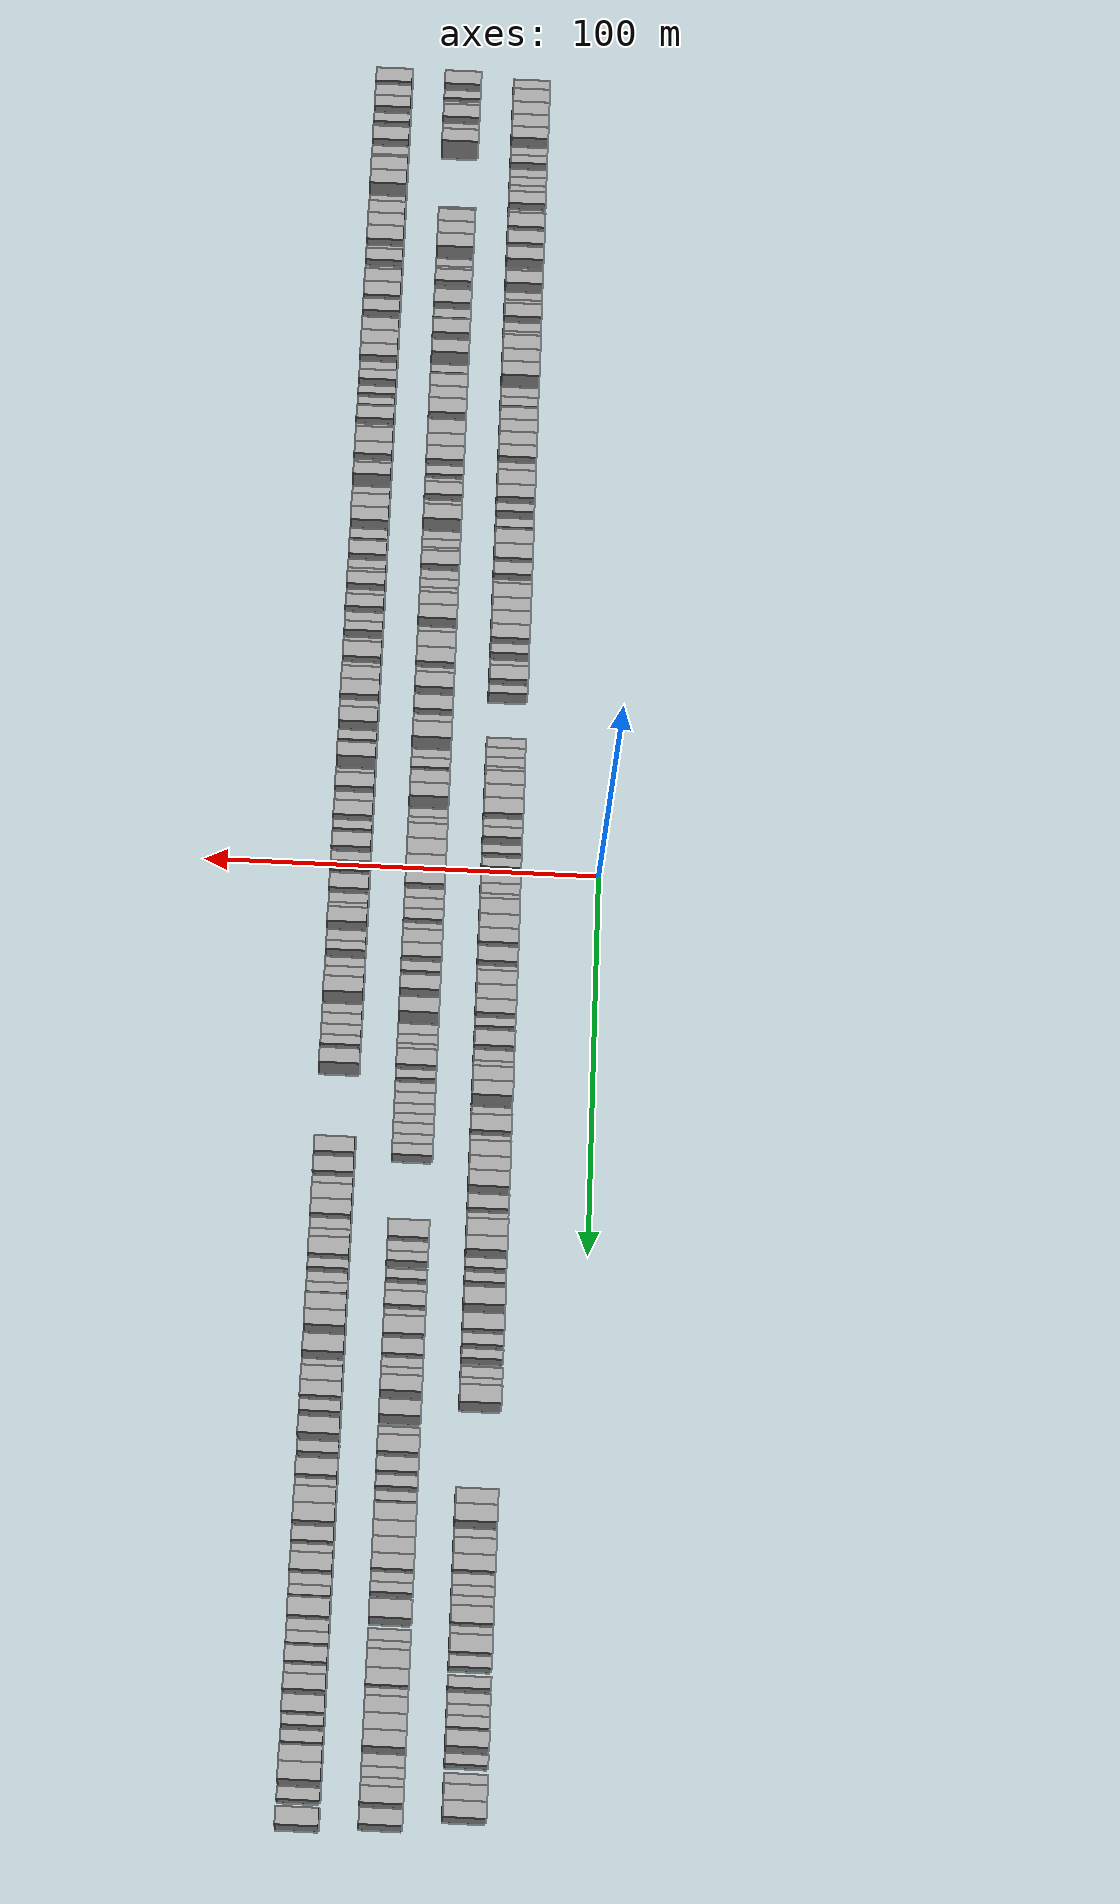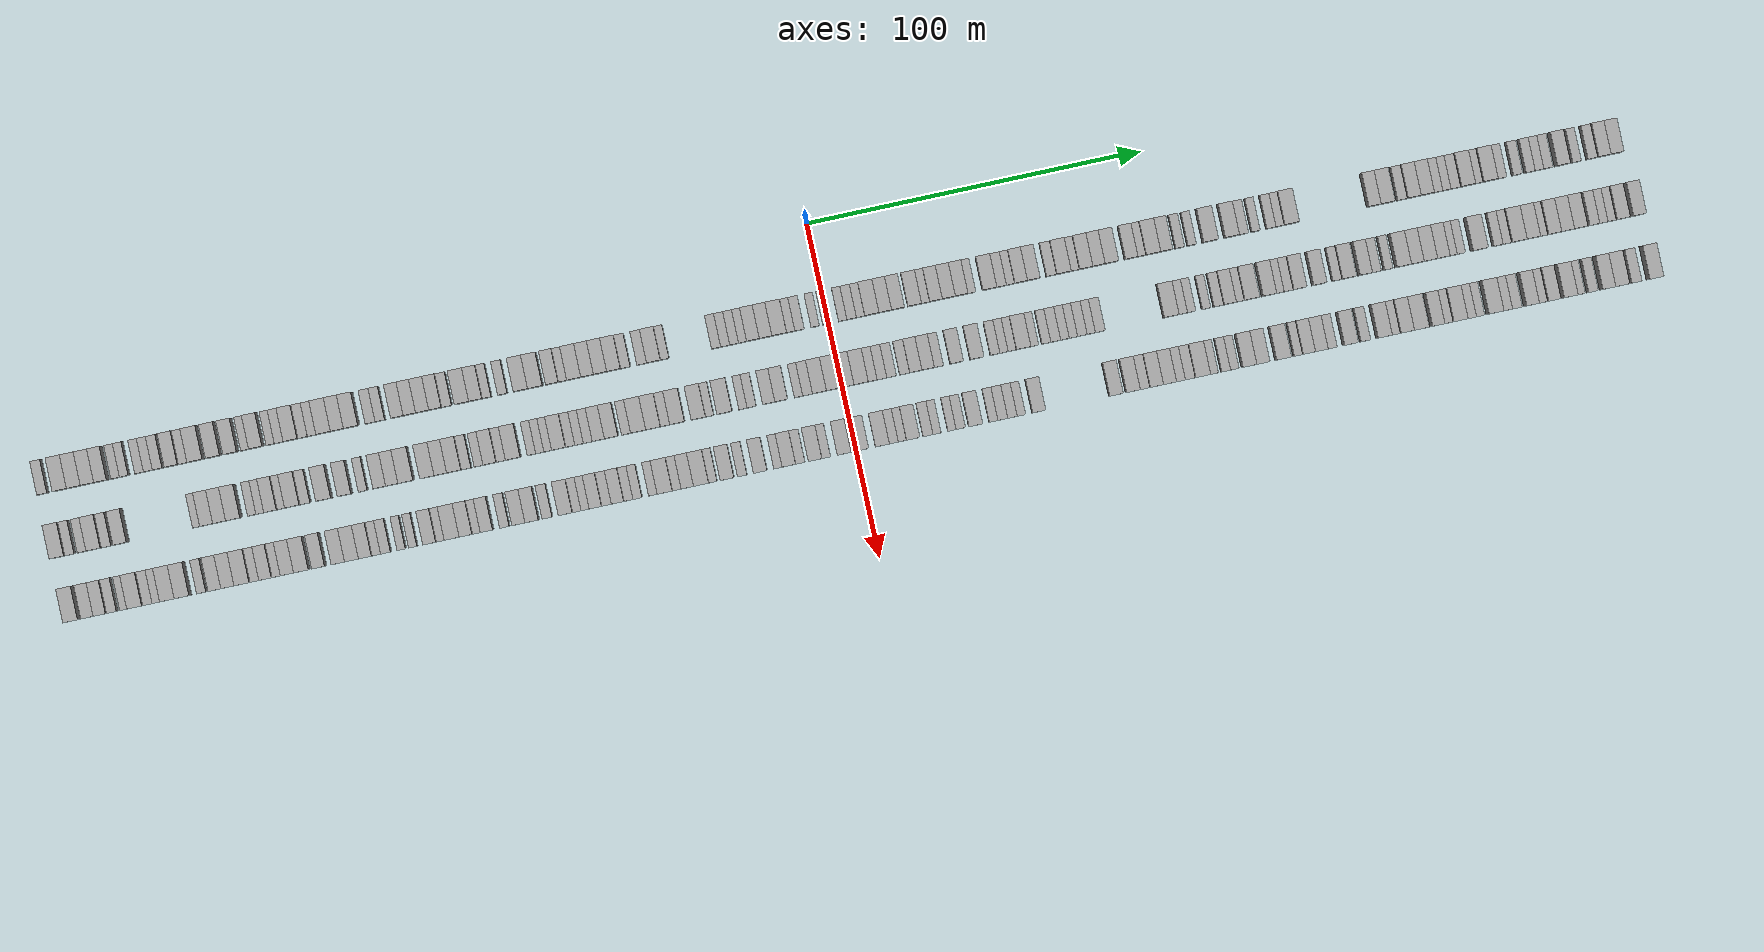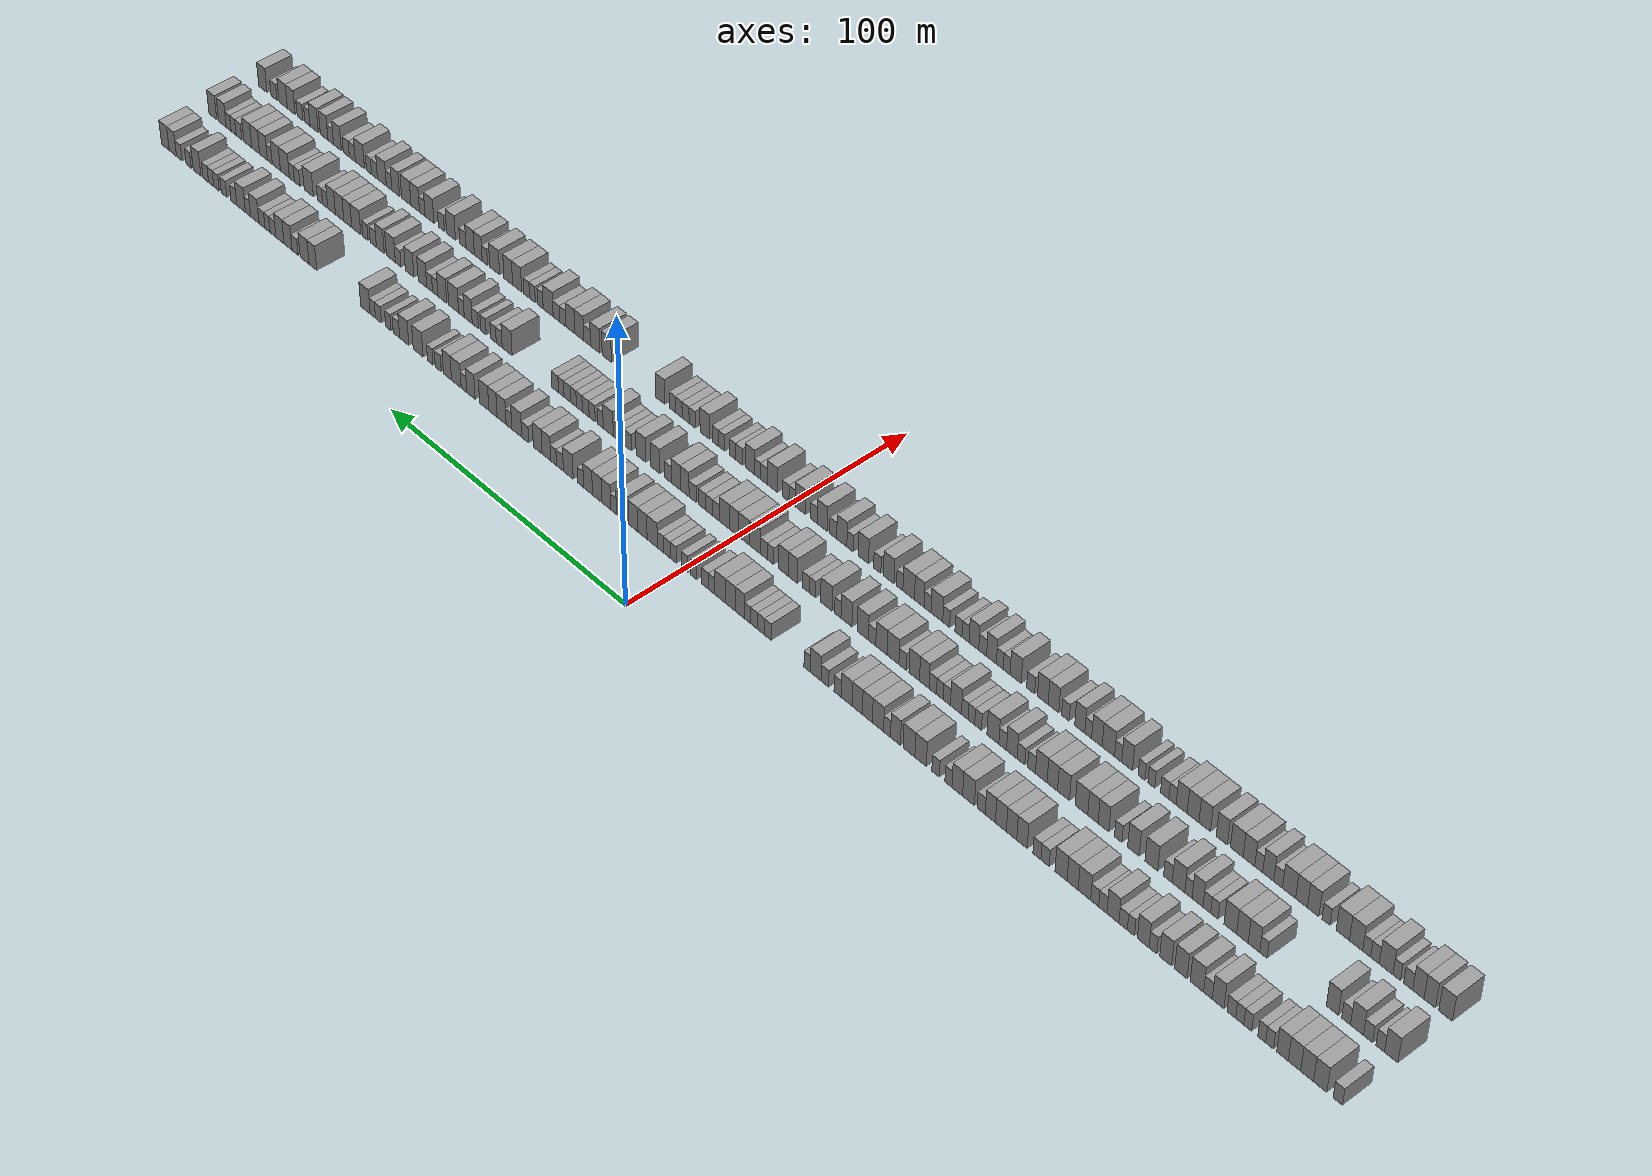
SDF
<sdf version="1.6">
 <world name="default">
  <scene>
   <sky><clouds><speed>12</speed></clouds></sky>
   <ambient>0.4 0.4 0.4 1</ambient>
   <background>0.7 0.7 0.7 1</background>
   <shadows>1</shadows>
  </scene>
  <gravity>0 0 -9.8066</gravity>
  <magnetic_field>6e-06 2.3e-05 -4.2e-05</magnetic_field>
  <physics default="0" name="default_physics" type="ode">
   <ode>
    <solver>
     <type>quick</type>
     <iters>10</iters>
     <sor>1.0</sor>
     <use_dynamic_moi_rescaling>0</use_dynamic_moi_rescaling>
    </solver>
    <constraints>
     <cfm>0</cfm>
     <erp>0.2</erp>
     <contact_max_correcting_vel>100</contact_max_correcting_vel>
     <contact_surface_layer>0.001</contact_surface_layer>
    </constraints>
   </ode>
   <max_step_size>0.004</max_step_size>
   <real_time_factor>1</real_time_factor>
   <real_time_update_rate>250</real_time_update_rate>
  </physics>
  <light name="sun" type="directional">
   <pose>0 0 10 0 0 0</pose>
   <diffuse>0.8 0.8 0.8 1</diffuse>
   <specular>0.2 0.2 0.2 1</specular>
   <attenuation>
    <range>1000</range>
    <constant>0.9</constant>
    <linear>0.01</linear>
    <quadratic>0.001</quadratic>
   </attenuation>
   <direction>-0.5 0.1 -0.9</direction>
  </light>
  <model name="building_1">
   <static>1</static>
   <pose>25.0000 -234.5110 0 0.000000 0.000000 0.000000</pose>
   <link name="link">
    <pose>0 0 3.00 0 0 0</pose>
    <collision name="collision"><geometry><box><size>10.0000 2.9780 6.0000</size></box></geometry></collision>
    <visual name="visual">
     <cast_shadows>0</cast_shadows>
     <geometry><box><size>10.0000 2.9780 6.0000</size></box></geometry>
     <material>
      <script>
       <uri>model://grey_wall/materials/scripts</uri>
       <uri>model://grey_wall/materials/textures</uri>
       <name>vrc/grey_wall</name>
      </script>
     </material>
    </visual>
   </link>
  </model>
  <model name="building_2">
   <static>1</static>
   <pose>25.0000 -228.8985 0 0.000000 0.000000 0.000000</pose>
   <link name="link">
    <pose>0 0 4.50 0 0 0</pose>
    <collision name="collision"><geometry><box><size>10.0000 4.2470 9.0000</size></box></geometry></collision>
    <visual name="visual">
     <cast_shadows>0</cast_shadows>
     <geometry><box><size>10.0000 4.2470 9.0000</size></box></geometry>
     <material>
      <script>
       <uri>model://grey_wall/materials/scripts</uri>
       <uri>model://grey_wall/materials/textures</uri>
       <name>vrc/grey_wall</name>
      </script>
     </material>
    </visual>
   </link>
  </model>
  <model name="building_3">
   <static>1</static>
   <pose>25.0000 -224.7222 0 0.000000 0.000000 0.000000</pose>
   <link name="link">
    <pose>0 0 4.50 0 0 0</pose>
    <collision name="collision"><geometry><box><size>10.0000 4.1056 9.0000</size></box></geometry></collision>
    <visual name="visual">
     <cast_shadows>0</cast_shadows>
     <geometry><box><size>10.0000 4.1056 9.0000</size></box></geometry>
     <material>
      <script>
       <uri>model://grey_wall/materials/scripts</uri>
       <uri>model://grey_wall/materials/textures</uri>
       <name>vrc/grey_wall</name>
      </script>
     </material>
    </visual>
   </link>
  </model>
  <model name="building_4">
   <static>1</static>
   <pose>25.0000 -220.6617 0 0.000000 0.000000 0.000000</pose>
   <link name="link">
    <pose>0 0 4.50 0 0 0</pose>
    <collision name="collision"><geometry><box><size>10.0000 4.0155 9.0000</size></box></geometry></collision>
    <visual name="visual">
     <cast_shadows>0</cast_shadows>
     <geometry><box><size>10.0000 4.0155 9.0000</size></box></geometry>
     <material>
      <script>
       <uri>model://grey_wall/materials/scripts</uri>
       <uri>model://grey_wall/materials/textures</uri>
       <name>vrc/grey_wall</name>
      </script>
     </material>
    </visual>
   </link>
  </model>
  <model name="building_5">
   <static>1</static>
   <pose>25.0000 -216.7929 0 0.000000 0.000000 0.000000</pose>
   <link name="link">
    <pose>0 0 4.50 0 0 0</pose>
    <collision name="collision"><geometry><box><size>10.0000 3.7220 9.0000</size></box></geometry></collision>
    <visual name="visual">
     <cast_shadows>0</cast_shadows>
     <geometry><box><size>10.0000 3.7220 9.0000</size></box></geometry>
     <material>
      <script>
       <uri>model://grey_wall/materials/scripts</uri>
       <uri>model://grey_wall/materials/textures</uri>
       <name>vrc/grey_wall</name>
      </script>
     </material>
    </visual>
   </link>
  </model>
  <model name="building_6">
   <static>1</static>
   <pose>25.0000 -212.6396 0 0.000000 0.000000 0.000000</pose>
   <link name="link">
    <pose>0 0 3.00 0 0 0</pose>
    <collision name="collision"><geometry><box><size>10.0000 2.5845 6.0000</size></box></geometry></collision>
    <visual name="visual">
     <cast_shadows>0</cast_shadows>
     <geometry><box><size>10.0000 2.5845 6.0000</size></box></geometry>
     <material>
      <script>
       <uri>model://grey_wall/materials/scripts</uri>
       <uri>model://grey_wall/materials/textures</uri>
       <name>vrc/grey_wall</name>
      </script>
     </material>
    </visual>
   </link>
  </model>
  <model name="building_7">
   <static>1</static>
   <pose>25.0000 -210.0761 0 0.000000 0.000000 0.000000</pose>
   <link name="link">
    <pose>0 0 3.00 0 0 0</pose>
    <collision name="collision"><geometry><box><size>10.0000 2.5425 6.0000</size></box></geometry></collision>
    <visual name="visual">
     <cast_shadows>0</cast_shadows>
     <geometry><box><size>10.0000 2.5425 6.0000</size></box></geometry>
     <material>
      <script>
       <uri>model://grey_wall/materials/scripts</uri>
       <uri>model://grey_wall/materials/textures</uri>
       <name>vrc/grey_wall</name>
      </script>
     </material>
    </visual>
   </link>
  </model>
  <model name="building_8">
   <static>1</static>
   <pose>25.0000 -205.5048 0 0.000000 0.000000 0.000000</pose>
   <link name="link">
    <pose>0 0 3.00 0 0 0</pose>
    <collision name="collision"><geometry><box><size>10.0000 2.6002 6.0000</size></box></geometry></collision>
    <visual name="visual">
     <cast_shadows>0</cast_shadows>
     <geometry><box><size>10.0000 2.6002 6.0000</size></box></geometry>
     <material>
      <script>
       <uri>model://grey_wall/materials/scripts</uri>
       <uri>model://grey_wall/materials/textures</uri>
       <name>vrc/grey_wall</name>
      </script>
     </material>
    </visual>
   </link>
  </model>
  <model name="building_9">
   <static>1</static>
   <pose>25.0000 -202.8734 0 0.000000 0.000000 0.000000</pose>
   <link name="link">
    <pose>0 0 3.00 0 0 0</pose>
    <collision name="collision"><geometry><box><size>10.0000 2.6625 6.0000</size></box></geometry></collision>
    <visual name="visual">
     <cast_shadows>0</cast_shadows>
     <geometry><box><size>10.0000 2.6625 6.0000</size></box></geometry>
     <material>
      <script>
       <uri>model://grey_wall/materials/scripts</uri>
       <uri>model://grey_wall/materials/textures</uri>
       <name>vrc/grey_wall</name>
      </script>
     </material>
    </visual>
   </link>
  </model>
  <model name="building_10">
   <static>1</static>
   <pose>25.0000 -200.1235 0 0.000000 0.000000 0.000000</pose>
   <link name="link">
    <pose>0 0 3.00 0 0 0</pose>
    <collision name="collision"><geometry><box><size>10.0000 2.8374 6.0000</size></box></geometry></collision>
    <visual name="visual">
     <cast_shadows>0</cast_shadows>
     <geometry><box><size>10.0000 2.8374 6.0000</size></box></geometry>
     <material>
      <script>
       <uri>model://grey_wall/materials/scripts</uri>
       <uri>model://grey_wall/materials/textures</uri>
       <name>vrc/grey_wall</name>
      </script>
     </material>
    </visual>
   </link>
  </model>
  <model name="building_11">
   <static>1</static>
   <pose>25.0000 -195.7681 0 0.000000 0.000000 0.000000</pose>
   <link name="link">
    <pose>0 0 4.50 0 0 0</pose>
    <collision name="collision"><geometry><box><size>10.0000 3.8734 9.0000</size></box></geometry></collision>
    <visual name="visual">
     <cast_shadows>0</cast_shadows>
     <geometry><box><size>10.0000 3.8734 9.0000</size></box></geometry>
     <material>
      <script>
       <uri>model://grey_wall/materials/scripts</uri>
       <uri>model://grey_wall/materials/textures</uri>
       <name>vrc/grey_wall</name>
      </script>
     </material>
    </visual>
   </link>
  </model>
  <model name="building_12">
   <static>1</static>
   <pose>25.0000 -192.3877 0 0.000000 0.000000 0.000000</pose>
   <link name="link">
    <pose>0 0 3.00 0 0 0</pose>
    <collision name="collision"><geometry><box><size>10.0000 2.8874 6.0000</size></box></geometry></collision>
    <visual name="visual">
     <cast_shadows>0</cast_shadows>
     <geometry><box><size>10.0000 2.8874 6.0000</size></box></geometry>
     <material>
      <script>
       <uri>model://grey_wall/materials/scripts</uri>
       <uri>model://grey_wall/materials/textures</uri>
       <name>vrc/grey_wall</name>
      </script>
     </material>
    </visual>
   </link>
  </model>
  <model name="building_13">
   <static>1</static>
   <pose>25.0000 -188.7021 0 0.000000 0.000000 0.000000</pose>
   <link name="link">
    <pose>0 0 4.50 0 0 0</pose>
    <collision name="collision"><geometry><box><size>10.0000 4.4838 9.0000</size></box></geometry></collision>
    <visual name="visual">
     <cast_shadows>0</cast_shadows>
     <geometry><box><size>10.0000 4.4838 9.0000</size></box></geometry>
     <material>
      <script>
       <uri>model://grey_wall/materials/scripts</uri>
       <uri>model://grey_wall/materials/textures</uri>
       <name>vrc/grey_wall</name>
      </script>
     </material>
    </visual>
   </link>
  </model>
  <model name="building_14">
   <static>1</static>
   <pose>25.0000 -183.3617 0 0.000000 0.000000 0.000000</pose>
   <link name="link">
    <pose>0 0 4.50 0 0 0</pose>
    <collision name="collision"><geometry><box><size>10.0000 4.1970 9.0000</size></box></geometry></collision>
    <visual name="visual">
     <cast_shadows>0</cast_shadows>
     <geometry><box><size>10.0000 4.1970 9.0000</size></box></geometry>
     <material>
      <script>
       <uri>model://grey_wall/materials/scripts</uri>
       <uri>model://grey_wall/materials/textures</uri>
       <name>vrc/grey_wall</name>
      </script>
     </material>
    </visual>
   </link>
  </model>
  <model name="building_15">
   <static>1</static>
   <pose>25.0000 -178.2500 0 0.000000 0.000000 0.000000</pose>
   <link name="link">
    <pose>0 0 4.50 0 0 0</pose>
    <collision name="collision"><geometry><box><size>10.0000 4.0265 9.0000</size></box></geometry></collision>
    <visual name="visual">
     <cast_shadows>0</cast_shadows>
     <geometry><box><size>10.0000 4.0265 9.0000</size></box></geometry>
     <material>
      <script>
       <uri>model://grey_wall/materials/scripts</uri>
       <uri>model://grey_wall/materials/textures</uri>
       <name>vrc/grey_wall</name>
      </script>
     </material>
    </visual>
   </link>
  </model>
  <model name="building_16">
   <static>1</static>
   <pose>25.0000 -173.9341 0 0.000000 0.000000 0.000000</pose>
   <link name="link">
    <pose>0 0 3.00 0 0 0</pose>
    <collision name="collision"><geometry><box><size>10.0000 2.6052 6.0000</size></box></geometry></collision>
    <visual name="visual">
     <cast_shadows>0</cast_shadows>
     <geometry><box><size>10.0000 2.6052 6.0000</size></box></geometry>
     <material>
      <script>
       <uri>model://grey_wall/materials/scripts</uri>
       <uri>model://grey_wall/materials/textures</uri>
       <name>vrc/grey_wall</name>
      </script>
     </material>
    </visual>
   </link>
  </model>
  <model name="building_17">
   <static>1</static>
   <pose>25.0000 -170.6508 0 0.000000 0.000000 0.000000</pose>
   <link name="link">
    <pose>0 0 4.50 0 0 0</pose>
    <collision name="collision"><geometry><box><size>10.0000 3.9614 9.0000</size></box></geometry></collision>
    <visual name="visual">
     <cast_shadows>0</cast_shadows>
     <geometry><box><size>10.0000 3.9614 9.0000</size></box></geometry>
     <material>
      <script>
       <uri>model://grey_wall/materials/scripts</uri>
       <uri>model://grey_wall/materials/textures</uri>
       <name>vrc/grey_wall</name>
      </script>
     </material>
    </visual>
   </link>
  </model>
  <model name="building_18">
   <static>1</static>
   <pose>25.0000 -166.4520 0 0.000000 0.000000 0.000000</pose>
   <link name="link">
    <pose>0 0 3.00 0 0 0</pose>
    <collision name="collision"><geometry><box><size>10.0000 2.4362 6.0000</size></box></geometry></collision>
    <visual name="visual">
     <cast_shadows>0</cast_shadows>
     <geometry><box><size>10.0000 2.4362 6.0000</size></box></geometry>
     <material>
      <script>
       <uri>model://grey_wall/materials/scripts</uri>
       <uri>model://grey_wall/materials/textures</uri>
       <name>vrc/grey_wall</name>
      </script>
     </material>
    </visual>
   </link>
  </model>
  <model name="building_19">
   <static>1</static>
   <pose>25.0000 -163.7899 0 0.000000 0.000000 0.000000</pose>
   <link name="link">
    <pose>0 0 3.00 0 0 0</pose>
    <collision name="collision"><geometry><box><size>10.0000 2.8879 6.0000</size></box></geometry></collision>
    <visual name="visual">
     <cast_shadows>0</cast_shadows>
     <geometry><box><size>10.0000 2.8879 6.0000</size></box></geometry>
     <material>
      <script>
       <uri>model://grey_wall/materials/scripts</uri>
       <uri>model://grey_wall/materials/textures</uri>
       <name>vrc/grey_wall</name>
      </script>
     </material>
    </visual>
   </link>
  </model>
  <model name="building_20">
   <static>1</static>
   <pose>25.0000 -160.2776 0 0.000000 0.000000 0.000000</pose>
   <link name="link">
    <pose>0 0 4.50 0 0 0</pose>
    <collision name="collision"><geometry><box><size>10.0000 4.1365 9.0000</size></box></geometry></collision>
    <visual name="visual">
     <cast_shadows>0</cast_shadows>
     <geometry><box><size>10.0000 4.1365 9.0000</size></box></geometry>
     <material>
      <script>
       <uri>model://grey_wall/materials/scripts</uri>
       <uri>model://grey_wall/materials/textures</uri>
       <name>vrc/grey_wall</name>
      </script>
     </material>
    </visual>
   </link>
  </model>
  <model name="building_21">
   <static>1</static>
   <pose>25.0000 -156.7975 0 0.000000 0.000000 0.000000</pose>
   <link name="link">
    <pose>0 0 3.00 0 0 0</pose>
    <collision name="collision"><geometry><box><size>10.0000 2.8238 6.0000</size></box></geometry></collision>
    <visual name="visual">
     <cast_shadows>0</cast_shadows>
     <geometry><box><size>10.0000 2.8238 6.0000</size></box></geometry>
     <material>
      <script>
       <uri>model://grey_wall/materials/scripts</uri>
       <uri>model://grey_wall/materials/textures</uri>
       <name>vrc/grey_wall</name>
      </script>
     </material>
    </visual>
   </link>
  </model>
  <model name="building_22">
   <static>1</static>
   <pose>25.0000 -153.9913 0 0.000000 0.000000 0.000000</pose>
   <link name="link">
    <pose>0 0 3.00 0 0 0</pose>
    <collision name="collision"><geometry><box><size>10.0000 2.7885 6.0000</size></box></geometry></collision>
    <visual name="visual">
     <cast_shadows>0</cast_shadows>
     <geometry><box><size>10.0000 2.7885 6.0000</size></box></geometry>
     <material>
      <script>
       <uri>model://grey_wall/materials/scripts</uri>
       <uri>model://grey_wall/materials/textures</uri>
       <name>vrc/grey_wall</name>
      </script>
     </material>
    </visual>
   </link>
  </model>
  <model name="building_23">
   <static>1</static>
   <pose>25.0000 -150.4368 0 0.000000 0.000000 0.000000</pose>
   <link name="link">
    <pose>0 0 4.50 0 0 0</pose>
    <collision name="collision"><geometry><box><size>10.0000 4.3205 9.0000</size></box></geometry></collision>
    <visual name="visual">
     <cast_shadows>0</cast_shadows>
     <geometry><box><size>10.0000 4.3205 9.0000</size></box></geometry>
     <material>
      <script>
       <uri>model://grey_wall/materials/scripts</uri>
       <uri>model://grey_wall/materials/textures</uri>
       <name>vrc/grey_wall</name>
      </script>
     </material>
    </visual>
   </link>
  </model>
  <model name="building_24">
   <static>1</static>
   <pose>25.0000 -146.3372 0 0.000000 0.000000 0.000000</pose>
   <link name="link">
    <pose>0 0 4.50 0 0 0</pose>
    <collision name="collision"><geometry><box><size>10.0000 3.8786 9.0000</size></box></geometry></collision>
    <visual name="visual">
     <cast_shadows>0</cast_shadows>
     <geometry><box><size>10.0000 3.8786 9.0000</size></box></geometry>
     <material>
      <script>
       <uri>model://grey_wall/materials/scripts</uri>
       <uri>model://grey_wall/materials/textures</uri>
       <name>vrc/grey_wall</name>
      </script>
     </material>
    </visual>
   </link>
  </model>
  <model name="building_25">
   <static>1</static>
   <pose>25.0000 -142.2803 0 0.000000 0.000000 0.000000</pose>
   <link name="link">
    <pose>0 0 4.50 0 0 0</pose>
    <collision name="collision"><geometry><box><size>10.0000 4.2353 9.0000</size></box></geometry></collision>
    <visual name="visual">
     <cast_shadows>0</cast_shadows>
     <geometry><box><size>10.0000 4.2353 9.0000</size></box></geometry>
     <material>
      <script>
       <uri>model://grey_wall/materials/scripts</uri>
       <uri>model://grey_wall/materials/textures</uri>
       <name>vrc/grey_wall</name>
      </script>
     </material>
    </visual>
   </link>
  </model>
  <model name="building_26">
   <static>1</static>
   <pose>25.0000 -136.6865 0 0.000000 0.000000 0.000000</pose>
   <link name="link">
    <pose>0 0 3.00 0 0 0</pose>
    <collision name="collision"><geometry><box><size>10.0000 2.9522 6.0000</size></box></geometry></collision>
    <visual name="visual">
     <cast_shadows>0</cast_shadows>
     <geometry><box><size>10.0000 2.9522 6.0000</size></box></geometry>
     <material>
      <script>
       <uri>model://grey_wall/materials/scripts</uri>
       <uri>model://grey_wall/materials/textures</uri>
       <name>vrc/grey_wall</name>
      </script>
     </material>
    </visual>
   </link>
  </model>
  <model name="building_27">
   <static>1</static>
   <pose>25.0000 -133.7986 0 0.000000 0.000000 0.000000</pose>
   <link name="link">
    <pose>0 0 3.00 0 0 0</pose>
    <collision name="collision"><geometry><box><size>10.0000 2.8236 6.0000</size></box></geometry></collision>
    <visual name="visual">
     <cast_shadows>0</cast_shadows>
     <geometry><box><size>10.0000 2.8236 6.0000</size></box></geometry>
     <material>
      <script>
       <uri>model://grey_wall/materials/scripts</uri>
       <uri>model://grey_wall/materials/textures</uri>
       <name>vrc/grey_wall</name>
      </script>
     </material>
    </visual>
   </link>
  </model>
  <model name="building_28">
   <static>1</static>
   <pose>25.0000 -128.5092 0 0.000000 0.000000 0.000000</pose>
   <link name="link">
    <pose>0 0 4.50 0 0 0</pose>
    <collision name="collision"><geometry><box><size>10.0000 3.7552 9.0000</size></box></geometry></collision>
    <visual name="visual">
     <cast_shadows>0</cast_shadows>
     <geometry><box><size>10.0000 3.7552 9.0000</size></box></geometry>
     <material>
      <script>
       <uri>model://grey_wall/materials/scripts</uri>
       <uri>model://grey_wall/materials/textures</uri>
       <name>vrc/grey_wall</name>
      </script>
     </material>
    </visual>
   </link>
  </model>
  <model name="building_29">
   <static>1</static>
   <pose>25.0000 -124.7815 0 0.000000 0.000000 0.000000</pose>
   <link name="link">
    <pose>0 0 4.50 0 0 0</pose>
    <collision name="collision"><geometry><box><size>10.0000 3.7002 9.0000</size></box></geometry></collision>
    <visual name="visual">
     <cast_shadows>0</cast_shadows>
     <geometry><box><size>10.0000 3.7002 9.0000</size></box></geometry>
     <material>
      <script>
       <uri>model://grey_wall/materials/scripts</uri>
       <uri>model://grey_wall/materials/textures</uri>
       <name>vrc/grey_wall</name>
      </script>
     </material>
    </visual>
   </link>
  </model>
  <model name="building_30">
   <static>1</static>
   <pose>25.0000 -120.9735 0 0.000000 0.000000 0.000000</pose>
   <link name="link">
    <pose>0 0 4.50 0 0 0</pose>
    <collision name="collision"><geometry><box><size>10.0000 3.9158 9.0000</size></box></geometry></collision>
    <visual name="visual">
     <cast_shadows>0</cast_shadows>
     <geometry><box><size>10.0000 3.9158 9.0000</size></box></geometry>
     <material>
      <script>
       <uri>model://grey_wall/materials/scripts</uri>
       <uri>model://grey_wall/materials/textures</uri>
       <name>vrc/grey_wall</name>
      </script>
     </material>
    </visual>
   </link>
  </model>
  <model name="building_31">
   <static>1</static>
   <pose>25.0000 -117.1843 0 0.000000 0.000000 0.000000</pose>
   <link name="link">
    <pose>0 0 4.50 0 0 0</pose>
    <collision name="collision"><geometry><box><size>10.0000 3.6627 9.0000</size></box></geometry></collision>
    <visual name="visual">
     <cast_shadows>0</cast_shadows>
     <geometry><box><size>10.0000 3.6627 9.0000</size></box></geometry>
     <material>
      <script>
       <uri>model://grey_wall/materials/scripts</uri>
       <uri>model://grey_wall/materials/textures</uri>
       <name>vrc/grey_wall</name>
      </script>
     </material>
    </visual>
   </link>
  </model>
  <model name="building_32">
   <static>1</static>
   <pose>25.0000 -113.9052 0 0.000000 0.000000 0.000000</pose>
   <link name="link">
    <pose>0 0 3.00 0 0 0</pose>
    <collision name="collision"><geometry><box><size>10.0000 2.8955 6.0000</size></box></geometry></collision>
    <visual name="visual">
     <cast_shadows>0</cast_shadows>
     <geometry><box><size>10.0000 2.8955 6.0000</size></box></geometry>
     <material>
      <script>
       <uri>model://grey_wall/materials/scripts</uri>
       <uri>model://grey_wall/materials/textures</uri>
       <name>vrc/grey_wall</name>
      </script>
     </material>
    </visual>
   </link>
  </model>
  <model name="building_33">
   <static>1</static>
   <pose>25.0000 -109.3072 0 0.000000 0.000000 0.000000</pose>
   <link name="link">
    <pose>0 0 4.50 0 0 0</pose>
    <collision name="collision"><geometry><box><size>10.0000 4.3006 9.0000</size></box></geometry></collision>
    <visual name="visual">
     <cast_shadows>0</cast_shadows>
     <geometry><box><size>10.0000 4.3006 9.0000</size></box></geometry>
     <material>
      <script>
       <uri>model://grey_wall/materials/scripts</uri>
       <uri>model://grey_wall/materials/textures</uri>
       <name>vrc/grey_wall</name>
      </script>
     </material>
    </visual>
   </link>
  </model>
  <model name="building_34">
   <static>1</static>
   <pose>25.0000 -105.2153 0 0.000000 0.000000 0.000000</pose>
   <link name="link">
    <pose>0 0 4.50 0 0 0</pose>
    <collision name="collision"><geometry><box><size>10.0000 3.8832 9.0000</size></box></geometry></collision>
    <visual name="visual">
     <cast_shadows>0</cast_shadows>
     <geometry><box><size>10.0000 3.8832 9.0000</size></box></geometry>
     <material>
      <script>
       <uri>model://grey_wall/materials/scripts</uri>
       <uri>model://grey_wall/materials/textures</uri>
       <name>vrc/grey_wall</name>
      </script>
     </material>
    </visual>
   </link>
  </model>
  <model name="building_35">
   <static>1</static>
   <pose>25.0000 -101.9781 0 0.000000 0.000000 0.000000</pose>
   <link name="link">
    <pose>0 0 3.00 0 0 0</pose>
    <collision name="collision"><geometry><box><size>10.0000 2.5912 6.0000</size></box></geometry></collision>
    <visual name="visual">
     <cast_shadows>0</cast_shadows>
     <geometry><box><size>10.0000 2.5912 6.0000</size></box></geometry>
     <material>
      <script>
       <uri>model://grey_wall/materials/scripts</uri>
       <uri>model://grey_wall/materials/textures</uri>
       <name>vrc/grey_wall</name>
      </script>
     </material>
    </visual>
   </link>
  </model>
  <model name="building_36">
   <static>1</static>
   <pose>25.0000 -97.2836 0 0.000000 0.000000 0.000000</pose>
   <link name="link">
    <pose>0 0 3.00 0 0 0</pose>
    <collision name="collision"><geometry><box><size>10.0000 2.7979 6.0000</size></box></geometry></collision>
    <visual name="visual">
     <cast_shadows>0</cast_shadows>
     <geometry><box><size>10.0000 2.7979 6.0000</size></box></geometry>
     <material>
      <script>
       <uri>model://grey_wall/materials/scripts</uri>
       <uri>model://grey_wall/materials/textures</uri>
       <name>vrc/grey_wall</name>
      </script>
     </material>
    </visual>
   </link>
  </model>
  <model name="building_37">
   <static>1</static>
   <pose>25.0000 -91.7551 0 0.000000 0.000000 0.000000</pose>
   <link name="link">
    <pose>0 0 4.50 0 0 0</pose>
    <collision name="collision"><geometry><box><size>10.0000 4.2590 9.0000</size></box></geometry></collision>
    <visual name="visual">
     <cast_shadows>0</cast_shadows>
     <geometry><box><size>10.0000 4.2590 9.0000</size></box></geometry>
     <material>
      <script>
       <uri>model://grey_wall/materials/scripts</uri>
       <uri>model://grey_wall/materials/textures</uri>
       <name>vrc/grey_wall</name>
      </script>
     </material>
    </visual>
   </link>
  </model>
  <model name="building_38">
   <static>1</static>
   <pose>25.0000 -87.4545 0 0.000000 0.000000 0.000000</pose>
   <link name="link">
    <pose>0 0 4.50 0 0 0</pose>
    <collision name="collision"><geometry><box><size>10.0000 4.3421 9.0000</size></box></geometry></collision>
    <visual name="visual">
     <cast_shadows>0</cast_shadows>
     <geometry><box><size>10.0000 4.3421 9.0000</size></box></geometry>
     <material>
      <script>
       <uri>model://grey_wall/materials/scripts</uri>
       <uri>model://grey_wall/materials/textures</uri>
       <name>vrc/grey_wall</name>
      </script>
     </material>
    </visual>
   </link>
  </model>
  <model name="building_39">
   <static>1</static>
   <pose>25.0000 -82.4269 0 0.000000 0.000000 0.000000</pose>
   <link name="link">
    <pose>0 0 4.50 0 0 0</pose>
    <collision name="collision"><geometry><box><size>10.0000 3.7131 9.0000</size></box></geometry></collision>
    <visual name="visual">
     <cast_shadows>0</cast_shadows>
     <geometry><box><size>10.0000 3.7131 9.0000</size></box></geometry>
     <material>
      <script>
       <uri>model://grey_wall/materials/scripts</uri>
       <uri>model://grey_wall/materials/textures</uri>
       <name>vrc/grey_wall</name>
      </script>
     </material>
    </visual>
   </link>
  </model>
  <model name="building_40">
   <static>1</static>
   <pose>25.0000 -79.2760 0 0.000000 0.000000 0.000000</pose>
   <link name="link">
    <pose>0 0 3.00 0 0 0</pose>
    <collision name="collision"><geometry><box><size>10.0000 2.5886 6.0000</size></box></geometry></collision>
    <visual name="visual">
     <cast_shadows>0</cast_shadows>
     <geometry><box><size>10.0000 2.5886 6.0000</size></box></geometry>
     <material>
      <script>
       <uri>model://grey_wall/materials/scripts</uri>
       <uri>model://grey_wall/materials/textures</uri>
       <name>vrc/grey_wall</name>
      </script>
     </material>
    </visual>
   </link>
  </model>
  <model name="building_41">
   <static>1</static>
   <pose>25.0000 -75.8883 0 0.000000 0.000000 0.000000</pose>
   <link name="link">
    <pose>0 0 4.50 0 0 0</pose>
    <collision name="collision"><geometry><box><size>10.0000 4.1868 9.0000</size></box></geometry></collision>
    <visual name="visual">
     <cast_shadows>0</cast_shadows>
     <geometry><box><size>10.0000 4.1868 9.0000</size></box></geometry>
     <material>
      <script>
       <uri>model://grey_wall/materials/scripts</uri>
       <uri>model://grey_wall/materials/textures</uri>
       <name>vrc/grey_wall</name>
      </script>
     </material>
    </visual>
   </link>
  </model>
  <model name="building_42">
   <static>1</static>
   <pose>25.0000 -71.9064 0 0.000000 0.000000 0.000000</pose>
   <link name="link">
    <pose>0 0 4.50 0 0 0</pose>
    <collision name="collision"><geometry><box><size>10.0000 3.7771 9.0000</size></box></geometry></collision>
    <visual name="visual">
     <cast_shadows>0</cast_shadows>
     <geometry><box><size>10.0000 3.7771 9.0000</size></box></geometry>
     <material>
      <script>
       <uri>model://grey_wall/materials/scripts</uri>
       <uri>model://grey_wall/materials/textures</uri>
       <name>vrc/grey_wall</name>
      </script>
     </material>
    </visual>
   </link>
  </model>
  <model name="building_43">
   <static>1</static>
   <pose>25.0000 -68.0568 0 0.000000 0.000000 0.000000</pose>
   <link name="link">
    <pose>0 0 4.50 0 0 0</pose>
    <collision name="collision"><geometry><box><size>10.0000 3.9220 9.0000</size></box></geometry></collision>
    <visual name="visual">
     <cast_shadows>0</cast_shadows>
     <geometry><box><size>10.0000 3.9220 9.0000</size></box></geometry>
     <material>
      <script>
       <uri>model://grey_wall/materials/scripts</uri>
       <uri>model://grey_wall/materials/textures</uri>
       <name>vrc/grey_wall</name>
      </script>
     </material>
    </visual>
   </link>
  </model>
  <model name="building_44">
   <static>1</static>
   <pose>25.0000 -64.0675 0 0.000000 0.000000 0.000000</pose>
   <link name="link">
    <pose>0 0 4.50 0 0 0</pose>
    <collision name="collision"><geometry><box><size>10.0000 4.0567 9.0000</size></box></geometry></collision>
    <visual name="visual">
     <cast_shadows>0</cast_shadows>
     <geometry><box><size>10.0000 4.0567 9.0000</size></box></geometry>
     <material>
      <script>
       <uri>model://grey_wall/materials/scripts</uri>
       <uri>model://grey_wall/materials/textures</uri>
       <name>vrc/grey_wall</name>
      </script>
     </material>
    </visual>
   </link>
  </model>
  <model name="building_45">
   <static>1</static>
   <pose>25.0000 -60.6158 0 0.000000 0.000000 0.000000</pose>
   <link name="link">
    <pose>0 0 3.00 0 0 0</pose>
    <collision name="collision"><geometry><box><size>10.0000 2.8466 6.0000</size></box></geometry></collision>
    <visual name="visual">
     <cast_shadows>0</cast_shadows>
     <geometry><box><size>10.0000 2.8466 6.0000</size></box></geometry>
     <material>
      <script>
       <uri>model://grey_wall/materials/scripts</uri>
       <uri>model://grey_wall/materials/textures</uri>
       <name>vrc/grey_wall</name>
      </script>
     </material>
    </visual>
   </link>
  </model>
  <model name="building_46">
   <static>1</static>
   <pose>25.0000 -55.7144 0 0.000000 0.000000 0.000000</pose>
   <link name="link">
    <pose>0 0 3.00 0 0 0</pose>
    <collision name="collision"><geometry><box><size>10.0000 2.9563 6.0000</size></box></geometry></collision>
    <visual name="visual">
     <cast_shadows>0</cast_shadows>
     <geometry><box><size>10.0000 2.9563 6.0000</size></box></geometry>
     <material>
      <script>
       <uri>model://grey_wall/materials/scripts</uri>
       <uri>model://grey_wall/materials/textures</uri>
       <name>vrc/grey_wall</name>
      </script>
     </material>
    </visual>
   </link>
  </model>
  <model name="building_47">
   <static>1</static>
   <pose>25.0000 -52.1917 0 0.000000 0.000000 0.000000</pose>
   <link name="link">
    <pose>0 0 4.50 0 0 0</pose>
    <collision name="collision"><geometry><box><size>10.0000 4.0892 9.0000</size></box></geometry></collision>
    <visual name="visual">
     <cast_shadows>0</cast_shadows>
     <geometry><box><size>10.0000 4.0892 9.0000</size></box></geometry>
     <material>
      <script>
       <uri>model://grey_wall/materials/scripts</uri>
       <uri>model://grey_wall/materials/textures</uri>
       <name>vrc/grey_wall</name>
      </script>
     </material>
    </visual>
   </link>
  </model>
  <model name="building_48">
   <static>1</static>
   <pose>25.0000 -48.8967 0 0.000000 0.000000 0.000000</pose>
   <link name="link">
    <pose>0 0 3.00 0 0 0</pose>
    <collision name="collision"><geometry><box><size>10.0000 2.5009 6.0000</size></box></geometry></collision>
    <visual name="visual">
     <cast_shadows>0</cast_shadows>
     <geometry><box><size>10.0000 2.5009 6.0000</size></box></geometry>
     <material>
      <script>
       <uri>model://grey_wall/materials/scripts</uri>
       <uri>model://grey_wall/materials/textures</uri>
       <name>vrc/grey_wall</name>
      </script>
     </material>
    </visual>
   </link>
  </model>
  <model name="building_49">
   <static>1</static>
   <pose>25.0000 -33.5730 0 0.000000 0.000000 0.000000</pose>
   <link name="link">
    <pose>0 0 3.00 0 0 0</pose>
    <collision name="collision"><geometry><box><size>10.0000 2.7155 6.0000</size></box></geometry></collision>
    <visual name="visual">
     <cast_shadows>0</cast_shadows>
     <geometry><box><size>10.0000 2.7155 6.0000</size></box></geometry>
     <material>
      <script>
       <uri>model://grey_wall/materials/scripts</uri>
       <uri>model://grey_wall/materials/textures</uri>
       <name>vrc/grey_wall</name>
      </script>
     </material>
    </visual>
   </link>
  </model>
  <model name="building_50">
   <static>1</static>
   <pose>25.0000 -30.8629 0 0.000000 0.000000 0.000000</pose>
   <link name="link">
    <pose>0 0 3.00 0 0 0</pose>
    <collision name="collision"><geometry><box><size>10.0000 2.7047 6.0000</size></box></geometry></collision>
    <visual name="visual">
     <cast_shadows>0</cast_shadows>
     <geometry><box><size>10.0000 2.7047 6.0000</size></box></geometry>
     <material>
      <script>
       <uri>model://grey_wall/materials/scripts</uri>
       <uri>model://grey_wall/materials/textures</uri>
       <name>vrc/grey_wall</name>
      </script>
     </material>
    </visual>
   </link>
  </model>
  <model name="building_51">
   <static>1</static>
   <pose>25.0000 -28.1963 0 0.000000 0.000000 0.000000</pose>
   <link name="link">
    <pose>0 0 3.00 0 0 0</pose>
    <collision name="collision"><geometry><box><size>10.0000 2.6285 6.0000</size></box></geometry></collision>
    <visual name="visual">
     <cast_shadows>0</cast_shadows>
     <geometry><box><size>10.0000 2.6285 6.0000</size></box></geometry>
     <material>
      <script>
       <uri>model://grey_wall/materials/scripts</uri>
       <uri>model://grey_wall/materials/textures</uri>
       <name>vrc/grey_wall</name>
      </script>
     </material>
    </visual>
   </link>
  </model>
  <model name="building_52">
   <static>1</static>
   <pose>25.0000 -25.6658 0 0.000000 0.000000 0.000000</pose>
   <link name="link">
    <pose>0 0 3.00 0 0 0</pose>
    <collision name="collision"><geometry><box><size>10.0000 2.4326 6.0000</size></box></geometry></collision>
    <visual name="visual">
     <cast_shadows>0</cast_shadows>
     <geometry><box><size>10.0000 2.4326 6.0000</size></box></geometry>
     <material>
      <script>
       <uri>model://grey_wall/materials/scripts</uri>
       <uri>model://grey_wall/materials/textures</uri>
       <name>vrc/grey_wall</name>
      </script>
     </material>
    </visual>
   </link>
  </model>
  <model name="building_53">
   <static>1</static>
   <pose>25.0000 -22.5579 0 0.000000 0.000000 0.000000</pose>
   <link name="link">
    <pose>0 0 4.50 0 0 0</pose>
    <collision name="collision"><geometry><box><size>10.0000 3.7831 9.0000</size></box></geometry></collision>
    <visual name="visual">
     <cast_shadows>0</cast_shadows>
     <geometry><box><size>10.0000 3.7831 9.0000</size></box></geometry>
     <material>
      <script>
       <uri>model://grey_wall/materials/scripts</uri>
       <uri>model://grey_wall/materials/textures</uri>
       <name>vrc/grey_wall</name>
      </script>
     </material>
    </visual>
   </link>
  </model>
  <model name="building_54">
   <static>1</static>
   <pose>25.0000 -18.7924 0 0.000000 0.000000 0.000000</pose>
   <link name="link">
    <pose>0 0 4.50 0 0 0</pose>
    <collision name="collision"><geometry><box><size>10.0000 3.7478 9.0000</size></box></geometry></collision>
    <visual name="visual">
     <cast_shadows>0</cast_shadows>
     <geometry><box><size>10.0000 3.7478 9.0000</size></box></geometry>
     <material>
      <script>
       <uri>model://grey_wall/materials/scripts</uri>
       <uri>model://grey_wall/materials/textures</uri>
       <name>vrc/grey_wall</name>
      </script>
     </material>
    </visual>
   </link>
  </model>
  <model name="building_55">
   <static>1</static>
   <pose>25.0000 -14.7330 0 0.000000 0.000000 0.000000</pose>
   <link name="link">
    <pose>0 0 4.50 0 0 0</pose>
    <collision name="collision"><geometry><box><size>10.0000 4.3712 9.0000</size></box></geometry></collision>
    <visual name="visual">
     <cast_shadows>0</cast_shadows>
     <geometry><box><size>10.0000 4.3712 9.0000</size></box></geometry>
     <material>
      <script>
       <uri>model://grey_wall/materials/scripts</uri>
       <uri>model://grey_wall/materials/textures</uri>
       <name>vrc/grey_wall</name>
      </script>
     </material>
    </visual>
   </link>
  </model>
  <model name="building_56">
   <static>1</static>
   <pose>25.0000 -11.3244 0 0.000000 0.000000 0.000000</pose>
   <link name="link">
    <pose>0 0 3.00 0 0 0</pose>
    <collision name="collision"><geometry><box><size>10.0000 2.4460 6.0000</size></box></geometry></collision>
    <visual name="visual">
     <cast_shadows>0</cast_shadows>
     <geometry><box><size>10.0000 2.4460 6.0000</size></box></geometry>
     <material>
      <script>
       <uri>model://grey_wall/materials/scripts</uri>
       <uri>model://grey_wall/materials/textures</uri>
       <name>vrc/grey_wall</name>
      </script>
     </material>
    </visual>
   </link>
  </model>
  <model name="building_57">
   <static>1</static>
   <pose>25.0000 -8.6914 0 0.000000 0.000000 0.000000</pose>
   <link name="link">
    <pose>0 0 3.00 0 0 0</pose>
    <collision name="collision"><geometry><box><size>10.0000 2.8198 6.0000</size></box></geometry></collision>
    <visual name="visual">
     <cast_shadows>0</cast_shadows>
     <geometry><box><size>10.0000 2.8198 6.0000</size></box></geometry>
     <material>
      <script>
       <uri>model://grey_wall/materials/scripts</uri>
       <uri>model://grey_wall/materials/textures</uri>
       <name>vrc/grey_wall</name>
      </script>
     </material>
    </visual>
   </link>
  </model>
  <model name="building_58">
   <static>1</static>
   <pose>25.0000 -4.0355 0 0.000000 0.000000 0.000000</pose>
   <link name="link">
    <pose>0 0 3.00 0 0 0</pose>
    <collision name="collision"><geometry><box><size>10.0000 2.4920 6.0000</size></box></geometry></collision>
    <visual name="visual">
     <cast_shadows>0</cast_shadows>
     <geometry><box><size>10.0000 2.4920 6.0000</size></box></geometry>
     <material>
      <script>
       <uri>model://grey_wall/materials/scripts</uri>
       <uri>model://grey_wall/materials/textures</uri>
       <name>vrc/grey_wall</name>
      </script>
     </material>
    </visual>
   </link>
  </model>
  <model name="building_59">
   <static>1</static>
   <pose>25.0000 -0.4281 0 0.000000 0.000000 0.000000</pose>
   <link name="link">
    <pose>0 0 3.00 0 0 0</pose>
    <collision name="collision"><geometry><box><size>10.0000 2.7228 6.0000</size></box></geometry></collision>
    <visual name="visual">
     <cast_shadows>0</cast_shadows>
     <geometry><box><size>10.0000 2.7228 6.0000</size></box></geometry>
     <material>
      <script>
       <uri>model://grey_wall/materials/scripts</uri>
       <uri>model://grey_wall/materials/textures</uri>
       <name>vrc/grey_wall</name>
      </script>
     </material>
    </visual>
   </link>
  </model>
  <model name="building_60">
   <static>1</static>
   <pose>25.0000 4.1761 0 0.000000 0.000000 0.000000</pose>
   <link name="link">
    <pose>0 0 3.00 0 0 0</pose>
    <collision name="collision"><geometry><box><size>10.0000 2.4855 6.0000</size></box></geometry></collision>
    <visual name="visual">
     <cast_shadows>0</cast_shadows>
     <geometry><box><size>10.0000 2.4855 6.0000</size></box></geometry>
     <material>
      <script>
       <uri>model://grey_wall/materials/scripts</uri>
       <uri>model://grey_wall/materials/textures</uri>
       <name>vrc/grey_wall</name>
      </script>
     </material>
    </visual>
   </link>
  </model>
  <model name="building_61">
   <static>1</static>
   <pose>25.0000 6.8330 0 0.000000 0.000000 0.000000</pose>
   <link name="link">
    <pose>0 0 3.00 0 0 0</pose>
    <collision name="collision"><geometry><box><size>10.0000 2.8284 6.0000</size></box></geometry></collision>
    <visual name="visual">
     <cast_shadows>0</cast_shadows>
     <geometry><box><size>10.0000 2.8284 6.0000</size></box></geometry>
     <material>
      <script>
       <uri>model://grey_wall/materials/scripts</uri>
       <uri>model://grey_wall/materials/textures</uri>
       <name>vrc/grey_wall</name>
      </script>
     </material>
    </visual>
   </link>
  </model>
  <model name="building_62">
   <static>1</static>
   <pose>25.0000 9.4824 0 0.000000 0.000000 0.000000</pose>
   <link name="link">
    <pose>0 0 3.00 0 0 0</pose>
    <collision name="collision"><geometry><box><size>10.0000 2.4702 6.0000</size></box></geometry></collision>
    <visual name="visual">
     <cast_shadows>0</cast_shadows>
     <geometry><box><size>10.0000 2.4702 6.0000</size></box></geometry>
     <material>
      <script>
       <uri>model://grey_wall/materials/scripts</uri>
       <uri>model://grey_wall/materials/textures</uri>
       <name>vrc/grey_wall</name>
      </script>
     </material>
    </visual>
   </link>
  </model>
  <model name="building_63">
   <static>1</static>
   <pose>25.0000 12.8363 0 0.000000 0.000000 0.000000</pose>
   <link name="link">
    <pose>0 0 4.50 0 0 0</pose>
    <collision name="collision"><geometry><box><size>10.0000 4.2377 9.0000</size></box></geometry></collision>
    <visual name="visual">
     <cast_shadows>0</cast_shadows>
     <geometry><box><size>10.0000 4.2377 9.0000</size></box></geometry>
     <material>
      <script>
       <uri>model://grey_wall/materials/scripts</uri>
       <uri>model://grey_wall/materials/textures</uri>
       <name>vrc/grey_wall</name>
      </script>
     </material>
    </visual>
   </link>
  </model>
  <model name="building_64">
   <static>1</static>
   <pose>25.0000 16.8305 0 0.000000 0.000000 0.000000</pose>
   <link name="link">
    <pose>0 0 4.50 0 0 0</pose>
    <collision name="collision"><geometry><box><size>10.0000 3.7506 9.0000</size></box></geometry></collision>
    <visual name="visual">
     <cast_shadows>0</cast_shadows>
     <geometry><box><size>10.0000 3.7506 9.0000</size></box></geometry>
     <material>
      <script>
       <uri>model://grey_wall/materials/scripts</uri>
       <uri>model://grey_wall/materials/textures</uri>
       <name>vrc/grey_wall</name>
      </script>
     </material>
    </visual>
   </link>
  </model>
  <model name="building_65">
   <static>1</static>
   <pose>25.0000 20.6405 0 0.000000 0.000000 0.000000</pose>
   <link name="link">
    <pose>0 0 4.50 0 0 0</pose>
    <collision name="collision"><geometry><box><size>10.0000 3.8695 9.0000</size></box></geometry></collision>
    <visual name="visual">
     <cast_shadows>0</cast_shadows>
     <geometry><box><size>10.0000 3.8695 9.0000</size></box></geometry>
     <material>
      <script>
       <uri>model://grey_wall/materials/scripts</uri>
       <uri>model://grey_wall/materials/textures</uri>
       <name>vrc/grey_wall</name>
      </script>
     </material>
    </visual>
   </link>
  </model>
  <model name="building_66">
   <static>1</static>
   <pose>25.0000 25.6066 0 0.000000 0.000000 0.000000</pose>
   <link name="link">
    <pose>0 0 4.50 0 0 0</pose>
    <collision name="collision"><geometry><box><size>10.0000 4.0626 9.0000</size></box></geometry></collision>
    <visual name="visual">
     <cast_shadows>0</cast_shadows>
     <geometry><box><size>10.0000 4.0626 9.0000</size></box></geometry>
     <material>
      <script>
       <uri>model://grey_wall/materials/scripts</uri>
       <uri>model://grey_wall/materials/textures</uri>
       <name>vrc/grey_wall</name>
      </script>
     </material>
    </visual>
   </link>
  </model>
  <model name="building_67">
   <static>1</static>
   <pose>25.0000 28.8543 0 0.000000 0.000000 0.000000</pose>
   <link name="link">
    <pose>0 0 3.00 0 0 0</pose>
    <collision name="collision"><geometry><box><size>10.0000 2.4327 6.0000</size></box></geometry></collision>
    <visual name="visual">
     <cast_shadows>0</cast_shadows>
     <geometry><box><size>10.0000 2.4327 6.0000</size></box></geometry>
     <material>
      <script>
       <uri>model://grey_wall/materials/scripts</uri>
       <uri>model://grey_wall/materials/textures</uri>
       <name>vrc/grey_wall</name>
      </script>
     </material>
    </visual>
   </link>
  </model>
  <model name="building_68">
   <static>1</static>
   <pose>25.0000 31.9422 0 0.000000 0.000000 0.000000</pose>
   <link name="link">
    <pose>0 0 4.50 0 0 0</pose>
    <collision name="collision"><geometry><box><size>10.0000 3.7432 9.0000</size></box></geometry></collision>
    <visual name="visual">
     <cast_shadows>0</cast_shadows>
     <geometry><box><size>10.0000 3.7432 9.0000</size></box></geometry>
     <material>
      <script>
       <uri>model://grey_wall/materials/scripts</uri>
       <uri>model://grey_wall/materials/textures</uri>
       <name>vrc/grey_wall</name>
      </script>
     </material>
    </visual>
   </link>
  </model>
  <model name="building_69">
   <static>1</static>
   <pose>25.0000 35.7552 0 0.000000 0.000000 0.000000</pose>
   <link name="link">
    <pose>0 0 4.50 0 0 0</pose>
    <collision name="collision"><geometry><box><size>10.0000 3.8828 9.0000</size></box></geometry></collision>
    <visual name="visual">
     <cast_shadows>0</cast_shadows>
     <geometry><box><size>10.0000 3.8828 9.0000</size></box></geometry>
     <material>
      <script>
       <uri>model://grey_wall/materials/scripts</uri>
       <uri>model://grey_wall/materials/textures</uri>
       <name>vrc/grey_wall</name>
      </script>
     </material>
    </visual>
   </link>
  </model>
  <model name="building_70">
   <static>1</static>
   <pose>25.0000 39.5718 0 0.000000 0.000000 0.000000</pose>
   <link name="link">
    <pose>0 0 4.50 0 0 0</pose>
    <collision name="collision"><geometry><box><size>10.0000 3.7503 9.0000</size></box></geometry></collision>
    <visual name="visual">
     <cast_shadows>0</cast_shadows>
     <geometry><box><size>10.0000 3.7503 9.0000</size></box></geometry>
     <material>
      <script>
       <uri>model://grey_wall/materials/scripts</uri>
       <uri>model://grey_wall/materials/textures</uri>
       <name>vrc/grey_wall</name>
      </script>
     </material>
    </visual>
   </link>
  </model>
  <model name="building_71">
   <static>1</static>
   <pose>25.0000 42.6568 0 0.000000 0.000000 0.000000</pose>
   <link name="link">
    <pose>0 0 3.00 0 0 0</pose>
    <collision name="collision"><geometry><box><size>10.0000 2.4197 6.0000</size></box></geometry></collision>
    <visual name="visual">
     <cast_shadows>0</cast_shadows>
     <geometry><box><size>10.0000 2.4197 6.0000</size></box></geometry>
     <material>
      <script>
       <uri>model://grey_wall/materials/scripts</uri>
       <uri>model://grey_wall/materials/textures</uri>
       <name>vrc/grey_wall</name>
      </script>
     </material>
    </visual>
   </link>
  </model>
  <model name="building_72">
   <static>1</static>
   <pose>25.0000 47.9524 0 0.000000 0.000000 0.000000</pose>
   <link name="link">
    <pose>0 0 4.50 0 0 0</pose>
    <collision name="collision"><geometry><box><size>10.0000 4.1715 9.0000</size></box></geometry></collision>
    <visual name="visual">
     <cast_shadows>0</cast_shadows>
     <geometry><box><size>10.0000 4.1715 9.0000</size></box></geometry>
     <material>
      <script>
       <uri>model://grey_wall/materials/scripts</uri>
       <uri>model://grey_wall/materials/textures</uri>
       <name>vrc/grey_wall</name>
      </script>
     </material>
    </visual>
   </link>
  </model>
  <model name="building_73">
   <static>1</static>
   <pose>25.0000 51.5094 0 0.000000 0.000000 0.000000</pose>
   <link name="link">
    <pose>0 0 3.00 0 0 0</pose>
    <collision name="collision"><geometry><box><size>10.0000 2.9425 6.0000</size></box></geometry></collision>
    <visual name="visual">
     <cast_shadows>0</cast_shadows>
     <geometry><box><size>10.0000 2.9425 6.0000</size></box></geometry>
     <material>
      <script>
       <uri>model://grey_wall/materials/scripts</uri>
       <uri>model://grey_wall/materials/textures</uri>
       <name>vrc/grey_wall</name>
      </script>
     </material>
    </visual>
   </link>
  </model>
  <model name="building_74">
   <static>1</static>
   <pose>25.0000 54.1895 0 0.000000 0.000000 0.000000</pose>
   <link name="link">
    <pose>0 0 3.00 0 0 0</pose>
    <collision name="collision"><geometry><box><size>10.0000 2.4178 6.0000</size></box></geometry></collision>
    <visual name="visual">
     <cast_shadows>0</cast_shadows>
     <geometry><box><size>10.0000 2.4178 6.0000</size></box></geometry>
     <material>
      <script>
       <uri>model://grey_wall/materials/scripts</uri>
       <uri>model://grey_wall/materials/textures</uri>
       <name>vrc/grey_wall</name>
      </script>
     </material>
    </visual>
   </link>
  </model>
  <model name="building_75">
   <static>1</static>
   <pose>25.0000 57.2800 0 0.000000 0.000000 0.000000</pose>
   <link name="link">
    <pose>0 0 4.50 0 0 0</pose>
    <collision name="collision"><geometry><box><size>10.0000 3.7632 9.0000</size></box></geometry></collision>
    <visual name="visual">
     <cast_shadows>0</cast_shadows>
     <geometry><box><size>10.0000 3.7632 9.0000</size></box></geometry>
     <material>
      <script>
       <uri>model://grey_wall/materials/scripts</uri>
       <uri>model://grey_wall/materials/textures</uri>
       <name>vrc/grey_wall</name>
      </script>
     </material>
    </visual>
   </link>
  </model>
  <model name="building_76">
   <static>1</static>
   <pose>25.0000 61.0507 0 0.000000 0.000000 0.000000</pose>
   <link name="link">
    <pose>0 0 4.50 0 0 0</pose>
    <collision name="collision"><geometry><box><size>10.0000 3.7781 9.0000</size></box></geometry></collision>
    <visual name="visual">
     <cast_shadows>0</cast_shadows>
     <geometry><box><size>10.0000 3.7781 9.0000</size></box></geometry>
     <material>
      <script>
       <uri>model://grey_wall/materials/scripts</uri>
       <uri>model://grey_wall/materials/textures</uri>
       <name>vrc/grey_wall</name>
      </script>
     </material>
    </visual>
   </link>
  </model>
  <model name="building_77">
   <static>1</static>
   <pose>25.0000 66.4396 0 0.000000 0.000000 0.000000</pose>
   <link name="link">
    <pose>0 0 3.00 0 0 0</pose>
    <collision name="collision"><geometry><box><size>10.0000 2.9997 6.0000</size></box></geometry></collision>
    <visual name="visual">
     <cast_shadows>0</cast_shadows>
     <geometry><box><size>10.0000 2.9997 6.0000</size></box></geometry>
     <material>
      <script>
       <uri>model://grey_wall/materials/scripts</uri>
       <uri>model://grey_wall/materials/textures</uri>
       <name>vrc/grey_wall</name>
      </script>
     </material>
    </visual>
   </link>
  </model>
  <model name="building_78">
   <static>1</static>
   <pose>25.0000 70.0717 0 0.000000 0.000000 0.000000</pose>
   <link name="link">
    <pose>0 0 4.50 0 0 0</pose>
    <collision name="collision"><geometry><box><size>10.0000 4.2646 9.0000</size></box></geometry></collision>
    <visual name="visual">
     <cast_shadows>0</cast_shadows>
     <geometry><box><size>10.0000 4.2646 9.0000</size></box></geometry>
     <material>
      <script>
       <uri>model://grey_wall/materials/scripts</uri>
       <uri>model://grey_wall/materials/textures</uri>
       <name>vrc/grey_wall</name>
      </script>
     </material>
    </visual>
   </link>
  </model>
  <model name="building_79">
   <static>1</static>
   <pose>25.0000 73.4516 0 0.000000 0.000000 0.000000</pose>
   <link name="link">
    <pose>0 0 3.00 0 0 0</pose>
    <collision name="collision"><geometry><box><size>10.0000 2.4953 6.0000</size></box></geometry></collision>
    <visual name="visual">
     <cast_shadows>0</cast_shadows>
     <geometry><box><size>10.0000 2.4953 6.0000</size></box></geometry>
     <material>
      <script>
       <uri>model://grey_wall/materials/scripts</uri>
       <uri>model://grey_wall/materials/textures</uri>
       <name>vrc/grey_wall</name>
      </script>
     </material>
    </visual>
   </link>
  </model>
  <model name="building_80">
   <static>1</static>
   <pose>25.0000 76.6748 0 0.000000 0.000000 0.000000</pose>
   <link name="link">
    <pose>0 0 4.50 0 0 0</pose>
    <collision name="collision"><geometry><box><size>10.0000 3.9511 9.0000</size></box></geometry></collision>
    <visual name="visual">
     <cast_shadows>0</cast_shadows>
     <geometry><box><size>10.0000 3.9511 9.0000</size></box></geometry>
     <material>
      <script>
       <uri>model://grey_wall/materials/scripts</uri>
       <uri>model://grey_wall/materials/textures</uri>
       <name>vrc/grey_wall</name>
      </script>
     </material>
    </visual>
   </link>
  </model>
  <model name="building_81">
   <static>1</static>
   <pose>25.0000 80.4618 0 0.000000 0.000000 0.000000</pose>
   <link name="link">
    <pose>0 0 4.50 0 0 0</pose>
    <collision name="collision"><geometry><box><size>10.0000 3.6229 9.0000</size></box></geometry></collision>
    <visual name="visual">
     <cast_shadows>0</cast_shadows>
     <geometry><box><size>10.0000 3.6229 9.0000</size></box></geometry>
     <material>
      <script>
       <uri>model://grey_wall/materials/scripts</uri>
       <uri>model://grey_wall/materials/textures</uri>
       <name>vrc/grey_wall</name>
      </script>
     </material>
    </visual>
   </link>
  </model>
  <model name="building_82">
   <static>1</static>
   <pose>25.0000 84.3065 0 0.000000 0.000000 0.000000</pose>
   <link name="link">
    <pose>0 0 4.50 0 0 0</pose>
    <collision name="collision"><geometry><box><size>10.0000 4.0665 9.0000</size></box></geometry></collision>
    <visual name="visual">
     <cast_shadows>0</cast_shadows>
     <geometry><box><size>10.0000 4.0665 9.0000</size></box></geometry>
     <material>
      <script>
       <uri>model://grey_wall/materials/scripts</uri>
       <uri>model://grey_wall/materials/textures</uri>
       <name>vrc/grey_wall</name>
      </script>
     </material>
    </visual>
   </link>
  </model>
  <model name="building_83">
   <static>1</static>
   <pose>25.0000 90.1973 0 0.000000 0.000000 0.000000</pose>
   <link name="link">
    <pose>0 0 4.50 0 0 0</pose>
    <collision name="collision"><geometry><box><size>10.0000 3.7151 9.0000</size></box></geometry></collision>
    <visual name="visual">
     <cast_shadows>0</cast_shadows>
     <geometry><box><size>10.0000 3.7151 9.0000</size></box></geometry>
     <material>
      <script>
       <uri>model://grey_wall/materials/scripts</uri>
       <uri>model://grey_wall/materials/textures</uri>
       <name>vrc/grey_wall</name>
      </script>
     </material>
    </visual>
   </link>
  </model>
  <model name="building_84">
   <static>1</static>
   <pose>25.0000 93.2981 0 0.000000 0.000000 0.000000</pose>
   <link name="link">
    <pose>0 0 3.00 0 0 0</pose>
    <collision name="collision"><geometry><box><size>10.0000 2.4865 6.0000</size></box></geometry></collision>
    <visual name="visual">
     <cast_shadows>0</cast_shadows>
     <geometry><box><size>10.0000 2.4865 6.0000</size></box></geometry>
     <material>
      <script>
       <uri>model://grey_wall/materials/scripts</uri>
       <uri>model://grey_wall/materials/textures</uri>
       <name>vrc/grey_wall</name>
      </script>
     </material>
    </visual>
   </link>
  </model>
  <model name="building_85">
   <static>1</static>
   <pose>25.0000 96.6965 0 0.000000 0.000000 0.000000</pose>
   <link name="link">
    <pose>0 0 4.50 0 0 0</pose>
    <collision name="collision"><geometry><box><size>10.0000 4.3101 9.0000</size></box></geometry></collision>
    <visual name="visual">
     <cast_shadows>0</cast_shadows>
     <geometry><box><size>10.0000 4.3101 9.0000</size></box></geometry>
     <material>
      <script>
       <uri>model://grey_wall/materials/scripts</uri>
       <uri>model://grey_wall/materials/textures</uri>
       <name>vrc/grey_wall</name>
      </script>
     </material>
    </visual>
   </link>
  </model>
  <model name="building_86">
   <static>1</static>
   <pose>25.0000 100.6545 0 0.000000 0.000000 0.000000</pose>
   <link name="link">
    <pose>0 0 4.50 0 0 0</pose>
    <collision name="collision"><geometry><box><size>10.0000 3.6060 9.0000</size></box></geometry></collision>
    <visual name="visual">
     <cast_shadows>0</cast_shadows>
     <geometry><box><size>10.0000 3.6060 9.0000</size></box></geometry>
     <material>
      <script>
       <uri>model://grey_wall/materials/scripts</uri>
       <uri>model://grey_wall/materials/textures</uri>
       <name>vrc/grey_wall</name>
      </script>
     </material>
    </visual>
   </link>
  </model>
  <model name="building_87">
   <static>1</static>
   <pose>25.0000 104.7805 0 0.000000 0.000000 0.000000</pose>
   <link name="link">
    <pose>0 0 3.00 0 0 0</pose>
    <collision name="collision"><geometry><box><size>10.0000 2.6460 6.0000</size></box></geometry></collision>
    <visual name="visual">
     <cast_shadows>0</cast_shadows>
     <geometry><box><size>10.0000 2.6460 6.0000</size></box></geometry>
     <material>
      <script>
       <uri>model://grey_wall/materials/scripts</uri>
       <uri>model://grey_wall/materials/textures</uri>
       <name>vrc/grey_wall</name>
      </script>
     </material>
    </visual>
   </link>
  </model>
  <model name="building_88">
   <static>1</static>
   <pose>25.0000 108.3626 0 0.000000 0.000000 0.000000</pose>
   <link name="link">
    <pose>0 0 3.00 0 0 0</pose>
    <collision name="collision"><geometry><box><size>10.0000 2.5182 6.0000</size></box></geometry></collision>
    <visual name="visual">
     <cast_shadows>0</cast_shadows>
     <geometry><box><size>10.0000 2.5182 6.0000</size></box></geometry>
     <material>
      <script>
       <uri>model://grey_wall/materials/scripts</uri>
       <uri>model://grey_wall/materials/textures</uri>
       <name>vrc/grey_wall</name>
      </script>
     </material>
    </visual>
   </link>
  </model>
  <model name="building_89">
   <static>1</static>
   <pose>25.0000 113.8537 0 0.000000 0.000000 0.000000</pose>
   <link name="link">
    <pose>0 0 4.50 0 0 0</pose>
    <collision name="collision"><geometry><box><size>10.0000 4.4640 9.0000</size></box></geometry></collision>
    <visual name="visual">
     <cast_shadows>0</cast_shadows>
     <geometry><box><size>10.0000 4.4640 9.0000</size></box></geometry>
     <material>
      <script>
       <uri>model://grey_wall/materials/scripts</uri>
       <uri>model://grey_wall/materials/textures</uri>
       <name>vrc/grey_wall</name>
      </script>
     </material>
    </visual>
   </link>
  </model>
  <model name="building_90">
   <static>1</static>
   <pose>25.0000 120.1816 0 0.000000 0.000000 0.000000</pose>
   <link name="link">
    <pose>0 0 4.50 0 0 0</pose>
    <collision name="collision"><geometry><box><size>10.0000 4.1920 9.0000</size></box></geometry></collision>
    <visual name="visual">
     <cast_shadows>0</cast_shadows>
     <geometry><box><size>10.0000 4.1920 9.0000</size></box></geometry>
     <material>
      <script>
       <uri>model://grey_wall/materials/scripts</uri>
       <uri>model://grey_wall/materials/textures</uri>
       <name>vrc/grey_wall</name>
      </script>
     </material>
    </visual>
   </link>
  </model>
  <model name="building_91">
   <static>1</static>
   <pose>25.0000 123.7352 0 0.000000 0.000000 0.000000</pose>
   <link name="link">
    <pose>0 0 3.00 0 0 0</pose>
    <collision name="collision"><geometry><box><size>10.0000 2.9152 6.0000</size></box></geometry></collision>
    <visual name="visual">
     <cast_shadows>0</cast_shadows>
     <geometry><box><size>10.0000 2.9152 6.0000</size></box></geometry>
     <material>
      <script>
       <uri>model://grey_wall/materials/scripts</uri>
       <uri>model://grey_wall/materials/textures</uri>
       <name>vrc/grey_wall</name>
      </script>
     </material>
    </visual>
   </link>
  </model>
  <model name="building_92">
   <static>1</static>
   <pose>25.0000 127.4188 0 0.000000 0.000000 0.000000</pose>
   <link name="link">
    <pose>0 0 3.00 0 0 0</pose>
    <collision name="collision"><geometry><box><size>10.0000 2.4520 6.0000</size></box></geometry></collision>
    <visual name="visual">
     <cast_shadows>0</cast_shadows>
     <geometry><box><size>10.0000 2.4520 6.0000</size></box></geometry>
     <material>
      <script>
       <uri>model://grey_wall/materials/scripts</uri>
       <uri>model://grey_wall/materials/textures</uri>
       <name>vrc/grey_wall</name>
      </script>
     </material>
    </visual>
   </link>
  </model>
  <model name="building_93">
   <static>1</static>
   <pose>25.0000 131.9946 0 0.000000 0.000000 0.000000</pose>
   <link name="link">
    <pose>0 0 3.00 0 0 0</pose>
    <collision name="collision"><geometry><box><size>10.0000 2.6996 6.0000</size></box></geometry></collision>
    <visual name="visual">
     <cast_shadows>0</cast_shadows>
     <geometry><box><size>10.0000 2.6996 6.0000</size></box></geometry>
     <material>
      <script>
       <uri>model://grey_wall/materials/scripts</uri>
       <uri>model://grey_wall/materials/textures</uri>
       <name>vrc/grey_wall</name>
      </script>
     </material>
    </visual>
   </link>
  </model>
  <model name="building_94">
   <static>1</static>
   <pose>25.0000 134.5674 0 0.000000 0.000000 0.000000</pose>
   <link name="link">
    <pose>0 0 3.00 0 0 0</pose>
    <collision name="collision"><geometry><box><size>10.0000 2.4461 6.0000</size></box></geometry></collision>
    <visual name="visual">
     <cast_shadows>0</cast_shadows>
     <geometry><box><size>10.0000 2.4461 6.0000</size></box></geometry>
     <material>
      <script>
       <uri>model://grey_wall/materials/scripts</uri>
       <uri>model://grey_wall/materials/textures</uri>
       <name>vrc/grey_wall</name>
      </script>
     </material>
    </visual>
   </link>
  </model>
  <model name="building_95">
   <static>1</static>
   <pose>25.0000 137.9759 0 0.000000 0.000000 0.000000</pose>
   <link name="link">
    <pose>0 0 4.50 0 0 0</pose>
    <collision name="collision"><geometry><box><size>10.0000 4.3709 9.0000</size></box></geometry></collision>
    <visual name="visual">
     <cast_shadows>0</cast_shadows>
     <geometry><box><size>10.0000 4.3709 9.0000</size></box></geometry>
     <material>
      <script>
       <uri>model://grey_wall/materials/scripts</uri>
       <uri>model://grey_wall/materials/textures</uri>
       <name>vrc/grey_wall</name>
      </script>
     </material>
    </visual>
   </link>
  </model>
  <model name="building_96">
   <static>1</static>
   <pose>25.0000 162.6394 0 0.000000 0.000000 0.000000</pose>
   <link name="link">
    <pose>0 0 4.50 0 0 0</pose>
    <collision name="collision"><geometry><box><size>10.0000 3.6520 9.0000</size></box></geometry></collision>
    <visual name="visual">
     <cast_shadows>0</cast_shadows>
     <geometry><box><size>10.0000 3.6520 9.0000</size></box></geometry>
     <material>
      <script>
       <uri>model://grey_wall/materials/scripts</uri>
       <uri>model://grey_wall/materials/textures</uri>
       <name>vrc/grey_wall</name>
      </script>
     </material>
    </visual>
   </link>
  </model>
  <model name="building_97">
   <static>1</static>
   <pose>25.0000 166.5717 0 0.000000 0.000000 0.000000</pose>
   <link name="link">
    <pose>0 0 4.50 0 0 0</pose>
    <collision name="collision"><geometry><box><size>10.0000 4.2125 9.0000</size></box></geometry></collision>
    <visual name="visual">
     <cast_shadows>0</cast_shadows>
     <geometry><box><size>10.0000 4.2125 9.0000</size></box></geometry>
     <material>
      <script>
       <uri>model://grey_wall/materials/scripts</uri>
       <uri>model://grey_wall/materials/textures</uri>
       <name>vrc/grey_wall</name>
      </script>
     </material>
    </visual>
   </link>
  </model>
  <model name="building_98">
   <static>1</static>
   <pose>25.0000 171.1045 0 0.000000 0.000000 0.000000</pose>
   <link name="link">
    <pose>0 0 3.00 0 0 0</pose>
    <collision name="collision"><geometry><box><size>10.0000 2.8531 6.0000</size></box></geometry></collision>
    <visual name="visual">
     <cast_shadows>0</cast_shadows>
     <geometry><box><size>10.0000 2.8531 6.0000</size></box></geometry>
     <material>
      <script>
       <uri>model://grey_wall/materials/scripts</uri>
       <uri>model://grey_wall/materials/textures</uri>
       <name>vrc/grey_wall</name>
      </script>
     </material>
    </visual>
   </link>
  </model>
  <model name="building_99">
   <static>1</static>
   <pose>25.0000 174.4655 0 0.000000 0.000000 0.000000</pose>
   <link name="link">
    <pose>0 0 4.50 0 0 0</pose>
    <collision name="collision"><geometry><box><size>10.0000 3.8689 9.0000</size></box></geometry></collision>
    <visual name="visual">
     <cast_shadows>0</cast_shadows>
     <geometry><box><size>10.0000 3.8689 9.0000</size></box></geometry>
     <material>
      <script>
       <uri>model://grey_wall/materials/scripts</uri>
       <uri>model://grey_wall/materials/textures</uri>
       <name>vrc/grey_wall</name>
      </script>
     </material>
    </visual>
   </link>
  </model>
  <model name="building_100">
   <static>1</static>
   <pose>25.0000 178.3606 0 0.000000 0.000000 0.000000</pose>
   <link name="link">
    <pose>0 0 4.50 0 0 0</pose>
    <collision name="collision"><geometry><box><size>10.0000 3.9213 9.0000</size></box></geometry></collision>
    <visual name="visual">
     <cast_shadows>0</cast_shadows>
     <geometry><box><size>10.0000 3.9213 9.0000</size></box></geometry>
     <material>
      <script>
       <uri>model://grey_wall/materials/scripts</uri>
       <uri>model://grey_wall/materials/textures</uri>
       <name>vrc/grey_wall</name>
      </script>
     </material>
    </visual>
   </link>
  </model>
  <model name="building_101">
   <static>1</static>
   <pose>25.0000 181.7256 0 0.000000 0.000000 0.000000</pose>
   <link name="link">
    <pose>0 0 3.00 0 0 0</pose>
    <collision name="collision"><geometry><box><size>10.0000 2.8085 6.0000</size></box></geometry></collision>
    <visual name="visual">
     <cast_shadows>0</cast_shadows>
     <geometry><box><size>10.0000 2.8085 6.0000</size></box></geometry>
     <material>
      <script>
       <uri>model://grey_wall/materials/scripts</uri>
       <uri>model://grey_wall/materials/textures</uri>
       <name>vrc/grey_wall</name>
      </script>
     </material>
    </visual>
   </link>
  </model>
  <model name="building_102">
   <static>1</static>
   <pose>25.0000 184.3466 0 0.000000 0.000000 0.000000</pose>
   <link name="link">
    <pose>0 0 3.00 0 0 0</pose>
    <collision name="collision"><geometry><box><size>10.0000 2.4336 6.0000</size></box></geometry></collision>
    <visual name="visual">
     <cast_shadows>0</cast_shadows>
     <geometry><box><size>10.0000 2.4336 6.0000</size></box></geometry>
     <material>
      <script>
       <uri>model://grey_wall/materials/scripts</uri>
       <uri>model://grey_wall/materials/textures</uri>
       <name>vrc/grey_wall</name>
      </script>
     </material>
    </visual>
   </link>
  </model>
  <model name="building_103">
   <static>1</static>
   <pose>25.0000 187.0043 0 0.000000 0.000000 0.000000</pose>
   <link name="link">
    <pose>0 0 3.00 0 0 0</pose>
    <collision name="collision"><geometry><box><size>10.0000 2.8817 6.0000</size></box></geometry></collision>
    <visual name="visual">
     <cast_shadows>0</cast_shadows>
     <geometry><box><size>10.0000 2.8817 6.0000</size></box></geometry>
     <material>
      <script>
       <uri>model://grey_wall/materials/scripts</uri>
       <uri>model://grey_wall/materials/textures</uri>
       <name>vrc/grey_wall</name>
      </script>
     </material>
    </visual>
   </link>
  </model>
  <model name="building_104">
   <static>1</static>
   <pose>25.0000 190.5175 0 0.000000 0.000000 0.000000</pose>
   <link name="link">
    <pose>0 0 4.50 0 0 0</pose>
    <collision name="collision"><geometry><box><size>10.0000 4.1447 9.0000</size></box></geometry></collision>
    <visual name="visual">
     <cast_shadows>0</cast_shadows>
     <geometry><box><size>10.0000 4.1447 9.0000</size></box></geometry>
     <material>
      <script>
       <uri>model://grey_wall/materials/scripts</uri>
       <uri>model://grey_wall/materials/textures</uri>
       <name>vrc/grey_wall</name>
      </script>
     </material>
    </visual>
   </link>
  </model>
  <model name="building_105">
   <static>1</static>
   <pose>25.0000 193.8384 0 0.000000 0.000000 0.000000</pose>
   <link name="link">
    <pose>0 0 3.00 0 0 0</pose>
    <collision name="collision"><geometry><box><size>10.0000 2.4971 6.0000</size></box></geometry></collision>
    <visual name="visual">
     <cast_shadows>0</cast_shadows>
     <geometry><box><size>10.0000 2.4971 6.0000</size></box></geometry>
     <material>
      <script>
       <uri>model://grey_wall/materials/scripts</uri>
       <uri>model://grey_wall/materials/textures</uri>
       <name>vrc/grey_wall</name>
      </script>
     </material>
    </visual>
   </link>
  </model>
  <model name="building_106">
   <static>1</static>
   <pose>25.0000 197.2086 0 0.000000 0.000000 0.000000</pose>
   <link name="link">
    <pose>0 0 4.50 0 0 0</pose>
    <collision name="collision"><geometry><box><size>10.0000 4.2434 9.0000</size></box></geometry></collision>
    <visual name="visual">
     <cast_shadows>0</cast_shadows>
     <geometry><box><size>10.0000 4.2434 9.0000</size></box></geometry>
     <material>
      <script>
       <uri>model://grey_wall/materials/scripts</uri>
       <uri>model://grey_wall/materials/textures</uri>
       <name>vrc/grey_wall</name>
      </script>
     </material>
    </visual>
   </link>
  </model>
  <model name="building_107">
   <static>1</static>
   <pose>25.0000 200.7598 0 0.000000 0.000000 0.000000</pose>
   <link name="link">
    <pose>0 0 3.00 0 0 0</pose>
    <collision name="collision"><geometry><box><size>10.0000 2.8590 6.0000</size></box></geometry></collision>
    <visual name="visual">
     <cast_shadows>0</cast_shadows>
     <geometry><box><size>10.0000 2.8590 6.0000</size></box></geometry>
     <material>
      <script>
       <uri>model://grey_wall/materials/scripts</uri>
       <uri>model://grey_wall/materials/textures</uri>
       <name>vrc/grey_wall</name>
      </script>
     </material>
    </visual>
   </link>
  </model>
  <model name="building_108">
   <static>1</static>
   <pose>25.0000 205.5789 0 0.000000 0.000000 0.000000</pose>
   <link name="link">
    <pose>0 0 3.00 0 0 0</pose>
    <collision name="collision"><geometry><box><size>10.0000 2.7793 6.0000</size></box></geometry></collision>
    <visual name="visual">
     <cast_shadows>0</cast_shadows>
     <geometry><box><size>10.0000 2.7793 6.0000</size></box></geometry>
     <material>
      <script>
       <uri>model://grey_wall/materials/scripts</uri>
       <uri>model://grey_wall/materials/textures</uri>
       <name>vrc/grey_wall</name>
      </script>
     </material>
    </visual>
   </link>
  </model>
  <model name="building_109">
   <static>1</static>
   <pose>25.0000 209.3211 0 0.000000 0.000000 0.000000</pose>
   <link name="link">
    <pose>0 0 3.00 0 0 0</pose>
    <collision name="collision"><geometry><box><size>10.0000 2.7051 6.0000</size></box></geometry></collision>
    <visual name="visual">
     <cast_shadows>0</cast_shadows>
     <geometry><box><size>10.0000 2.7051 6.0000</size></box></geometry>
     <material>
      <script>
       <uri>model://grey_wall/materials/scripts</uri>
       <uri>model://grey_wall/materials/textures</uri>
       <name>vrc/grey_wall</name>
      </script>
     </material>
    </visual>
   </link>
  </model>
  <model name="building_110">
   <static>1</static>
   <pose>25.0000 211.9620 0 0.000000 0.000000 0.000000</pose>
   <link name="link">
    <pose>0 0 3.00 0 0 0</pose>
    <collision name="collision"><geometry><box><size>10.0000 2.5768 6.0000</size></box></geometry></collision>
    <visual name="visual">
     <cast_shadows>0</cast_shadows>
     <geometry><box><size>10.0000 2.5768 6.0000</size></box></geometry>
     <material>
      <script>
       <uri>model://grey_wall/materials/scripts</uri>
       <uri>model://grey_wall/materials/textures</uri>
       <name>vrc/grey_wall</name>
      </script>
     </material>
    </visual>
   </link>
  </model>
  <model name="building_111">
   <static>1</static>
   <pose>25.0000 214.6335 0 0.000000 0.000000 0.000000</pose>
   <link name="link">
    <pose>0 0 3.00 0 0 0</pose>
    <collision name="collision"><geometry><box><size>10.0000 2.7661 6.0000</size></box></geometry></collision>
    <visual name="visual">
     <cast_shadows>0</cast_shadows>
     <geometry><box><size>10.0000 2.7661 6.0000</size></box></geometry>
     <material>
      <script>
       <uri>model://grey_wall/materials/scripts</uri>
       <uri>model://grey_wall/materials/textures</uri>
       <name>vrc/grey_wall</name>
      </script>
     </material>
    </visual>
   </link>
  </model>
  <model name="building_112">
   <static>1</static>
   <pose>25.0000 218.9441 0 0.000000 0.000000 0.000000</pose>
   <link name="link">
    <pose>0 0 4.50 0 0 0</pose>
    <collision name="collision"><geometry><box><size>10.0000 3.8553 9.0000</size></box></geometry></collision>
    <visual name="visual">
     <cast_shadows>0</cast_shadows>
     <geometry><box><size>10.0000 3.8553 9.0000</size></box></geometry>
     <material>
      <script>
       <uri>model://grey_wall/materials/scripts</uri>
       <uri>model://grey_wall/materials/textures</uri>
       <name>vrc/grey_wall</name>
      </script>
     </material>
    </visual>
   </link>
  </model>
  <model name="building_113">
   <static>1</static>
   <pose>25.0000 223.1543 0 0.000000 0.000000 0.000000</pose>
   <link name="link">
    <pose>0 0 3.00 0 0 0</pose>
    <collision name="collision"><geometry><box><size>10.0000 2.5650 6.0000</size></box></geometry></collision>
    <visual name="visual">
     <cast_shadows>0</cast_shadows>
     <geometry><box><size>10.0000 2.5650 6.0000</size></box></geometry>
     <material>
      <script>
       <uri>model://grey_wall/materials/scripts</uri>
       <uri>model://grey_wall/materials/textures</uri>
       <name>vrc/grey_wall</name>
      </script>
     </material>
    </visual>
   </link>
  </model>
  <model name="building_114">
   <static>1</static>
   <pose>25.0000 227.8558 0 0.000000 0.000000 0.000000</pose>
   <link name="link">
    <pose>0 0 3.00 0 0 0</pose>
    <collision name="collision"><geometry><box><size>10.0000 2.8379 6.0000</size></box></geometry></collision>
    <visual name="visual">
     <cast_shadows>0</cast_shadows>
     <geometry><box><size>10.0000 2.8379 6.0000</size></box></geometry>
     <material>
      <script>
       <uri>model://grey_wall/materials/scripts</uri>
       <uri>model://grey_wall/materials/textures</uri>
       <name>vrc/grey_wall</name>
      </script>
     </material>
    </visual>
   </link>
  </model>
  <model name="building_115">
   <static>1</static>
   <pose>25.0000 231.1045 0 0.000000 0.000000 0.000000</pose>
   <link name="link">
    <pose>0 0 4.50 0 0 0</pose>
    <collision name="collision"><geometry><box><size>10.0000 3.6596 9.0000</size></box></geometry></collision>
    <visual name="visual">
     <cast_shadows>0</cast_shadows>
     <geometry><box><size>10.0000 3.6596 9.0000</size></box></geometry>
     <material>
      <script>
       <uri>model://grey_wall/materials/scripts</uri>
       <uri>model://grey_wall/materials/textures</uri>
       <name>vrc/grey_wall</name>
      </script>
     </material>
    </visual>
   </link>
  </model>
  <model name="building_116">
   <static>1</static>
   <pose>25.0000 234.8668 0 0.000000 0.000000 0.000000</pose>
   <link name="link">
    <pose>0 0 4.50 0 0 0</pose>
    <collision name="collision"><geometry><box><size>10.0000 3.8649 9.0000</size></box></geometry></collision>
    <visual name="visual">
     <cast_shadows>0</cast_shadows>
     <geometry><box><size>10.0000 3.8649 9.0000</size></box></geometry>
     <material>
      <script>
       <uri>model://grey_wall/materials/scripts</uri>
       <uri>model://grey_wall/materials/textures</uri>
       <name>vrc/grey_wall</name>
      </script>
     </material>
    </visual>
   </link>
  </model>
  <model name="building_117">
   <static>1</static>
   <pose>44.0000 -233.8512 0 0.000000 0.000000 0.000000</pose>
   <link name="link">
    <pose>0 0 4.50 0 0 0</pose>
    <collision name="collision"><geometry><box><size>10.0000 4.2975 9.0000</size></box></geometry></collision>
    <visual name="visual">
     <cast_shadows>0</cast_shadows>
     <geometry><box><size>10.0000 4.2975 9.0000</size></box></geometry>
     <material>
      <script>
       <uri>model://grey_wall/materials/scripts</uri>
       <uri>model://grey_wall/materials/textures</uri>
       <name>vrc/grey_wall</name>
      </script>
     </material>
    </visual>
   </link>
  </model>
  <model name="building_118">
   <static>1</static>
   <pose>44.0000 -230.3471 0 0.000000 0.000000 0.000000</pose>
   <link name="link">
    <pose>0 0 3.00 0 0 0</pose>
    <collision name="collision"><geometry><box><size>10.0000 2.7107 6.0000</size></box></geometry></collision>
    <visual name="visual">
     <cast_shadows>0</cast_shadows>
     <geometry><box><size>10.0000 2.7107 6.0000</size></box></geometry>
     <material>
      <script>
       <uri>model://grey_wall/materials/scripts</uri>
       <uri>model://grey_wall/materials/textures</uri>
       <name>vrc/grey_wall</name>
      </script>
     </material>
    </visual>
   </link>
  </model>
  <model name="building_119">
   <static>1</static>
   <pose>44.0000 -226.5176 0 0.000000 0.000000 0.000000</pose>
   <link name="link">
    <pose>0 0 3.00 0 0 0</pose>
    <collision name="collision"><geometry><box><size>10.0000 2.9483 6.0000</size></box></geometry></collision>
    <visual name="visual">
     <cast_shadows>0</cast_shadows>
     <geometry><box><size>10.0000 2.9483 6.0000</size></box></geometry>
     <material>
      <script>
       <uri>model://grey_wall/materials/scripts</uri>
       <uri>model://grey_wall/materials/textures</uri>
       <name>vrc/grey_wall</name>
      </script>
     </material>
    </visual>
   </link>
  </model>
  <model name="building_120">
   <static>1</static>
   <pose>44.0000 -222.9465 0 0.000000 0.000000 0.000000</pose>
   <link name="link">
    <pose>0 0 4.50 0 0 0</pose>
    <collision name="collision"><geometry><box><size>10.0000 4.1940 9.0000</size></box></geometry></collision>
    <visual name="visual">
     <cast_shadows>0</cast_shadows>
     <geometry><box><size>10.0000 4.1940 9.0000</size></box></geometry>
     <material>
      <script>
       <uri>model://grey_wall/materials/scripts</uri>
       <uri>model://grey_wall/materials/textures</uri>
       <name>vrc/grey_wall</name>
      </script>
     </material>
    </visual>
   </link>
  </model>
  <model name="building_121">
   <static>1</static>
   <pose>44.0000 -219.4263 0 0.000000 0.000000 0.000000</pose>
   <link name="link">
    <pose>0 0 3.00 0 0 0</pose>
    <collision name="collision"><geometry><box><size>10.0000 2.8464 6.0000</size></box></geometry></collision>
    <visual name="visual">
     <cast_shadows>0</cast_shadows>
     <geometry><box><size>10.0000 2.8464 6.0000</size></box></geometry>
     <material>
      <script>
       <uri>model://grey_wall/materials/scripts</uri>
       <uri>model://grey_wall/materials/textures</uri>
       <name>vrc/grey_wall</name>
      </script>
     </material>
    </visual>
   </link>
  </model>
  <model name="building_122">
   <static>1</static>
   <pose>44.0000 -215.0389 0 0.000000 0.000000 0.000000</pose>
   <link name="link">
    <pose>0 0 4.50 0 0 0</pose>
    <collision name="collision"><geometry><box><size>10.0000 3.9283 9.0000</size></box></geometry></collision>
    <visual name="visual">
     <cast_shadows>0</cast_shadows>
     <geometry><box><size>10.0000 3.9283 9.0000</size></box></geometry>
     <material>
      <script>
       <uri>model://grey_wall/materials/scripts</uri>
       <uri>model://grey_wall/materials/textures</uri>
       <name>vrc/grey_wall</name>
      </script>
     </material>
    </visual>
   </link>
  </model>
  <model name="building_123">
   <static>1</static>
   <pose>44.0000 -192.4427 0 0.000000 0.000000 0.000000</pose>
   <link name="link">
    <pose>0 0 3.00 0 0 0</pose>
    <collision name="collision"><geometry><box><size>10.0000 2.4214 6.0000</size></box></geometry></collision>
    <visual name="visual">
     <cast_shadows>0</cast_shadows>
     <geometry><box><size>10.0000 2.4214 6.0000</size></box></geometry>
     <material>
      <script>
       <uri>model://grey_wall/materials/scripts</uri>
       <uri>model://grey_wall/materials/textures</uri>
       <name>vrc/grey_wall</name>
      </script>
     </material>
    </visual>
   </link>
  </model>
  <model name="building_124">
   <static>1</static>
   <pose>44.0000 -189.2948 0 0.000000 0.000000 0.000000</pose>
   <link name="link">
    <pose>0 0 4.50 0 0 0</pose>
    <collision name="collision"><geometry><box><size>10.0000 3.8745 9.0000</size></box></geometry></collision>
    <visual name="visual">
     <cast_shadows>0</cast_shadows>
     <geometry><box><size>10.0000 3.8745 9.0000</size></box></geometry>
     <material>
      <script>
       <uri>model://grey_wall/materials/scripts</uri>
       <uri>model://grey_wall/materials/textures</uri>
       <name>vrc/grey_wall</name>
      </script>
     </material>
    </visual>
   </link>
  </model>
  <model name="building_125">
   <static>1</static>
   <pose>44.0000 -185.4379 0 0.000000 0.000000 0.000000</pose>
   <link name="link">
    <pose>0 0 4.50 0 0 0</pose>
    <collision name="collision"><geometry><box><size>10.0000 3.8393 9.0000</size></box></geometry></collision>
    <visual name="visual">
     <cast_shadows>0</cast_shadows>
     <geometry><box><size>10.0000 3.8393 9.0000</size></box></geometry>
     <material>
      <script>
       <uri>model://grey_wall/materials/scripts</uri>
       <uri>model://grey_wall/materials/textures</uri>
       <name>vrc/grey_wall</name>
      </script>
     </material>
    </visual>
   </link>
  </model>
  <model name="building_126">
   <static>1</static>
   <pose>44.0000 -181.4023 0 0.000000 0.000000 0.000000</pose>
   <link name="link">
    <pose>0 0 4.50 0 0 0</pose>
    <collision name="collision"><geometry><box><size>10.0000 4.2319 9.0000</size></box></geometry></collision>
    <visual name="visual">
     <cast_shadows>0</cast_shadows>
     <geometry><box><size>10.0000 4.2319 9.0000</size></box></geometry>
     <material>
      <script>
       <uri>model://grey_wall/materials/scripts</uri>
       <uri>model://grey_wall/materials/textures</uri>
       <name>vrc/grey_wall</name>
      </script>
     </material>
    </visual>
   </link>
  </model>
  <model name="building_127">
   <static>1</static>
   <pose>44.0000 -176.0356 0 0.000000 0.000000 0.000000</pose>
   <link name="link">
    <pose>0 0 3.00 0 0 0</pose>
    <collision name="collision"><geometry><box><size>10.0000 2.5014 6.0000</size></box></geometry></collision>
    <visual name="visual">
     <cast_shadows>0</cast_shadows>
     <geometry><box><size>10.0000 2.5014 6.0000</size></box></geometry>
     <material>
      <script>
       <uri>model://grey_wall/materials/scripts</uri>
       <uri>model://grey_wall/materials/textures</uri>
       <name>vrc/grey_wall</name>
      </script>
     </material>
    </visual>
   </link>
  </model>
  <model name="building_128">
   <static>1</static>
   <pose>44.0000 -173.4767 0 0.000000 0.000000 0.000000</pose>
   <link name="link">
    <pose>0 0 3.00 0 0 0</pose>
    <collision name="collision"><geometry><box><size>10.0000 2.6164 6.0000</size></box></geometry></collision>
    <visual name="visual">
     <cast_shadows>0</cast_shadows>
     <geometry><box><size>10.0000 2.6164 6.0000</size></box></geometry>
     <material>
      <script>
       <uri>model://grey_wall/materials/scripts</uri>
       <uri>model://grey_wall/materials/textures</uri>
       <name>vrc/grey_wall</name>
      </script>
     </material>
    </visual>
   </link>
  </model>
  <model name="building_129">
   <static>1</static>
   <pose>44.0000 -170.3108 0 0.000000 0.000000 0.000000</pose>
   <link name="link">
    <pose>0 0 4.50 0 0 0</pose>
    <collision name="collision"><geometry><box><size>10.0000 3.7154 9.0000</size></box></geometry></collision>
    <visual name="visual">
     <cast_shadows>0</cast_shadows>
     <geometry><box><size>10.0000 3.7154 9.0000</size></box></geometry>
     <material>
      <script>
       <uri>model://grey_wall/materials/scripts</uri>
       <uri>model://grey_wall/materials/textures</uri>
       <name>vrc/grey_wall</name>
      </script>
     </material>
    </visual>
   </link>
  </model>
  <model name="building_130">
   <static>1</static>
   <pose>44.0000 -167.2194 0 0.000000 0.000000 0.000000</pose>
   <link name="link">
    <pose>0 0 3.00 0 0 0</pose>
    <collision name="collision"><geometry><box><size>10.0000 2.4674 6.0000</size></box></geometry></collision>
    <visual name="visual">
     <cast_shadows>0</cast_shadows>
     <geometry><box><size>10.0000 2.4674 6.0000</size></box></geometry>
     <material>
      <script>
       <uri>model://grey_wall/materials/scripts</uri>
       <uri>model://grey_wall/materials/textures</uri>
       <name>vrc/grey_wall</name>
      </script>
     </material>
    </visual>
   </link>
  </model>
  <model name="building_131">
   <static>1</static>
   <pose>44.0000 -163.8393 0 0.000000 0.000000 0.000000</pose>
   <link name="link">
    <pose>0 0 4.50 0 0 0</pose>
    <collision name="collision"><geometry><box><size>10.0000 4.2929 9.0000</size></box></geometry></collision>
    <visual name="visual">
     <cast_shadows>0</cast_shadows>
     <geometry><box><size>10.0000 4.2929 9.0000</size></box></geometry>
     <material>
      <script>
       <uri>model://grey_wall/materials/scripts</uri>
       <uri>model://grey_wall/materials/textures</uri>
       <name>vrc/grey_wall</name>
      </script>
     </material>
    </visual>
   </link>
  </model>
  <model name="building_132">
   <static>1</static>
   <pose>44.0000 -160.2126 0 0.000000 0.000000 0.000000</pose>
   <link name="link">
    <pose>0 0 3.00 0 0 0</pose>
    <collision name="collision"><geometry><box><size>10.0000 2.9605 6.0000</size></box></geometry></collision>
    <visual name="visual">
     <cast_shadows>0</cast_shadows>
     <geometry><box><size>10.0000 2.9605 6.0000</size></box></geometry>
     <material>
      <script>
       <uri>model://grey_wall/materials/scripts</uri>
       <uri>model://grey_wall/materials/textures</uri>
       <name>vrc/grey_wall</name>
      </script>
     </material>
    </visual>
   </link>
  </model>
  <model name="building_133">
   <static>1</static>
   <pose>44.0000 -154.5204 0 0.000000 0.000000 0.000000</pose>
   <link name="link">
    <pose>0 0 4.50 0 0 0</pose>
    <collision name="collision"><geometry><box><size>10.0000 4.4240 9.0000</size></box></geometry></collision>
    <visual name="visual">
     <cast_shadows>0</cast_shadows>
     <geometry><box><size>10.0000 4.4240 9.0000</size></box></geometry>
     <material>
      <script>
       <uri>model://grey_wall/materials/scripts</uri>
       <uri>model://grey_wall/materials/textures</uri>
       <name>vrc/grey_wall</name>
      </script>
     </material>
    </visual>
   </link>
  </model>
  <model name="building_134">
   <static>1</static>
   <pose>44.0000 -148.2998 0 0.000000 0.000000 0.000000</pose>
   <link name="link">
    <pose>0 0 4.50 0 0 0</pose>
    <collision name="collision"><geometry><box><size>10.0000 4.0170 9.0000</size></box></geometry></collision>
    <visual name="visual">
     <cast_shadows>0</cast_shadows>
     <geometry><box><size>10.0000 4.0170 9.0000</size></box></geometry>
     <material>
      <script>
       <uri>model://grey_wall/materials/scripts</uri>
       <uri>model://grey_wall/materials/textures</uri>
       <name>vrc/grey_wall</name>
      </script>
     </material>
    </visual>
   </link>
  </model>
  <model name="building_135">
   <static>1</static>
   <pose>44.0000 -142.9965 0 0.000000 0.000000 0.000000</pose>
   <link name="link">
    <pose>0 0 3.00 0 0 0</pose>
    <collision name="collision"><geometry><box><size>10.0000 2.5897 6.0000</size></box></geometry></collision>
    <visual name="visual">
     <cast_shadows>0</cast_shadows>
     <geometry><box><size>10.0000 2.5897 6.0000</size></box></geometry>
     <material>
      <script>
       <uri>model://grey_wall/materials/scripts</uri>
       <uri>model://grey_wall/materials/textures</uri>
       <name>vrc/grey_wall</name>
      </script>
     </material>
    </visual>
   </link>
  </model>
  <model name="building_136">
   <static>1</static>
   <pose>44.0000 -137.8077 0 0.000000 0.000000 0.000000</pose>
   <link name="link">
    <pose>0 0 4.50 0 0 0</pose>
    <collision name="collision"><geometry><box><size>10.0000 3.7879 9.0000</size></box></geometry></collision>
    <visual name="visual">
     <cast_shadows>0</cast_shadows>
     <geometry><box><size>10.0000 3.7879 9.0000</size></box></geometry>
     <material>
      <script>
       <uri>model://grey_wall/materials/scripts</uri>
       <uri>model://grey_wall/materials/textures</uri>
       <name>vrc/grey_wall</name>
      </script>
     </material>
    </visual>
   </link>
  </model>
  <model name="building_137">
   <static>1</static>
   <pose>44.0000 -134.0973 0 0.000000 0.000000 0.000000</pose>
   <link name="link">
    <pose>0 0 4.50 0 0 0</pose>
    <collision name="collision"><geometry><box><size>10.0000 3.6330 9.0000</size></box></geometry></collision>
    <visual name="visual">
     <cast_shadows>0</cast_shadows>
     <geometry><box><size>10.0000 3.6330 9.0000</size></box></geometry>
     <material>
      <script>
       <uri>model://grey_wall/materials/scripts</uri>
       <uri>model://grey_wall/materials/textures</uri>
       <name>vrc/grey_wall</name>
      </script>
     </material>
    </visual>
   </link>
  </model>
  <model name="building_138">
   <static>1</static>
   <pose>44.0000 -130.0490 0 0.000000 0.000000 0.000000</pose>
   <link name="link">
    <pose>0 0 4.50 0 0 0</pose>
    <collision name="collision"><geometry><box><size>10.0000 4.4636 9.0000</size></box></geometry></collision>
    <visual name="visual">
     <cast_shadows>0</cast_shadows>
     <geometry><box><size>10.0000 4.4636 9.0000</size></box></geometry>
     <material>
      <script>
       <uri>model://grey_wall/materials/scripts</uri>
       <uri>model://grey_wall/materials/textures</uri>
       <name>vrc/grey_wall</name>
      </script>
     </material>
    </visual>
   </link>
  </model>
  <model name="building_139">
   <static>1</static>
   <pose>44.0000 -123.6754 0 0.000000 0.000000 0.000000</pose>
   <link name="link">
    <pose>0 0 4.50 0 0 0</pose>
    <collision name="collision"><geometry><box><size>10.0000 4.2837 9.0000</size></box></geometry></collision>
    <visual name="visual">
     <cast_shadows>0</cast_shadows>
     <geometry><box><size>10.0000 4.2837 9.0000</size></box></geometry>
     <material>
      <script>
       <uri>model://grey_wall/materials/scripts</uri>
       <uri>model://grey_wall/materials/textures</uri>
       <name>vrc/grey_wall</name>
      </script>
     </material>
    </visual>
   </link>
  </model>
  <model name="building_140">
   <static>1</static>
   <pose>44.0000 -119.6615 0 0.000000 0.000000 0.000000</pose>
   <link name="link">
    <pose>0 0 4.50 0 0 0</pose>
    <collision name="collision"><geometry><box><size>10.0000 3.7443 9.0000</size></box></geometry></collision>
    <visual name="visual">
     <cast_shadows>0</cast_shadows>
     <geometry><box><size>10.0000 3.7443 9.0000</size></box></geometry>
     <material>
      <script>
       <uri>model://grey_wall/materials/scripts</uri>
       <uri>model://grey_wall/materials/textures</uri>
       <name>vrc/grey_wall</name>
      </script>
     </material>
    </visual>
   </link>
  </model>
  <model name="building_141">
   <static>1</static>
   <pose>44.0000 -115.6924 0 0.000000 0.000000 0.000000</pose>
   <link name="link">
    <pose>0 0 4.50 0 0 0</pose>
    <collision name="collision"><geometry><box><size>10.0000 4.1938 9.0000</size></box></geometry></collision>
    <visual name="visual">
     <cast_shadows>0</cast_shadows>
     <geometry><box><size>10.0000 4.1938 9.0000</size></box></geometry>
     <material>
      <script>
       <uri>model://grey_wall/materials/scripts</uri>
       <uri>model://grey_wall/materials/textures</uri>
       <name>vrc/grey_wall</name>
      </script>
     </material>
    </visual>
   </link>
  </model>
  <model name="building_142">
   <static>1</static>
   <pose>44.0000 -112.1790 0 0.000000 0.000000 0.000000</pose>
   <link name="link">
    <pose>0 0 3.00 0 0 0</pose>
    <collision name="collision"><geometry><box><size>10.0000 2.8330 6.0000</size></box></geometry></collision>
    <visual name="visual">
     <cast_shadows>0</cast_shadows>
     <geometry><box><size>10.0000 2.8330 6.0000</size></box></geometry>
     <material>
      <script>
       <uri>model://grey_wall/materials/scripts</uri>
       <uri>model://grey_wall/materials/textures</uri>
       <name>vrc/grey_wall</name>
      </script>
     </material>
    </visual>
   </link>
  </model>
  <model name="building_143">
   <static>1</static>
   <pose>44.0000 -108.3633 0 0.000000 0.000000 0.000000</pose>
   <link name="link">
    <pose>0 0 3.00 0 0 0</pose>
    <collision name="collision"><geometry><box><size>10.0000 2.7986 6.0000</size></box></geometry></collision>
    <visual name="visual">
     <cast_shadows>0</cast_shadows>
     <geometry><box><size>10.0000 2.7986 6.0000</size></box></geometry>
     <material>
      <script>
       <uri>model://grey_wall/materials/scripts</uri>
       <uri>model://grey_wall/materials/textures</uri>
       <name>vrc/grey_wall</name>
      </script>
     </material>
    </visual>
   </link>
  </model>
  <model name="building_144">
   <static>1</static>
   <pose>44.0000 -105.0489 0 0.000000 0.000000 0.000000</pose>
   <link name="link">
    <pose>0 0 4.50 0 0 0</pose>
    <collision name="collision"><geometry><box><size>10.0000 3.8302 9.0000</size></box></geometry></collision>
    <visual name="visual">
     <cast_shadows>0</cast_shadows>
     <geometry><box><size>10.0000 3.8302 9.0000</size></box></geometry>
     <material>
      <script>
       <uri>model://grey_wall/materials/scripts</uri>
       <uri>model://grey_wall/materials/textures</uri>
       <name>vrc/grey_wall</name>
      </script>
     </material>
    </visual>
   </link>
  </model>
  <model name="building_145">
   <static>1</static>
   <pose>44.0000 -101.7205 0 0.000000 0.000000 0.000000</pose>
   <link name="link">
    <pose>0 0 3.00 0 0 0</pose>
    <collision name="collision"><geometry><box><size>10.0000 2.8266 6.0000</size></box></geometry></collision>
    <visual name="visual">
     <cast_shadows>0</cast_shadows>
     <geometry><box><size>10.0000 2.8266 6.0000</size></box></geometry>
     <material>
      <script>
       <uri>model://grey_wall/materials/scripts</uri>
       <uri>model://grey_wall/materials/textures</uri>
       <name>vrc/grey_wall</name>
      </script>
     </material>
    </visual>
   </link>
  </model>
  <model name="building_146">
   <static>1</static>
   <pose>44.0000 -98.1257 0 0.000000 0.000000 0.000000</pose>
   <link name="link">
    <pose>0 0 4.50 0 0 0</pose>
    <collision name="collision"><geometry><box><size>10.0000 4.3629 9.0000</size></box></geometry></collision>
    <visual name="visual">
     <cast_shadows>0</cast_shadows>
     <geometry><box><size>10.0000 4.3629 9.0000</size></box></geometry>
     <material>
      <script>
       <uri>model://grey_wall/materials/scripts</uri>
       <uri>model://grey_wall/materials/textures</uri>
       <name>vrc/grey_wall</name>
      </script>
     </material>
    </visual>
   </link>
  </model>
  <model name="building_147">
   <static>1</static>
   <pose>44.0000 -92.6922 0 0.000000 0.000000 0.000000</pose>
   <link name="link">
    <pose>0 0 3.00 0 0 0</pose>
    <collision name="collision"><geometry><box><size>10.0000 2.5041 6.0000</size></box></geometry></collision>
    <visual name="visual">
     <cast_shadows>0</cast_shadows>
     <geometry><box><size>10.0000 2.5041 6.0000</size></box></geometry>
     <material>
      <script>
       <uri>model://grey_wall/materials/scripts</uri>
       <uri>model://grey_wall/materials/textures</uri>
       <name>vrc/grey_wall</name>
      </script>
     </material>
    </visual>
   </link>
  </model>
  <model name="building_148">
   <static>1</static>
   <pose>44.0000 -90.2165 0 0.000000 0.000000 0.000000</pose>
   <link name="link">
    <pose>0 0 3.00 0 0 0</pose>
    <collision name="collision"><geometry><box><size>10.0000 2.4473 6.0000</size></box></geometry></collision>
    <visual name="visual">
     <cast_shadows>0</cast_shadows>
     <geometry><box><size>10.0000 2.4473 6.0000</size></box></geometry>
     <material>
      <script>
       <uri>model://grey_wall/materials/scripts</uri>
       <uri>model://grey_wall/materials/textures</uri>
       <name>vrc/grey_wall</name>
      </script>
     </material>
    </visual>
   </link>
  </model>
  <model name="building_149">
   <static>1</static>
   <pose>44.0000 -87.7752 0 0.000000 0.000000 0.000000</pose>
   <link name="link">
    <pose>0 0 3.00 0 0 0</pose>
    <collision name="collision"><geometry><box><size>10.0000 2.4353 6.0000</size></box></geometry></collision>
    <visual name="visual">
     <cast_shadows>0</cast_shadows>
     <geometry><box><size>10.0000 2.4353 6.0000</size></box></geometry>
     <material>
      <script>
       <uri>model://grey_wall/materials/scripts</uri>
       <uri>model://grey_wall/materials/textures</uri>
       <name>vrc/grey_wall</name>
      </script>
     </material>
    </visual>
   </link>
  </model>
  <model name="building_150">
   <static>1</static>
   <pose>44.0000 -84.5060 0 0.000000 0.000000 0.000000</pose>
   <link name="link">
    <pose>0 0 4.50 0 0 0</pose>
    <collision name="collision"><geometry><box><size>10.0000 4.1030 9.0000</size></box></geometry></collision>
    <visual name="visual">
     <cast_shadows>0</cast_shadows>
     <geometry><box><size>10.0000 4.1030 9.0000</size></box></geometry>
     <material>
      <script>
       <uri>model://grey_wall/materials/scripts</uri>
       <uri>model://grey_wall/materials/textures</uri>
       <name>vrc/grey_wall</name>
      </script>
     </material>
    </visual>
   </link>
  </model>
  <model name="building_151">
   <static>1</static>
   <pose>44.0000 -81.1159 0 0.000000 0.000000 0.000000</pose>
   <link name="link">
    <pose>0 0 3.00 0 0 0</pose>
    <collision name="collision"><geometry><box><size>10.0000 2.6771 6.0000</size></box></geometry></collision>
    <visual name="visual">
     <cast_shadows>0</cast_shadows>
     <geometry><box><size>10.0000 2.6771 6.0000</size></box></geometry>
     <material>
      <script>
       <uri>model://grey_wall/materials/scripts</uri>
       <uri>model://grey_wall/materials/textures</uri>
       <name>vrc/grey_wall</name>
      </script>
     </material>
    </visual>
   </link>
  </model>
  <model name="building_152">
   <static>1</static>
   <pose>44.0000 -78.5086 0 0.000000 0.000000 0.000000</pose>
   <link name="link">
    <pose>0 0 3.00 0 0 0</pose>
    <collision name="collision"><geometry><box><size>10.0000 2.5376 6.0000</size></box></geometry></collision>
    <visual name="visual">
     <cast_shadows>0</cast_shadows>
     <geometry><box><size>10.0000 2.5376 6.0000</size></box></geometry>
     <material>
      <script>
       <uri>model://grey_wall/materials/scripts</uri>
       <uri>model://grey_wall/materials/textures</uri>
       <name>vrc/grey_wall</name>
      </script>
     </material>
    </visual>
   </link>
  </model>
  <model name="building_153">
   <static>1</static>
   <pose>44.0000 -75.8538 0 0.000000 0.000000 0.000000</pose>
   <link name="link">
    <pose>0 0 3.00 0 0 0</pose>
    <collision name="collision"><geometry><box><size>10.0000 2.7719 6.0000</size></box></geometry></collision>
    <visual name="visual">
     <cast_shadows>0</cast_shadows>
     <geometry><box><size>10.0000 2.7719 6.0000</size></box></geometry>
     <material>
      <script>
       <uri>model://grey_wall/materials/scripts</uri>
       <uri>model://grey_wall/materials/textures</uri>
       <name>vrc/grey_wall</name>
      </script>
     </material>
    </visual>
   </link>
  </model>
  <model name="building_154">
   <static>1</static>
   <pose>44.0000 -72.6641 0 0.000000 0.000000 0.000000</pose>
   <link name="link">
    <pose>0 0 4.50 0 0 0</pose>
    <collision name="collision"><geometry><box><size>10.0000 3.6076 9.0000</size></box></geometry></collision>
    <visual name="visual">
     <cast_shadows>0</cast_shadows>
     <geometry><box><size>10.0000 3.6076 9.0000</size></box></geometry>
     <material>
      <script>
       <uri>model://grey_wall/materials/scripts</uri>
       <uri>model://grey_wall/materials/textures</uri>
       <name>vrc/grey_wall</name>
      </script>
     </material>
    </visual>
   </link>
  </model>
  <model name="building_155">
   <static>1</static>
   <pose>44.0000 -68.8709 0 0.000000 0.000000 0.000000</pose>
   <link name="link">
    <pose>0 0 4.50 0 0 0</pose>
    <collision name="collision"><geometry><box><size>10.0000 3.9789 9.0000</size></box></geometry></collision>
    <visual name="visual">
     <cast_shadows>0</cast_shadows>
     <geometry><box><size>10.0000 3.9789 9.0000</size></box></geometry>
     <material>
      <script>
       <uri>model://grey_wall/materials/scripts</uri>
       <uri>model://grey_wall/materials/textures</uri>
       <name>vrc/grey_wall</name>
      </script>
     </material>
    </visual>
   </link>
  </model>
  <model name="building_156">
   <static>1</static>
   <pose>44.0000 -64.4676 0 0.000000 0.000000 0.000000</pose>
   <link name="link">
    <pose>0 0 3.00 0 0 0</pose>
    <collision name="collision"><geometry><box><size>10.0000 2.8277 6.0000</size></box></geometry></collision>
    <visual name="visual">
     <cast_shadows>0</cast_shadows>
     <geometry><box><size>10.0000 2.8277 6.0000</size></box></geometry>
     <material>
      <script>
       <uri>model://grey_wall/materials/scripts</uri>
       <uri>model://grey_wall/materials/textures</uri>
       <name>vrc/grey_wall</name>
      </script>
     </material>
    </visual>
   </link>
  </model>
  <model name="building_157">
   <static>1</static>
   <pose>44.0000 -60.8131 0 0.000000 0.000000 0.000000</pose>
   <link name="link">
    <pose>0 0 4.50 0 0 0</pose>
    <collision name="collision"><geometry><box><size>10.0000 4.4812 9.0000</size></box></geometry></collision>
    <visual name="visual">
     <cast_shadows>0</cast_shadows>
     <geometry><box><size>10.0000 4.4812 9.0000</size></box></geometry>
     <material>
      <script>
       <uri>model://grey_wall/materials/scripts</uri>
       <uri>model://grey_wall/materials/textures</uri>
       <name>vrc/grey_wall</name>
      </script>
     </material>
    </visual>
   </link>
  </model>
  <model name="building_158">
   <static>1</static>
   <pose>44.0000 -56.4097 0 0.000000 0.000000 0.000000</pose>
   <link name="link">
    <pose>0 0 4.50 0 0 0</pose>
    <collision name="collision"><geometry><box><size>10.0000 4.3256 9.0000</size></box></geometry></collision>
    <visual name="visual">
     <cast_shadows>0</cast_shadows>
     <geometry><box><size>10.0000 4.3256 9.0000</size></box></geometry>
     <material>
      <script>
       <uri>model://grey_wall/materials/scripts</uri>
       <uri>model://grey_wall/materials/textures</uri>
       <name>vrc/grey_wall</name>
      </script>
     </material>
    </visual>
   </link>
  </model>
  <model name="building_159">
   <static>1</static>
   <pose>44.0000 -52.8302 0 0.000000 0.000000 0.000000</pose>
   <link name="link">
    <pose>0 0 3.00 0 0 0</pose>
    <collision name="collision"><geometry><box><size>10.0000 2.8333 6.0000</size></box></geometry></collision>
    <visual name="visual">
     <cast_shadows>0</cast_shadows>
     <geometry><box><size>10.0000 2.8333 6.0000</size></box></geometry>
     <material>
      <script>
       <uri>model://grey_wall/materials/scripts</uri>
       <uri>model://grey_wall/materials/textures</uri>
       <name>vrc/grey_wall</name>
      </script>
     </material>
    </visual>
   </link>
  </model>
  <model name="building_160">
   <static>1</static>
   <pose>44.0000 -49.2328 0 0.000000 0.000000 0.000000</pose>
   <link name="link">
    <pose>0 0 4.50 0 0 0</pose>
    <collision name="collision"><geometry><box><size>10.0000 4.3617 9.0000</size></box></geometry></collision>
    <visual name="visual">
     <cast_shadows>0</cast_shadows>
     <geometry><box><size>10.0000 4.3617 9.0000</size></box></geometry>
     <material>
      <script>
       <uri>model://grey_wall/materials/scripts</uri>
       <uri>model://grey_wall/materials/textures</uri>
       <name>vrc/grey_wall</name>
      </script>
     </material>
    </visual>
   </link>
  </model>
  <model name="building_161">
   <static>1</static>
   <pose>44.0000 -42.9296 0 0.000000 0.000000 0.000000</pose>
   <link name="link">
    <pose>0 0 4.50 0 0 0</pose>
    <collision name="collision"><geometry><box><size>10.0000 4.2446 9.0000</size></box></geometry></collision>
    <visual name="visual">
     <cast_shadows>0</cast_shadows>
     <geometry><box><size>10.0000 4.2446 9.0000</size></box></geometry>
     <material>
      <script>
       <uri>model://grey_wall/materials/scripts</uri>
       <uri>model://grey_wall/materials/textures</uri>
       <name>vrc/grey_wall</name>
      </script>
     </material>
    </visual>
   </link>
  </model>
  <model name="building_162">
   <static>1</static>
   <pose>44.0000 -39.5972 0 0.000000 0.000000 0.000000</pose>
   <link name="link">
    <pose>0 0 3.00 0 0 0</pose>
    <collision name="collision"><geometry><box><size>10.0000 2.4203 6.0000</size></box></geometry></collision>
    <visual name="visual">
     <cast_shadows>0</cast_shadows>
     <geometry><box><size>10.0000 2.4203 6.0000</size></box></geometry>
     <material>
      <script>
       <uri>model://grey_wall/materials/scripts</uri>
       <uri>model://grey_wall/materials/textures</uri>
       <name>vrc/grey_wall</name>
      </script>
     </material>
    </visual>
   </link>
  </model>
  <model name="building_163">
   <static>1</static>
   <pose>44.0000 -35.1427 0 0.000000 0.000000 0.000000</pose>
   <link name="link">
    <pose>0 0 4.50 0 0 0</pose>
    <collision name="collision"><geometry><box><size>10.0000 4.4886 9.0000</size></box></geometry></collision>
    <visual name="visual">
     <cast_shadows>0</cast_shadows>
     <geometry><box><size>10.0000 4.4886 9.0000</size></box></geometry>
     <material>
      <script>
       <uri>model://grey_wall/materials/scripts</uri>
       <uri>model://grey_wall/materials/textures</uri>
       <name>vrc/grey_wall</name>
      </script>
     </material>
    </visual>
   </link>
  </model>
  <model name="building_164">
   <static>1</static>
   <pose>44.0000 -29.6784 0 0.000000 0.000000 0.000000</pose>
   <link name="link">
    <pose>0 0 3.00 0 0 0</pose>
    <collision name="collision"><geometry><box><size>10.0000 2.4401 6.0000</size></box></geometry></collision>
    <visual name="visual">
     <cast_shadows>0</cast_shadows>
     <geometry><box><size>10.0000 2.4401 6.0000</size></box></geometry>
     <material>
      <script>
       <uri>model://grey_wall/materials/scripts</uri>
       <uri>model://grey_wall/materials/textures</uri>
       <name>vrc/grey_wall</name>
      </script>
     </material>
    </visual>
   </link>
  </model>
  <model name="building_165">
   <static>1</static>
   <pose>44.0000 -27.1047 0 0.000000 0.000000 0.000000</pose>
   <link name="link">
    <pose>0 0 3.00 0 0 0</pose>
    <collision name="collision"><geometry><box><size>10.0000 2.7074 6.0000</size></box></geometry></collision>
    <visual name="visual">
     <cast_shadows>0</cast_shadows>
     <geometry><box><size>10.0000 2.7074 6.0000</size></box></geometry>
     <material>
      <script>
       <uri>model://grey_wall/materials/scripts</uri>
       <uri>model://grey_wall/materials/textures</uri>
       <name>vrc/grey_wall</name>
      </script>
     </material>
    </visual>
   </link>
  </model>
  <model name="building_166">
   <static>1</static>
   <pose>44.0000 -21.9425 0 0.000000 0.000000 0.000000</pose>
   <link name="link">
    <pose>0 0 4.50 0 0 0</pose>
    <collision name="collision"><geometry><box><size>10.0000 3.6170 9.0000</size></box></geometry></collision>
    <visual name="visual">
     <cast_shadows>0</cast_shadows>
     <geometry><box><size>10.0000 3.6170 9.0000</size></box></geometry>
     <material>
      <script>
       <uri>model://grey_wall/materials/scripts</uri>
       <uri>model://grey_wall/materials/textures</uri>
       <name>vrc/grey_wall</name>
      </script>
     </material>
    </visual>
   </link>
  </model>
  <model name="building_167">
   <static>1</static>
   <pose>44.0000 -18.2476 0 0.000000 0.000000 0.000000</pose>
   <link name="link">
    <pose>0 0 4.50 0 0 0</pose>
    <collision name="collision"><geometry><box><size>10.0000 3.7728 9.0000</size></box></geometry></collision>
    <visual name="visual">
     <cast_shadows>0</cast_shadows>
     <geometry><box><size>10.0000 3.7728 9.0000</size></box></geometry>
     <material>
      <script>
       <uri>model://grey_wall/materials/scripts</uri>
       <uri>model://grey_wall/materials/textures</uri>
       <name>vrc/grey_wall</name>
      </script>
     </material>
    </visual>
   </link>
  </model>
  <model name="building_168">
   <static>1</static>
   <pose>44.0000 -13.1199 0 0.000000 0.000000 0.000000</pose>
   <link name="link">
    <pose>0 0 3.00 0 0 0</pose>
    <collision name="collision"><geometry><box><size>10.0000 2.4826 6.0000</size></box></geometry></collision>
    <visual name="visual">
     <cast_shadows>0</cast_shadows>
     <geometry><box><size>10.0000 2.4826 6.0000</size></box></geometry>
     <material>
      <script>
       <uri>model://grey_wall/materials/scripts</uri>
       <uri>model://grey_wall/materials/textures</uri>
       <name>vrc/grey_wall</name>
      </script>
     </material>
    </visual>
   </link>
  </model>
  <model name="building_169">
   <static>1</static>
   <pose>44.0000 -10.4026 0 0.000000 0.000000 0.000000</pose>
   <link name="link">
    <pose>0 0 3.00 0 0 0</pose>
    <collision name="collision"><geometry><box><size>10.0000 2.9519 6.0000</size></box></geometry></collision>
    <visual name="visual">
     <cast_shadows>0</cast_shadows>
     <geometry><box><size>10.0000 2.9519 6.0000</size></box></geometry>
     <material>
      <script>
       <uri>model://grey_wall/materials/scripts</uri>
       <uri>model://grey_wall/materials/textures</uri>
       <name>vrc/grey_wall</name>
      </script>
     </material>
    </visual>
   </link>
  </model>
  <model name="building_170">
   <static>1</static>
   <pose>44.0000 -6.8598 0 0.000000 0.000000 0.000000</pose>
   <link name="link">
    <pose>0 0 4.50 0 0 0</pose>
    <collision name="collision"><geometry><box><size>10.0000 4.1337 9.0000</size></box></geometry></collision>
    <visual name="visual">
     <cast_shadows>0</cast_shadows>
     <geometry><box><size>10.0000 4.1337 9.0000</size></box></geometry>
     <material>
      <script>
       <uri>model://grey_wall/materials/scripts</uri>
       <uri>model://grey_wall/materials/textures</uri>
       <name>vrc/grey_wall</name>
      </script>
     </material>
    </visual>
   </link>
  </model>
  <model name="building_171">
   <static>1</static>
   <pose>44.0000 -2.5781 0 0.000000 0.000000 0.000000</pose>
   <link name="link">
    <pose>0 0 4.50 0 0 0</pose>
    <collision name="collision"><geometry><box><size>10.0000 4.4298 9.0000</size></box></geometry></collision>
    <visual name="visual">
     <cast_shadows>0</cast_shadows>
     <geometry><box><size>10.0000 4.4298 9.0000</size></box></geometry>
     <material>
      <script>
       <uri>model://grey_wall/materials/scripts</uri>
       <uri>model://grey_wall/materials/textures</uri>
       <name>vrc/grey_wall</name>
      </script>
     </material>
    </visual>
   </link>
  </model>
  <model name="building_172">
   <static>1</static>
   <pose>44.0000 1.5291 0 0.000000 0.000000 0.000000</pose>
   <link name="link">
    <pose>0 0 4.50 0 0 0</pose>
    <collision name="collision"><geometry><box><size>10.0000 3.7846 9.0000</size></box></geometry></collision>
    <visual name="visual">
     <cast_shadows>0</cast_shadows>
     <geometry><box><size>10.0000 3.7846 9.0000</size></box></geometry>
     <material>
      <script>
       <uri>model://grey_wall/materials/scripts</uri>
       <uri>model://grey_wall/materials/textures</uri>
       <name>vrc/grey_wall</name>
      </script>
     </material>
    </visual>
   </link>
  </model>
  <model name="building_173">
   <static>1</static>
   <pose>44.0000 5.5427 0 0.000000 0.000000 0.000000</pose>
   <link name="link">
    <pose>0 0 4.50 0 0 0</pose>
    <collision name="collision"><geometry><box><size>10.0000 4.2427 9.0000</size></box></geometry></collision>
    <visual name="visual">
     <cast_shadows>0</cast_shadows>
     <geometry><box><size>10.0000 4.2427 9.0000</size></box></geometry>
     <material>
      <script>
       <uri>model://grey_wall/materials/scripts</uri>
       <uri>model://grey_wall/materials/textures</uri>
       <name>vrc/grey_wall</name>
      </script>
     </material>
    </visual>
   </link>
  </model>
  <model name="building_174">
   <static>1</static>
   <pose>44.0000 8.9869 0 0.000000 0.000000 0.000000</pose>
   <link name="link">
    <pose>0 0 3.00 0 0 0</pose>
    <collision name="collision"><geometry><box><size>10.0000 2.6456 6.0000</size></box></geometry></collision>
    <visual name="visual">
     <cast_shadows>0</cast_shadows>
     <geometry><box><size>10.0000 2.6456 6.0000</size></box></geometry>
     <material>
      <script>
       <uri>model://grey_wall/materials/scripts</uri>
       <uri>model://grey_wall/materials/textures</uri>
       <name>vrc/grey_wall</name>
      </script>
     </material>
    </visual>
   </link>
  </model>
  <model name="building_175">
   <static>1</static>
   <pose>44.0000 11.7543 0 0.000000 0.000000 0.000000</pose>
   <link name="link">
    <pose>0 0 3.00 0 0 0</pose>
    <collision name="collision"><geometry><box><size>10.0000 2.8892 6.0000</size></box></geometry></collision>
    <visual name="visual">
     <cast_shadows>0</cast_shadows>
     <geometry><box><size>10.0000 2.8892 6.0000</size></box></geometry>
     <material>
      <script>
       <uri>model://grey_wall/materials/scripts</uri>
       <uri>model://grey_wall/materials/textures</uri>
       <name>vrc/grey_wall</name>
      </script>
     </material>
    </visual>
   </link>
  </model>
  <model name="building_176">
   <static>1</static>
   <pose>44.0000 14.6311 0 0.000000 0.000000 0.000000</pose>
   <link name="link">
    <pose>0 0 3.00 0 0 0</pose>
    <collision name="collision"><geometry><box><size>10.0000 2.8642 6.0000</size></box></geometry></collision>
    <visual name="visual">
     <cast_shadows>0</cast_shadows>
     <geometry><box><size>10.0000 2.8642 6.0000</size></box></geometry>
     <material>
      <script>
       <uri>model://grey_wall/materials/scripts</uri>
       <uri>model://grey_wall/materials/textures</uri>
       <name>vrc/grey_wall</name>
      </script>
     </material>
    </visual>
   </link>
  </model>
  <model name="building_177">
   <static>1</static>
   <pose>44.0000 18.5380 0 0.000000 0.000000 0.000000</pose>
   <link name="link">
    <pose>0 0 3.00 0 0 0</pose>
    <collision name="collision"><geometry><box><size>10.0000 2.9497 6.0000</size></box></geometry></collision>
    <visual name="visual">
     <cast_shadows>0</cast_shadows>
     <geometry><box><size>10.0000 2.9497 6.0000</size></box></geometry>
     <material>
      <script>
       <uri>model://grey_wall/materials/scripts</uri>
       <uri>model://grey_wall/materials/textures</uri>
       <name>vrc/grey_wall</name>
      </script>
     </material>
    </visual>
   </link>
  </model>
  <model name="building_178">
   <static>1</static>
   <pose>44.0000 21.8161 0 0.000000 0.000000 0.000000</pose>
   <link name="link">
    <pose>0 0 4.50 0 0 0</pose>
    <collision name="collision"><geometry><box><size>10.0000 3.6066 9.0000</size></box></geometry></collision>
    <visual name="visual">
     <cast_shadows>0</cast_shadows>
     <geometry><box><size>10.0000 3.6066 9.0000</size></box></geometry>
     <material>
      <script>
       <uri>model://grey_wall/materials/scripts</uri>
       <uri>model://grey_wall/materials/textures</uri>
       <name>vrc/grey_wall</name>
      </script>
     </material>
    </visual>
   </link>
  </model>
  <model name="building_179">
   <static>1</static>
   <pose>44.0000 25.4821 0 0.000000 0.000000 0.000000</pose>
   <link name="link">
    <pose>0 0 4.50 0 0 0</pose>
    <collision name="collision"><geometry><box><size>10.0000 3.7253 9.0000</size></box></geometry></collision>
    <visual name="visual">
     <cast_shadows>0</cast_shadows>
     <geometry><box><size>10.0000 3.7253 9.0000</size></box></geometry>
     <material>
      <script>
       <uri>model://grey_wall/materials/scripts</uri>
       <uri>model://grey_wall/materials/textures</uri>
       <name>vrc/grey_wall</name>
      </script>
     </material>
    </visual>
   </link>
  </model>
  <model name="building_180">
   <static>1</static>
   <pose>44.0000 28.7168 0 0.000000 0.000000 0.000000</pose>
   <link name="link">
    <pose>0 0 3.00 0 0 0</pose>
    <collision name="collision"><geometry><box><size>10.0000 2.7443 6.0000</size></box></geometry></collision>
    <visual name="visual">
     <cast_shadows>0</cast_shadows>
     <geometry><box><size>10.0000 2.7443 6.0000</size></box></geometry>
     <material>
      <script>
       <uri>model://grey_wall/materials/scripts</uri>
       <uri>model://grey_wall/materials/textures</uri>
       <name>vrc/grey_wall</name>
      </script>
     </material>
    </visual>
   </link>
  </model>
  <model name="building_181">
   <static>1</static>
   <pose>44.0000 34.0551 0 0.000000 0.000000 0.000000</pose>
   <link name="link">
    <pose>0 0 4.50 0 0 0</pose>
    <collision name="collision"><geometry><box><size>10.0000 3.9322 9.0000</size></box></geometry></collision>
    <visual name="visual">
     <cast_shadows>0</cast_shadows>
     <geometry><box><size>10.0000 3.9322 9.0000</size></box></geometry>
     <material>
      <script>
       <uri>model://grey_wall/materials/scripts</uri>
       <uri>model://grey_wall/materials/textures</uri>
       <name>vrc/grey_wall</name>
      </script>
     </material>
    </visual>
   </link>
  </model>
  <model name="building_182">
   <static>1</static>
   <pose>44.0000 40.0639 0 0.000000 0.000000 0.000000</pose>
   <link name="link">
    <pose>0 0 4.50 0 0 0</pose>
    <collision name="collision"><geometry><box><size>10.0000 4.0856 9.0000</size></box></geometry></collision>
    <visual name="visual">
     <cast_shadows>0</cast_shadows>
     <geometry><box><size>10.0000 4.0856 9.0000</size></box></geometry>
     <material>
      <script>
       <uri>model://grey_wall/materials/scripts</uri>
       <uri>model://grey_wall/materials/textures</uri>
       <name>vrc/grey_wall</name>
      </script>
     </material>
    </visual>
   </link>
  </model>
  <model name="building_183">
   <static>1</static>
   <pose>44.0000 45.5103 0 0.000000 0.000000 0.000000</pose>
   <link name="link">
    <pose>0 0 3.00 0 0 0</pose>
    <collision name="collision"><geometry><box><size>10.0000 2.8071 6.0000</size></box></geometry></collision>
    <visual name="visual">
     <cast_shadows>0</cast_shadows>
     <geometry><box><size>10.0000 2.8071 6.0000</size></box></geometry>
     <material>
      <script>
       <uri>model://grey_wall/materials/scripts</uri>
       <uri>model://grey_wall/materials/textures</uri>
       <name>vrc/grey_wall</name>
      </script>
     </material>
    </visual>
   </link>
  </model>
  <model name="building_184">
   <static>1</static>
   <pose>44.0000 48.1373 0 0.000000 0.000000 0.000000</pose>
   <link name="link">
    <pose>0 0 3.00 0 0 0</pose>
    <collision name="collision"><geometry><box><size>10.0000 2.4470 6.0000</size></box></geometry></collision>
    <visual name="visual">
     <cast_shadows>0</cast_shadows>
     <geometry><box><size>10.0000 2.4470 6.0000</size></box></geometry>
     <material>
      <script>
       <uri>model://grey_wall/materials/scripts</uri>
       <uri>model://grey_wall/materials/textures</uri>
       <name>vrc/grey_wall</name>
      </script>
     </material>
    </visual>
   </link>
  </model>
  <model name="building_185">
   <static>1</static>
   <pose>44.0000 50.5647 0 0.000000 0.000000 0.000000</pose>
   <link name="link">
    <pose>0 0 3.00 0 0 0</pose>
    <collision name="collision"><geometry><box><size>10.0000 2.4078 6.0000</size></box></geometry></collision>
    <visual name="visual">
     <cast_shadows>0</cast_shadows>
     <geometry><box><size>10.0000 2.4078 6.0000</size></box></geometry>
     <material>
      <script>
       <uri>model://grey_wall/materials/scripts</uri>
       <uri>model://grey_wall/materials/textures</uri>
       <name>vrc/grey_wall</name>
      </script>
     </material>
    </visual>
   </link>
  </model>
  <model name="building_186">
   <static>1</static>
   <pose>44.0000 53.9114 0 0.000000 0.000000 0.000000</pose>
   <link name="link">
    <pose>0 0 4.50 0 0 0</pose>
    <collision name="collision"><geometry><box><size>10.0000 4.2855 9.0000</size></box></geometry></collision>
    <visual name="visual">
     <cast_shadows>0</cast_shadows>
     <geometry><box><size>10.0000 4.2855 9.0000</size></box></geometry>
     <material>
      <script>
       <uri>model://grey_wall/materials/scripts</uri>
       <uri>model://grey_wall/materials/textures</uri>
       <name>vrc/grey_wall</name>
      </script>
     </material>
    </visual>
   </link>
  </model>
  <model name="building_187">
   <static>1</static>
   <pose>44.0000 57.2633 0 0.000000 0.000000 0.000000</pose>
   <link name="link">
    <pose>0 0 3.00 0 0 0</pose>
    <collision name="collision"><geometry><box><size>10.0000 2.4183 6.0000</size></box></geometry></collision>
    <visual name="visual">
     <cast_shadows>0</cast_shadows>
     <geometry><box><size>10.0000 2.4183 6.0000</size></box></geometry>
     <material>
      <script>
       <uri>model://grey_wall/materials/scripts</uri>
       <uri>model://grey_wall/materials/textures</uri>
       <name>vrc/grey_wall</name>
      </script>
     </material>
    </visual>
   </link>
  </model>
  <model name="building_188">
   <static>1</static>
   <pose>44.0000 60.7866 0 0.000000 0.000000 0.000000</pose>
   <link name="link">
    <pose>0 0 3.00 0 0 0</pose>
    <collision name="collision"><geometry><box><size>10.0000 2.6282 6.0000</size></box></geometry></collision>
    <visual name="visual">
     <cast_shadows>0</cast_shadows>
     <geometry><box><size>10.0000 2.6282 6.0000</size></box></geometry>
     <material>
      <script>
       <uri>model://grey_wall/materials/scripts</uri>
       <uri>model://grey_wall/materials/textures</uri>
       <name>vrc/grey_wall</name>
      </script>
     </material>
    </visual>
   </link>
  </model>
  <model name="building_189">
   <static>1</static>
   <pose>44.0000 63.5648 0 0.000000 0.000000 0.000000</pose>
   <link name="link">
    <pose>0 0 3.00 0 0 0</pose>
    <collision name="collision"><geometry><box><size>10.0000 2.9282 6.0000</size></box></geometry></collision>
    <visual name="visual">
     <cast_shadows>0</cast_shadows>
     <geometry><box><size>10.0000 2.9282 6.0000</size></box></geometry>
     <material>
      <script>
       <uri>model://grey_wall/materials/scripts</uri>
       <uri>model://grey_wall/materials/textures</uri>
       <name>vrc/grey_wall</name>
      </script>
     </material>
    </visual>
   </link>
  </model>
  <model name="building_190">
   <static>1</static>
   <pose>44.0000 66.3136 0 0.000000 0.000000 0.000000</pose>
   <link name="link">
    <pose>0 0 3.00 0 0 0</pose>
    <collision name="collision"><geometry><box><size>10.0000 2.5694 6.0000</size></box></geometry></collision>
    <visual name="visual">
     <cast_shadows>0</cast_shadows>
     <geometry><box><size>10.0000 2.5694 6.0000</size></box></geometry>
     <material>
      <script>
       <uri>model://grey_wall/materials/scripts</uri>
       <uri>model://grey_wall/materials/textures</uri>
       <name>vrc/grey_wall</name>
      </script>
     </material>
    </visual>
   </link>
  </model>
  <model name="building_191">
   <static>1</static>
   <pose>44.0000 68.8415 0 0.000000 0.000000 0.000000</pose>
   <link name="link">
    <pose>0 0 3.00 0 0 0</pose>
    <collision name="collision"><geometry><box><size>10.0000 2.4864 6.0000</size></box></geometry></collision>
    <visual name="visual">
     <cast_shadows>0</cast_shadows>
     <geometry><box><size>10.0000 2.4864 6.0000</size></box></geometry>
     <material>
      <script>
       <uri>model://grey_wall/materials/scripts</uri>
       <uri>model://grey_wall/materials/textures</uri>
       <name>vrc/grey_wall</name>
      </script>
     </material>
    </visual>
   </link>
  </model>
  <model name="building_192">
   <static>1</static>
   <pose>44.0000 71.5087 0 0.000000 0.000000 0.000000</pose>
   <link name="link">
    <pose>0 0 3.00 0 0 0</pose>
    <collision name="collision"><geometry><box><size>10.0000 2.8480 6.0000</size></box></geometry></collision>
    <visual name="visual">
     <cast_shadows>0</cast_shadows>
     <geometry><box><size>10.0000 2.8480 6.0000</size></box></geometry>
     <material>
      <script>
       <uri>model://grey_wall/materials/scripts</uri>
       <uri>model://grey_wall/materials/textures</uri>
       <name>vrc/grey_wall</name>
      </script>
     </material>
    </visual>
   </link>
  </model>
  <model name="building_193">
   <static>1</static>
   <pose>44.0000 74.1553 0 0.000000 0.000000 0.000000</pose>
   <link name="link">
    <pose>0 0 3.00 0 0 0</pose>
    <collision name="collision"><geometry><box><size>10.0000 2.4451 6.0000</size></box></geometry></collision>
    <visual name="visual">
     <cast_shadows>0</cast_shadows>
     <geometry><box><size>10.0000 2.4451 6.0000</size></box></geometry>
     <material>
      <script>
       <uri>model://grey_wall/materials/scripts</uri>
       <uri>model://grey_wall/materials/textures</uri>
       <name>vrc/grey_wall</name>
      </script>
     </material>
    </visual>
   </link>
  </model>
  <model name="building_194">
   <static>1</static>
   <pose>44.0000 76.8600 0 0.000000 0.000000 0.000000</pose>
   <link name="link">
    <pose>0 0 3.00 0 0 0</pose>
    <collision name="collision"><geometry><box><size>10.0000 2.9644 6.0000</size></box></geometry></collision>
    <visual name="visual">
     <cast_shadows>0</cast_shadows>
     <geometry><box><size>10.0000 2.9644 6.0000</size></box></geometry>
     <material>
      <script>
       <uri>model://grey_wall/materials/scripts</uri>
       <uri>model://grey_wall/materials/textures</uri>
       <name>vrc/grey_wall</name>
      </script>
     </material>
    </visual>
   </link>
  </model>
  <model name="building_195">
   <static>1</static>
   <pose>44.0000 97.9656 0 0.000000 0.000000 0.000000</pose>
   <link name="link">
    <pose>0 0 4.50 0 0 0</pose>
    <collision name="collision"><geometry><box><size>10.0000 4.4156 9.0000</size></box></geometry></collision>
    <visual name="visual">
     <cast_shadows>0</cast_shadows>
     <geometry><box><size>10.0000 4.4156 9.0000</size></box></geometry>
     <material>
      <script>
       <uri>model://grey_wall/materials/scripts</uri>
       <uri>model://grey_wall/materials/textures</uri>
       <name>vrc/grey_wall</name>
      </script>
     </material>
    </visual>
   </link>
  </model>
  <model name="building_196">
   <static>1</static>
   <pose>44.0000 101.5051 0 0.000000 0.000000 0.000000</pose>
   <link name="link">
    <pose>0 0 3.00 0 0 0</pose>
    <collision name="collision"><geometry><box><size>10.0000 2.6633 6.0000</size></box></geometry></collision>
    <visual name="visual">
     <cast_shadows>0</cast_shadows>
     <geometry><box><size>10.0000 2.6633 6.0000</size></box></geometry>
     <material>
      <script>
       <uri>model://grey_wall/materials/scripts</uri>
       <uri>model://grey_wall/materials/textures</uri>
       <name>vrc/grey_wall</name>
      </script>
     </material>
    </visual>
   </link>
  </model>
  <model name="building_197">
   <static>1</static>
   <pose>44.0000 104.0678 0 0.000000 0.000000 0.000000</pose>
   <link name="link">
    <pose>0 0 3.00 0 0 0</pose>
    <collision name="collision"><geometry><box><size>10.0000 2.4621 6.0000</size></box></geometry></collision>
    <visual name="visual">
     <cast_shadows>0</cast_shadows>
     <geometry><box><size>10.0000 2.4621 6.0000</size></box></geometry>
     <material>
      <script>
       <uri>model://grey_wall/materials/scripts</uri>
       <uri>model://grey_wall/materials/textures</uri>
       <name>vrc/grey_wall</name>
      </script>
     </material>
    </visual>
   </link>
  </model>
  <model name="building_198">
   <static>1</static>
   <pose>44.0000 108.5365 0 0.000000 0.000000 0.000000</pose>
   <link name="link">
    <pose>0 0 3.00 0 0 0</pose>
    <collision name="collision"><geometry><box><size>10.0000 2.4753 6.0000</size></box></geometry></collision>
    <visual name="visual">
     <cast_shadows>0</cast_shadows>
     <geometry><box><size>10.0000 2.4753 6.0000</size></box></geometry>
     <material>
      <script>
       <uri>model://grey_wall/materials/scripts</uri>
       <uri>model://grey_wall/materials/textures</uri>
       <name>vrc/grey_wall</name>
      </script>
     </material>
    </visual>
   </link>
  </model>
  <model name="building_199">
   <static>1</static>
   <pose>44.0000 112.1929 0 0.000000 0.000000 0.000000</pose>
   <link name="link">
    <pose>0 0 3.00 0 0 0</pose>
    <collision name="collision"><geometry><box><size>10.0000 2.8374 6.0000</size></box></geometry></collision>
    <visual name="visual">
     <cast_shadows>0</cast_shadows>
     <geometry><box><size>10.0000 2.8374 6.0000</size></box></geometry>
     <material>
      <script>
       <uri>model://grey_wall/materials/scripts</uri>
       <uri>model://grey_wall/materials/textures</uri>
       <name>vrc/grey_wall</name>
      </script>
     </material>
    </visual>
   </link>
  </model>
  <model name="building_200">
   <static>1</static>
   <pose>44.0000 115.4178 0 0.000000 0.000000 0.000000</pose>
   <link name="link">
    <pose>0 0 4.50 0 0 0</pose>
    <collision name="collision"><geometry><box><size>10.0000 3.6125 9.0000</size></box></geometry></collision>
    <visual name="visual">
     <cast_shadows>0</cast_shadows>
     <geometry><box><size>10.0000 3.6125 9.0000</size></box></geometry>
     <material>
      <script>
       <uri>model://grey_wall/materials/scripts</uri>
       <uri>model://grey_wall/materials/textures</uri>
       <name>vrc/grey_wall</name>
      </script>
     </material>
    </visual>
   </link>
  </model>
  <model name="building_201">
   <static>1</static>
   <pose>44.0000 118.4897 0 0.000000 0.000000 0.000000</pose>
   <link name="link">
    <pose>0 0 3.00 0 0 0</pose>
    <collision name="collision"><geometry><box><size>10.0000 2.5311 6.0000</size></box></geometry></collision>
    <visual name="visual">
     <cast_shadows>0</cast_shadows>
     <geometry><box><size>10.0000 2.5311 6.0000</size></box></geometry>
     <material>
      <script>
       <uri>model://grey_wall/materials/scripts</uri>
       <uri>model://grey_wall/materials/textures</uri>
       <name>vrc/grey_wall</name>
      </script>
     </material>
    </visual>
   </link>
  </model>
  <model name="building_202">
   <static>1</static>
   <pose>44.0000 121.9959 0 0.000000 0.000000 0.000000</pose>
   <link name="link">
    <pose>0 0 4.50 0 0 0</pose>
    <collision name="collision"><geometry><box><size>10.0000 4.4814 9.0000</size></box></geometry></collision>
    <visual name="visual">
     <cast_shadows>0</cast_shadows>
     <geometry><box><size>10.0000 4.4814 9.0000</size></box></geometry>
     <material>
      <script>
       <uri>model://grey_wall/materials/scripts</uri>
       <uri>model://grey_wall/materials/textures</uri>
       <name>vrc/grey_wall</name>
      </script>
     </material>
    </visual>
   </link>
  </model>
  <model name="building_203">
   <static>1</static>
   <pose>44.0000 127.2355 0 0.000000 0.000000 0.000000</pose>
   <link name="link">
    <pose>0 0 4.50 0 0 0</pose>
    <collision name="collision"><geometry><box><size>10.0000 3.9977 9.0000</size></box></geometry></collision>
    <visual name="visual">
     <cast_shadows>0</cast_shadows>
     <geometry><box><size>10.0000 3.9977 9.0000</size></box></geometry>
     <material>
      <script>
       <uri>model://grey_wall/materials/scripts</uri>
       <uri>model://grey_wall/materials/textures</uri>
       <name>vrc/grey_wall</name>
      </script>
     </material>
    </visual>
   </link>
  </model>
  <model name="building_204">
   <static>1</static>
   <pose>44.0000 130.4550 0 0.000000 0.000000 0.000000</pose>
   <link name="link">
    <pose>0 0 3.00 0 0 0</pose>
    <collision name="collision"><geometry><box><size>10.0000 2.4414 6.0000</size></box></geometry></collision>
    <visual name="visual">
     <cast_shadows>0</cast_shadows>
     <geometry><box><size>10.0000 2.4414 6.0000</size></box></geometry>
     <material>
      <script>
       <uri>model://grey_wall/materials/scripts</uri>
       <uri>model://grey_wall/materials/textures</uri>
       <name>vrc/grey_wall</name>
      </script>
     </material>
    </visual>
   </link>
  </model>
  <model name="building_205">
   <static>1</static>
   <pose>44.0000 133.0089 0 0.000000 0.000000 0.000000</pose>
   <link name="link">
    <pose>0 0 3.00 0 0 0</pose>
    <collision name="collision"><geometry><box><size>10.0000 2.6664 6.0000</size></box></geometry></collision>
    <visual name="visual">
     <cast_shadows>0</cast_shadows>
     <geometry><box><size>10.0000 2.6664 6.0000</size></box></geometry>
     <material>
      <script>
       <uri>model://grey_wall/materials/scripts</uri>
       <uri>model://grey_wall/materials/textures</uri>
       <name>vrc/grey_wall</name>
      </script>
     </material>
    </visual>
   </link>
  </model>
  <model name="building_206">
   <static>1</static>
   <pose>44.0000 136.3009 0 0.000000 0.000000 0.000000</pose>
   <link name="link">
    <pose>0 0 4.50 0 0 0</pose>
    <collision name="collision"><geometry><box><size>10.0000 3.9175 9.0000</size></box></geometry></collision>
    <visual name="visual">
     <cast_shadows>0</cast_shadows>
     <geometry><box><size>10.0000 3.9175 9.0000</size></box></geometry>
     <material>
      <script>
       <uri>model://grey_wall/materials/scripts</uri>
       <uri>model://grey_wall/materials/textures</uri>
       <name>vrc/grey_wall</name>
      </script>
     </material>
    </visual>
   </link>
  </model>
  <model name="building_207">
   <static>1</static>
   <pose>44.0000 142.2390 0 0.000000 0.000000 0.000000</pose>
   <link name="link">
    <pose>0 0 4.50 0 0 0</pose>
    <collision name="collision"><geometry><box><size>10.0000 3.9587 9.0000</size></box></geometry></collision>
    <visual name="visual">
     <cast_shadows>0</cast_shadows>
     <geometry><box><size>10.0000 3.9587 9.0000</size></box></geometry>
     <material>
      <script>
       <uri>model://grey_wall/materials/scripts</uri>
       <uri>model://grey_wall/materials/textures</uri>
       <name>vrc/grey_wall</name>
      </script>
     </material>
    </visual>
   </link>
  </model>
  <model name="building_208">
   <static>1</static>
   <pose>44.0000 147.5408 0 0.000000 0.000000 0.000000</pose>
   <link name="link">
    <pose>0 0 3.00 0 0 0</pose>
    <collision name="collision"><geometry><box><size>10.0000 2.6449 6.0000</size></box></geometry></collision>
    <visual name="visual">
     <cast_shadows>0</cast_shadows>
     <geometry><box><size>10.0000 2.6449 6.0000</size></box></geometry>
     <material>
      <script>
       <uri>model://grey_wall/materials/scripts</uri>
       <uri>model://grey_wall/materials/textures</uri>
       <name>vrc/grey_wall</name>
      </script>
     </material>
    </visual>
   </link>
  </model>
  <model name="building_209">
   <static>1</static>
   <pose>44.0000 150.9653 0 0.000000 0.000000 0.000000</pose>
   <link name="link">
    <pose>0 0 4.50 0 0 0</pose>
    <collision name="collision"><geometry><box><size>10.0000 4.2041 9.0000</size></box></geometry></collision>
    <visual name="visual">
     <cast_shadows>0</cast_shadows>
     <geometry><box><size>10.0000 4.2041 9.0000</size></box></geometry>
     <material>
      <script>
       <uri>model://grey_wall/materials/scripts</uri>
       <uri>model://grey_wall/materials/textures</uri>
       <name>vrc/grey_wall</name>
      </script>
     </material>
    </visual>
   </link>
  </model>
  <model name="building_210">
   <static>1</static>
   <pose>44.0000 155.9043 0 0.000000 0.000000 0.000000</pose>
   <link name="link">
    <pose>0 0 4.50 0 0 0</pose>
    <collision name="collision"><geometry><box><size>10.0000 3.6739 9.0000</size></box></geometry></collision>
    <visual name="visual">
     <cast_shadows>0</cast_shadows>
     <geometry><box><size>10.0000 3.6739 9.0000</size></box></geometry>
     <material>
      <script>
       <uri>model://grey_wall/materials/scripts</uri>
       <uri>model://grey_wall/materials/textures</uri>
       <name>vrc/grey_wall</name>
      </script>
     </material>
    </visual>
   </link>
  </model>
  <model name="building_211">
   <static>1</static>
   <pose>44.0000 159.1957 0 0.000000 0.000000 0.000000</pose>
   <link name="link">
    <pose>0 0 3.00 0 0 0</pose>
    <collision name="collision"><geometry><box><size>10.0000 2.9090 6.0000</size></box></geometry></collision>
    <visual name="visual">
     <cast_shadows>0</cast_shadows>
     <geometry><box><size>10.0000 2.9090 6.0000</size></box></geometry>
     <material>
      <script>
       <uri>model://grey_wall/materials/scripts</uri>
       <uri>model://grey_wall/materials/textures</uri>
       <name>vrc/grey_wall</name>
      </script>
     </material>
    </visual>
   </link>
  </model>
  <model name="building_212">
   <static>1</static>
   <pose>44.0000 162.8904 0 0.000000 0.000000 0.000000</pose>
   <link name="link">
    <pose>0 0 3.00 0 0 0</pose>
    <collision name="collision"><geometry><box><size>10.0000 2.4805 6.0000</size></box></geometry></collision>
    <visual name="visual">
     <cast_shadows>0</cast_shadows>
     <geometry><box><size>10.0000 2.4805 6.0000</size></box></geometry>
     <material>
      <script>
       <uri>model://grey_wall/materials/scripts</uri>
       <uri>model://grey_wall/materials/textures</uri>
       <name>vrc/grey_wall</name>
      </script>
     </material>
    </visual>
   </link>
  </model>
  <model name="building_213">
   <static>1</static>
   <pose>44.0000 167.2576 0 0.000000 0.000000 0.000000</pose>
   <link name="link">
    <pose>0 0 4.50 0 0 0</pose>
    <collision name="collision"><geometry><box><size>10.0000 4.2539 9.0000</size></box></geometry></collision>
    <visual name="visual">
     <cast_shadows>0</cast_shadows>
     <geometry><box><size>10.0000 4.2539 9.0000</size></box></geometry>
     <material>
      <script>
       <uri>model://grey_wall/materials/scripts</uri>
       <uri>model://grey_wall/materials/textures</uri>
       <name>vrc/grey_wall</name>
      </script>
     </material>
    </visual>
   </link>
  </model>
  <model name="building_214">
   <static>1</static>
   <pose>44.0000 171.2735 0 0.000000 0.000000 0.000000</pose>
   <link name="link">
    <pose>0 0 4.50 0 0 0</pose>
    <collision name="collision"><geometry><box><size>10.0000 3.7778 9.0000</size></box></geometry></collision>
    <visual name="visual">
     <cast_shadows>0</cast_shadows>
     <geometry><box><size>10.0000 3.7778 9.0000</size></box></geometry>
     <material>
      <script>
       <uri>model://grey_wall/materials/scripts</uri>
       <uri>model://grey_wall/materials/textures</uri>
       <name>vrc/grey_wall</name>
      </script>
     </material>
    </visual>
   </link>
  </model>
  <model name="building_215">
   <static>1</static>
   <pose>44.0000 175.1547 0 0.000000 0.000000 0.000000</pose>
   <link name="link">
    <pose>0 0 4.50 0 0 0</pose>
    <collision name="collision"><geometry><box><size>10.0000 3.9847 9.0000</size></box></geometry></collision>
    <visual name="visual">
     <cast_shadows>0</cast_shadows>
     <geometry><box><size>10.0000 3.9847 9.0000</size></box></geometry>
     <material>
      <script>
       <uri>model://grey_wall/materials/scripts</uri>
       <uri>model://grey_wall/materials/textures</uri>
       <name>vrc/grey_wall</name>
      </script>
     </material>
    </visual>
   </link>
  </model>
  <model name="building_216">
   <static>1</static>
   <pose>44.0000 179.0028 0 0.000000 0.000000 0.000000</pose>
   <link name="link">
    <pose>0 0 4.50 0 0 0</pose>
    <collision name="collision"><geometry><box><size>10.0000 3.7114 9.0000</size></box></geometry></collision>
    <visual name="visual">
     <cast_shadows>0</cast_shadows>
     <geometry><box><size>10.0000 3.7114 9.0000</size></box></geometry>
     <material>
      <script>
       <uri>model://grey_wall/materials/scripts</uri>
       <uri>model://grey_wall/materials/textures</uri>
       <name>vrc/grey_wall</name>
      </script>
     </material>
    </visual>
   </link>
  </model>
  <model name="building_217">
   <static>1</static>
   <pose>44.0000 182.0700 0 0.000000 0.000000 0.000000</pose>
   <link name="link">
    <pose>0 0 3.00 0 0 0</pose>
    <collision name="collision"><geometry><box><size>10.0000 2.4230 6.0000</size></box></geometry></collision>
    <visual name="visual">
     <cast_shadows>0</cast_shadows>
     <geometry><box><size>10.0000 2.4230 6.0000</size></box></geometry>
     <material>
      <script>
       <uri>model://grey_wall/materials/scripts</uri>
       <uri>model://grey_wall/materials/textures</uri>
       <name>vrc/grey_wall</name>
      </script>
     </material>
    </visual>
   </link>
  </model>
  <model name="building_218">
   <static>1</static>
   <pose>44.0000 184.5172 0 0.000000 0.000000 0.000000</pose>
   <link name="link">
    <pose>0 0 3.00 0 0 0</pose>
    <collision name="collision"><geometry><box><size>10.0000 2.4714 6.0000</size></box></geometry></collision>
    <visual name="visual">
     <cast_shadows>0</cast_shadows>
     <geometry><box><size>10.0000 2.4714 6.0000</size></box></geometry>
     <material>
      <script>
       <uri>model://grey_wall/materials/scripts</uri>
       <uri>model://grey_wall/materials/textures</uri>
       <name>vrc/grey_wall</name>
      </script>
     </material>
    </visual>
   </link>
  </model>
  <model name="building_219">
   <static>1</static>
   <pose>44.0000 190.0004 0 0.000000 0.000000 0.000000</pose>
   <link name="link">
    <pose>0 0 4.50 0 0 0</pose>
    <collision name="collision"><geometry><box><size>10.0000 4.4950 9.0000</size></box></geometry></collision>
    <visual name="visual">
     <cast_shadows>0</cast_shadows>
     <geometry><box><size>10.0000 4.4950 9.0000</size></box></geometry>
     <material>
      <script>
       <uri>model://grey_wall/materials/scripts</uri>
       <uri>model://grey_wall/materials/textures</uri>
       <name>vrc/grey_wall</name>
      </script>
     </material>
    </visual>
   </link>
  </model>
  <model name="building_220">
   <static>1</static>
   <pose>44.0000 195.6050 0 0.000000 0.000000 0.000000</pose>
   <link name="link">
    <pose>0 0 3.00 0 0 0</pose>
    <collision name="collision"><geometry><box><size>10.0000 2.7142 6.0000</size></box></geometry></collision>
    <visual name="visual">
     <cast_shadows>0</cast_shadows>
     <geometry><box><size>10.0000 2.7142 6.0000</size></box></geometry>
     <material>
      <script>
       <uri>model://grey_wall/materials/scripts</uri>
       <uri>model://grey_wall/materials/textures</uri>
       <name>vrc/grey_wall</name>
      </script>
     </material>
    </visual>
   </link>
  </model>
  <model name="building_221">
   <static>1</static>
   <pose>44.0000 198.2042 0 0.000000 0.000000 0.000000</pose>
   <link name="link">
    <pose>0 0 3.00 0 0 0</pose>
    <collision name="collision"><geometry><box><size>10.0000 2.4843 6.0000</size></box></geometry></collision>
    <visual name="visual">
     <cast_shadows>0</cast_shadows>
     <geometry><box><size>10.0000 2.4843 6.0000</size></box></geometry>
     <material>
      <script>
       <uri>model://grey_wall/materials/scripts</uri>
       <uri>model://grey_wall/materials/textures</uri>
       <name>vrc/grey_wall</name>
      </script>
     </material>
    </visual>
   </link>
  </model>
  <model name="building_222">
   <static>1</static>
   <pose>44.0000 201.6259 0 0.000000 0.000000 0.000000</pose>
   <link name="link">
    <pose>0 0 4.50 0 0 0</pose>
    <collision name="collision"><geometry><box><size>10.0000 4.3592 9.0000</size></box></geometry></collision>
    <visual name="visual">
     <cast_shadows>0</cast_shadows>
     <geometry><box><size>10.0000 4.3592 9.0000</size></box></geometry>
     <material>
      <script>
       <uri>model://grey_wall/materials/scripts</uri>
       <uri>model://grey_wall/materials/textures</uri>
       <name>vrc/grey_wall</name>
      </script>
     </material>
    </visual>
   </link>
  </model>
  <model name="building_223">
   <static>1</static>
   <pose>44.0000 205.8047 0 0.000000 0.000000 0.000000</pose>
   <link name="link">
    <pose>0 0 4.50 0 0 0</pose>
    <collision name="collision"><geometry><box><size>10.0000 3.9984 9.0000</size></box></geometry></collision>
    <visual name="visual">
     <cast_shadows>0</cast_shadows>
     <geometry><box><size>10.0000 3.9984 9.0000</size></box></geometry>
     <material>
      <script>
       <uri>model://grey_wall/materials/scripts</uri>
       <uri>model://grey_wall/materials/textures</uri>
       <name>vrc/grey_wall</name>
      </script>
     </material>
    </visual>
   </link>
  </model>
  <model name="building_224">
   <static>1</static>
   <pose>44.0000 209.0054 0 0.000000 0.000000 0.000000</pose>
   <link name="link">
    <pose>0 0 3.00 0 0 0</pose>
    <collision name="collision"><geometry><box><size>10.0000 2.4032 6.0000</size></box></geometry></collision>
    <visual name="visual">
     <cast_shadows>0</cast_shadows>
     <geometry><box><size>10.0000 2.4032 6.0000</size></box></geometry>
     <material>
      <script>
       <uri>model://grey_wall/materials/scripts</uri>
       <uri>model://grey_wall/materials/textures</uri>
       <name>vrc/grey_wall</name>
      </script>
     </material>
    </visual>
   </link>
  </model>
  <model name="building_225">
   <static>1</static>
   <pose>44.0000 212.1458 0 0.000000 0.000000 0.000000</pose>
   <link name="link">
    <pose>0 0 4.50 0 0 0</pose>
    <collision name="collision"><geometry><box><size>10.0000 3.8777 9.0000</size></box></geometry></collision>
    <visual name="visual">
     <cast_shadows>0</cast_shadows>
     <geometry><box><size>10.0000 3.8777 9.0000</size></box></geometry>
     <material>
      <script>
       <uri>model://grey_wall/materials/scripts</uri>
       <uri>model://grey_wall/materials/textures</uri>
       <name>vrc/grey_wall</name>
      </script>
     </material>
    </visual>
   </link>
  </model>
  <model name="building_226">
   <static>1</static>
   <pose>44.0000 216.0021 0 0.000000 0.000000 0.000000</pose>
   <link name="link">
    <pose>0 0 4.50 0 0 0</pose>
    <collision name="collision"><geometry><box><size>10.0000 3.8350 9.0000</size></box></geometry></collision>
    <visual name="visual">
     <cast_shadows>0</cast_shadows>
     <geometry><box><size>10.0000 3.8350 9.0000</size></box></geometry>
     <material>
      <script>
       <uri>model://grey_wall/materials/scripts</uri>
       <uri>model://grey_wall/materials/textures</uri>
       <name>vrc/grey_wall</name>
      </script>
     </material>
    </visual>
   </link>
  </model>
  <model name="building_227">
   <static>1</static>
   <pose>44.0000 219.8885 0 0.000000 0.000000 0.000000</pose>
   <link name="link">
    <pose>0 0 4.50 0 0 0</pose>
    <collision name="collision"><geometry><box><size>10.0000 3.9378 9.0000</size></box></geometry></collision>
    <visual name="visual">
     <cast_shadows>0</cast_shadows>
     <geometry><box><size>10.0000 3.9378 9.0000</size></box></geometry>
     <material>
      <script>
       <uri>model://grey_wall/materials/scripts</uri>
       <uri>model://grey_wall/materials/textures</uri>
       <name>vrc/grey_wall</name>
      </script>
     </material>
    </visual>
   </link>
  </model>
  <model name="building_228">
   <static>1</static>
   <pose>44.0000 224.3239 0 0.000000 0.000000 0.000000</pose>
   <link name="link">
    <pose>0 0 3.00 0 0 0</pose>
    <collision name="collision"><geometry><box><size>10.0000 2.9329 6.0000</size></box></geometry></collision>
    <visual name="visual">
     <cast_shadows>0</cast_shadows>
     <geometry><box><size>10.0000 2.9329 6.0000</size></box></geometry>
     <material>
      <script>
       <uri>model://grey_wall/materials/scripts</uri>
       <uri>model://grey_wall/materials/textures</uri>
       <name>vrc/grey_wall</name>
      </script>
     </material>
    </visual>
   </link>
  </model>
  <model name="building_229">
   <static>1</static>
   <pose>44.0000 227.0180 0 0.000000 0.000000 0.000000</pose>
   <link name="link">
    <pose>0 0 3.00 0 0 0</pose>
    <collision name="collision"><geometry><box><size>10.0000 2.4553 6.0000</size></box></geometry></collision>
    <visual name="visual">
     <cast_shadows>0</cast_shadows>
     <geometry><box><size>10.0000 2.4553 6.0000</size></box></geometry>
     <material>
      <script>
       <uri>model://grey_wall/materials/scripts</uri>
       <uri>model://grey_wall/materials/textures</uri>
       <name>vrc/grey_wall</name>
      </script>
     </material>
    </visual>
   </link>
  </model>
  <model name="building_230">
   <static>1</static>
   <pose>44.0000 229.4484 0 0.000000 0.000000 0.000000</pose>
   <link name="link">
    <pose>0 0 3.00 0 0 0</pose>
    <collision name="collision"><geometry><box><size>10.0000 2.4055 6.0000</size></box></geometry></collision>
    <visual name="visual">
     <cast_shadows>0</cast_shadows>
     <geometry><box><size>10.0000 2.4055 6.0000</size></box></geometry>
     <material>
      <script>
       <uri>model://grey_wall/materials/scripts</uri>
       <uri>model://grey_wall/materials/textures</uri>
       <name>vrc/grey_wall</name>
      </script>
     </material>
    </visual>
   </link>
  </model>
  <model name="building_231">
   <static>1</static>
   <pose>44.0000 232.5806 0 0.000000 0.000000 0.000000</pose>
   <link name="link">
    <pose>0 0 4.50 0 0 0</pose>
    <collision name="collision"><geometry><box><size>10.0000 3.8588 9.0000</size></box></geometry></collision>
    <visual name="visual">
     <cast_shadows>0</cast_shadows>
     <geometry><box><size>10.0000 3.8588 9.0000</size></box></geometry>
     <material>
      <script>
       <uri>model://grey_wall/materials/scripts</uri>
       <uri>model://grey_wall/materials/textures</uri>
       <name>vrc/grey_wall</name>
      </script>
     </material>
    </visual>
   </link>
  </model>
  <model name="building_232">
   <static>1</static>
   <pose>44.0000 237.4387 0 0.000000 0.000000 0.000000</pose>
   <link name="link">
    <pose>0 0 4.50 0 0 0</pose>
    <collision name="collision"><geometry><box><size>10.0000 3.8574 9.0000</size></box></geometry></collision>
    <visual name="visual">
     <cast_shadows>0</cast_shadows>
     <geometry><box><size>10.0000 3.8574 9.0000</size></box></geometry>
     <material>
      <script>
       <uri>model://grey_wall/materials/scripts</uri>
       <uri>model://grey_wall/materials/textures</uri>
       <name>vrc/grey_wall</name>
      </script>
     </material>
    </visual>
   </link>
  </model>
  <model name="building_233">
   <static>1</static>
   <pose>63.0000 -233.8244 0 0.000000 0.000000 0.000000</pose>
   <link name="link">
    <pose>0 0 4.50 0 0 0</pose>
    <collision name="collision"><geometry><box><size>10.0000 4.3513 9.0000</size></box></geometry></collision>
    <visual name="visual">
     <cast_shadows>0</cast_shadows>
     <geometry><box><size>10.0000 4.3513 9.0000</size></box></geometry>
     <material>
      <script>
       <uri>model://grey_wall/materials/scripts</uri>
       <uri>model://grey_wall/materials/textures</uri>
       <name>vrc/grey_wall</name>
      </script>
     </material>
    </visual>
   </link>
  </model>
  <model name="building_234">
   <static>1</static>
   <pose>63.0000 -228.8099 0 0.000000 0.000000 0.000000</pose>
   <link name="link">
    <pose>0 0 4.50 0 0 0</pose>
    <collision name="collision"><geometry><box><size>10.0000 3.6776 9.0000</size></box></geometry></collision>
    <visual name="visual">
     <cast_shadows>0</cast_shadows>
     <geometry><box><size>10.0000 3.6776 9.0000</size></box></geometry>
     <material>
      <script>
       <uri>model://grey_wall/materials/scripts</uri>
       <uri>model://grey_wall/materials/textures</uri>
       <name>vrc/grey_wall</name>
      </script>
     </material>
    </visual>
   </link>
  </model>
  <model name="building_235">
   <static>1</static>
   <pose>63.0000 -225.1608 0 0.000000 0.000000 0.000000</pose>
   <link name="link">
    <pose>0 0 4.50 0 0 0</pose>
    <collision name="collision"><geometry><box><size>10.0000 3.6207 9.0000</size></box></geometry></collision>
    <visual name="visual">
     <cast_shadows>0</cast_shadows>
     <geometry><box><size>10.0000 3.6207 9.0000</size></box></geometry>
     <material>
      <script>
       <uri>model://grey_wall/materials/scripts</uri>
       <uri>model://grey_wall/materials/textures</uri>
       <name>vrc/grey_wall</name>
      </script>
     </material>
    </visual>
   </link>
  </model>
  <model name="building_236">
   <static>1</static>
   <pose>63.0000 -221.8966 0 0.000000 0.000000 0.000000</pose>
   <link name="link">
    <pose>0 0 3.00 0 0 0</pose>
    <collision name="collision"><geometry><box><size>10.0000 2.9077 6.0000</size></box></geometry></collision>
    <visual name="visual">
     <cast_shadows>0</cast_shadows>
     <geometry><box><size>10.0000 2.9077 6.0000</size></box></geometry>
     <material>
      <script>
       <uri>model://grey_wall/materials/scripts</uri>
       <uri>model://grey_wall/materials/textures</uri>
       <name>vrc/grey_wall</name>
      </script>
     </material>
    </visual>
   </link>
  </model>
  <model name="building_237">
   <static>1</static>
   <pose>63.0000 -218.2198 0 0.000000 0.000000 0.000000</pose>
   <link name="link">
    <pose>0 0 3.00 0 0 0</pose>
    <collision name="collision"><geometry><box><size>10.0000 2.4458 6.0000</size></box></geometry></collision>
    <visual name="visual">
     <cast_shadows>0</cast_shadows>
     <geometry><box><size>10.0000 2.4458 6.0000</size></box></geometry>
     <material>
      <script>
       <uri>model://grey_wall/materials/scripts</uri>
       <uri>model://grey_wall/materials/textures</uri>
       <name>vrc/grey_wall</name>
      </script>
     </material>
    </visual>
   </link>
  </model>
  <model name="building_238">
   <static>1</static>
   <pose>63.0000 -214.7890 0 0.000000 0.000000 0.000000</pose>
   <link name="link">
    <pose>0 0 4.50 0 0 0</pose>
    <collision name="collision"><geometry><box><size>10.0000 4.4158 9.0000</size></box></geometry></collision>
    <visual name="visual">
     <cast_shadows>0</cast_shadows>
     <geometry><box><size>10.0000 4.4158 9.0000</size></box></geometry>
     <material>
      <script>
       <uri>model://grey_wall/materials/scripts</uri>
       <uri>model://grey_wall/materials/textures</uri>
       <name>vrc/grey_wall</name>
      </script>
     </material>
    </visual>
   </link>
  </model>
  <model name="building_239">
   <static>1</static>
   <pose>63.0000 -211.1784 0 0.000000 0.000000 0.000000</pose>
   <link name="link">
    <pose>0 0 3.00 0 0 0</pose>
    <collision name="collision"><geometry><box><size>10.0000 2.8053 6.0000</size></box></geometry></collision>
    <visual name="visual">
     <cast_shadows>0</cast_shadows>
     <geometry><box><size>10.0000 2.8053 6.0000</size></box></geometry>
     <material>
      <script>
       <uri>model://grey_wall/materials/scripts</uri>
       <uri>model://grey_wall/materials/textures</uri>
       <name>vrc/grey_wall</name>
      </script>
     </material>
    </visual>
   </link>
  </model>
  <model name="building_240">
   <static>1</static>
   <pose>63.0000 -208.4933 0 0.000000 0.000000 0.000000</pose>
   <link name="link">
    <pose>0 0 3.00 0 0 0</pose>
    <collision name="collision"><geometry><box><size>10.0000 2.5649 6.0000</size></box></geometry></collision>
    <visual name="visual">
     <cast_shadows>0</cast_shadows>
     <geometry><box><size>10.0000 2.5649 6.0000</size></box></geometry>
     <material>
      <script>
       <uri>model://grey_wall/materials/scripts</uri>
       <uri>model://grey_wall/materials/textures</uri>
       <name>vrc/grey_wall</name>
      </script>
     </material>
    </visual>
   </link>
  </model>
  <model name="building_241">
   <static>1</static>
   <pose>63.0000 -205.0414 0 0.000000 0.000000 0.000000</pose>
   <link name="link">
    <pose>0 0 4.50 0 0 0</pose>
    <collision name="collision"><geometry><box><size>10.0000 4.3388 9.0000</size></box></geometry></collision>
    <visual name="visual">
     <cast_shadows>0</cast_shadows>
     <geometry><box><size>10.0000 4.3388 9.0000</size></box></geometry>
     <material>
      <script>
       <uri>model://grey_wall/materials/scripts</uri>
       <uri>model://grey_wall/materials/textures</uri>
       <name>vrc/grey_wall</name>
      </script>
     </material>
    </visual>
   </link>
  </model>
  <model name="building_242">
   <static>1</static>
   <pose>63.0000 -200.6962 0 0.000000 0.000000 0.000000</pose>
   <link name="link">
    <pose>0 0 4.50 0 0 0</pose>
    <collision name="collision"><geometry><box><size>10.0000 4.3516 9.0000</size></box></geometry></collision>
    <visual name="visual">
     <cast_shadows>0</cast_shadows>
     <geometry><box><size>10.0000 4.3516 9.0000</size></box></geometry>
     <material>
      <script>
       <uri>model://grey_wall/materials/scripts</uri>
       <uri>model://grey_wall/materials/textures</uri>
       <name>vrc/grey_wall</name>
      </script>
     </material>
    </visual>
   </link>
  </model>
  <model name="building_243">
   <static>1</static>
   <pose>63.0000 -195.1716 0 0.000000 0.000000 0.000000</pose>
   <link name="link">
    <pose>0 0 3.00 0 0 0</pose>
    <collision name="collision"><geometry><box><size>10.0000 2.6978 6.0000</size></box></geometry></collision>
    <visual name="visual">
     <cast_shadows>0</cast_shadows>
     <geometry><box><size>10.0000 2.6978 6.0000</size></box></geometry>
     <material>
      <script>
       <uri>model://grey_wall/materials/scripts</uri>
       <uri>model://grey_wall/materials/textures</uri>
       <name>vrc/grey_wall</name>
      </script>
     </material>
    </visual>
   </link>
  </model>
  <model name="building_244">
   <static>1</static>
   <pose>63.0000 -190.9196 0 0.000000 0.000000 0.000000</pose>
   <link name="link">
    <pose>0 0 4.50 0 0 0</pose>
    <collision name="collision"><geometry><box><size>10.0000 3.8062 9.0000</size></box></geometry></collision>
    <visual name="visual">
     <cast_shadows>0</cast_shadows>
     <geometry><box><size>10.0000 3.8062 9.0000</size></box></geometry>
     <material>
      <script>
       <uri>model://grey_wall/materials/scripts</uri>
       <uri>model://grey_wall/materials/textures</uri>
       <name>vrc/grey_wall</name>
      </script>
     </material>
    </visual>
   </link>
  </model>
  <model name="building_245">
   <static>1</static>
   <pose>63.0000 -187.0552 0 0.000000 0.000000 0.000000</pose>
   <link name="link">
    <pose>0 0 4.50 0 0 0</pose>
    <collision name="collision"><geometry><box><size>10.0000 3.9227 9.0000</size></box></geometry></collision>
    <visual name="visual">
     <cast_shadows>0</cast_shadows>
     <geometry><box><size>10.0000 3.9227 9.0000</size></box></geometry>
     <material>
      <script>
       <uri>model://grey_wall/materials/scripts</uri>
       <uri>model://grey_wall/materials/textures</uri>
       <name>vrc/grey_wall</name>
      </script>
     </material>
    </visual>
   </link>
  </model>
  <model name="building_246">
   <static>1</static>
   <pose>63.0000 -182.8678 0 0.000000 0.000000 0.000000</pose>
   <link name="link">
    <pose>0 0 4.50 0 0 0</pose>
    <collision name="collision"><geometry><box><size>10.0000 4.4520 9.0000</size></box></geometry></collision>
    <visual name="visual">
     <cast_shadows>0</cast_shadows>
     <geometry><box><size>10.0000 4.4520 9.0000</size></box></geometry>
     <material>
      <script>
       <uri>model://grey_wall/materials/scripts</uri>
       <uri>model://grey_wall/materials/textures</uri>
       <name>vrc/grey_wall</name>
      </script>
     </material>
    </visual>
   </link>
  </model>
  <model name="building_247">
   <static>1</static>
   <pose>63.0000 -179.1847 0 0.000000 0.000000 0.000000</pose>
   <link name="link">
    <pose>0 0 3.00 0 0 0</pose>
    <collision name="collision"><geometry><box><size>10.0000 2.9143 6.0000</size></box></geometry></collision>
    <visual name="visual">
     <cast_shadows>0</cast_shadows>
     <geometry><box><size>10.0000 2.9143 6.0000</size></box></geometry>
     <material>
      <script>
       <uri>model://grey_wall/materials/scripts</uri>
       <uri>model://grey_wall/materials/textures</uri>
       <name>vrc/grey_wall</name>
      </script>
     </material>
    </visual>
   </link>
  </model>
  <model name="building_248">
   <static>1</static>
   <pose>63.0000 -175.8839 0 0.000000 0.000000 0.000000</pose>
   <link name="link">
    <pose>0 0 4.50 0 0 0</pose>
    <collision name="collision"><geometry><box><size>10.0000 3.6872 9.0000</size></box></geometry></collision>
    <visual name="visual">
     <cast_shadows>0</cast_shadows>
     <geometry><box><size>10.0000 3.6872 9.0000</size></box></geometry>
     <material>
      <script>
       <uri>model://grey_wall/materials/scripts</uri>
       <uri>model://grey_wall/materials/textures</uri>
       <name>vrc/grey_wall</name>
      </script>
     </material>
    </visual>
   </link>
  </model>
  <model name="building_249">
   <static>1</static>
   <pose>63.0000 -172.6877 0 0.000000 0.000000 0.000000</pose>
   <link name="link">
    <pose>0 0 3.00 0 0 0</pose>
    <collision name="collision"><geometry><box><size>10.0000 2.7053 6.0000</size></box></geometry></collision>
    <visual name="visual">
     <cast_shadows>0</cast_shadows>
     <geometry><box><size>10.0000 2.7053 6.0000</size></box></geometry>
     <material>
      <script>
       <uri>model://grey_wall/materials/scripts</uri>
       <uri>model://grey_wall/materials/textures</uri>
       <name>vrc/grey_wall</name>
      </script>
     </material>
    </visual>
   </link>
  </model>
  <model name="building_250">
   <static>1</static>
   <pose>63.0000 -169.3593 0 0.000000 0.000000 0.000000</pose>
   <link name="link">
    <pose>0 0 4.50 0 0 0</pose>
    <collision name="collision"><geometry><box><size>10.0000 3.9513 9.0000</size></box></geometry></collision>
    <visual name="visual">
     <cast_shadows>0</cast_shadows>
     <geometry><box><size>10.0000 3.9513 9.0000</size></box></geometry>
     <material>
      <script>
       <uri>model://grey_wall/materials/scripts</uri>
       <uri>model://grey_wall/materials/textures</uri>
       <name>vrc/grey_wall</name>
      </script>
     </material>
    </visual>
   </link>
  </model>
  <model name="building_251">
   <static>1</static>
   <pose>63.0000 -165.2107 0 0.000000 0.000000 0.000000</pose>
   <link name="link">
    <pose>0 0 4.50 0 0 0</pose>
    <collision name="collision"><geometry><box><size>10.0000 4.3459 9.0000</size></box></geometry></collision>
    <visual name="visual">
     <cast_shadows>0</cast_shadows>
     <geometry><box><size>10.0000 4.3459 9.0000</size></box></geometry>
     <material>
      <script>
       <uri>model://grey_wall/materials/scripts</uri>
       <uri>model://grey_wall/materials/textures</uri>
       <name>vrc/grey_wall</name>
      </script>
     </material>
    </visual>
   </link>
  </model>
  <model name="building_252">
   <static>1</static>
   <pose>63.0000 -160.1213 0 0.000000 0.000000 0.000000</pose>
   <link name="link">
    <pose>0 0 4.50 0 0 0</pose>
    <collision name="collision"><geometry><box><size>10.0000 3.8329 9.0000</size></box></geometry></collision>
    <visual name="visual">
     <cast_shadows>0</cast_shadows>
     <geometry><box><size>10.0000 3.8329 9.0000</size></box></geometry>
     <material>
      <script>
       <uri>model://grey_wall/materials/scripts</uri>
       <uri>model://grey_wall/materials/textures</uri>
       <name>vrc/grey_wall</name>
      </script>
     </material>
    </visual>
   </link>
  </model>
  <model name="building_253">
   <static>1</static>
   <pose>63.0000 -154.2158 0 0.000000 0.000000 0.000000</pose>
   <link name="link">
    <pose>0 0 4.50 0 0 0</pose>
    <collision name="collision"><geometry><box><size>10.0000 3.9782 9.0000</size></box></geometry></collision>
    <visual name="visual">
     <cast_shadows>0</cast_shadows>
     <geometry><box><size>10.0000 3.9782 9.0000</size></box></geometry>
     <material>
      <script>
       <uri>model://grey_wall/materials/scripts</uri>
       <uri>model://grey_wall/materials/textures</uri>
       <name>vrc/grey_wall</name>
      </script>
     </material>
    </visual>
   </link>
  </model>
  <model name="building_254">
   <static>1</static>
   <pose>63.0000 -150.1661 0 0.000000 0.000000 0.000000</pose>
   <link name="link">
    <pose>0 0 4.50 0 0 0</pose>
    <collision name="collision"><geometry><box><size>10.0000 4.1210 9.0000</size></box></geometry></collision>
    <visual name="visual">
     <cast_shadows>0</cast_shadows>
     <geometry><box><size>10.0000 4.1210 9.0000</size></box></geometry>
     <material>
      <script>
       <uri>model://grey_wall/materials/scripts</uri>
       <uri>model://grey_wall/materials/textures</uri>
       <name>vrc/grey_wall</name>
      </script>
     </material>
    </visual>
   </link>
  </model>
  <model name="building_255">
   <static>1</static>
   <pose>63.0000 -146.1961 0 0.000000 0.000000 0.000000</pose>
   <link name="link">
    <pose>0 0 4.50 0 0 0</pose>
    <collision name="collision"><geometry><box><size>10.0000 3.8189 9.0000</size></box></geometry></collision>
    <visual name="visual">
     <cast_shadows>0</cast_shadows>
     <geometry><box><size>10.0000 3.8189 9.0000</size></box></geometry>
     <material>
      <script>
       <uri>model://grey_wall/materials/scripts</uri>
       <uri>model://grey_wall/materials/textures</uri>
       <name>vrc/grey_wall</name>
      </script>
     </material>
    </visual>
   </link>
  </model>
  <model name="building_256">
   <static>1</static>
   <pose>63.0000 -143.0145 0 0.000000 0.000000 0.000000</pose>
   <link name="link">
    <pose>0 0 3.00 0 0 0</pose>
    <collision name="collision"><geometry><box><size>10.0000 2.5443 6.0000</size></box></geometry></collision>
    <visual name="visual">
     <cast_shadows>0</cast_shadows>
     <geometry><box><size>10.0000 2.5443 6.0000</size></box></geometry>
     <material>
      <script>
       <uri>model://grey_wall/materials/scripts</uri>
       <uri>model://grey_wall/materials/textures</uri>
       <name>vrc/grey_wall</name>
      </script>
     </material>
    </visual>
   </link>
  </model>
  <model name="building_257">
   <static>1</static>
   <pose>63.0000 -140.2894 0 0.000000 0.000000 0.000000</pose>
   <link name="link">
    <pose>0 0 3.00 0 0 0</pose>
    <collision name="collision"><geometry><box><size>10.0000 2.9058 6.0000</size></box></geometry></collision>
    <visual name="visual">
     <cast_shadows>0</cast_shadows>
     <geometry><box><size>10.0000 2.9058 6.0000</size></box></geometry>
     <material>
      <script>
       <uri>model://grey_wall/materials/scripts</uri>
       <uri>model://grey_wall/materials/textures</uri>
       <name>vrc/grey_wall</name>
      </script>
     </material>
    </visual>
   </link>
  </model>
  <model name="building_258">
   <static>1</static>
   <pose>63.0000 -135.6178 0 0.000000 0.000000 0.000000</pose>
   <link name="link">
    <pose>0 0 3.00 0 0 0</pose>
    <collision name="collision"><geometry><box><size>10.0000 2.4374 6.0000</size></box></geometry></collision>
    <visual name="visual">
     <cast_shadows>0</cast_shadows>
     <geometry><box><size>10.0000 2.4374 6.0000</size></box></geometry>
     <material>
      <script>
       <uri>model://grey_wall/materials/scripts</uri>
       <uri>model://grey_wall/materials/textures</uri>
       <name>vrc/grey_wall</name>
      </script>
     </material>
    </visual>
   </link>
  </model>
  <model name="building_259">
   <static>1</static>
   <pose>63.0000 -132.1848 0 0.000000 0.000000 0.000000</pose>
   <link name="link">
    <pose>0 0 3.00 0 0 0</pose>
    <collision name="collision"><geometry><box><size>10.0000 2.4287 6.0000</size></box></geometry></collision>
    <visual name="visual">
     <cast_shadows>0</cast_shadows>
     <geometry><box><size>10.0000 2.4287 6.0000</size></box></geometry>
     <material>
      <script>
       <uri>model://grey_wall/materials/scripts</uri>
       <uri>model://grey_wall/materials/textures</uri>
       <name>vrc/grey_wall</name>
      </script>
     </material>
    </visual>
   </link>
  </model>
  <model name="building_260">
   <static>1</static>
   <pose>63.0000 -127.0533 0 0.000000 0.000000 0.000000</pose>
   <link name="link">
    <pose>0 0 4.50 0 0 0</pose>
    <collision name="collision"><geometry><box><size>10.0000 3.8343 9.0000</size></box></geometry></collision>
    <visual name="visual">
     <cast_shadows>0</cast_shadows>
     <geometry><box><size>10.0000 3.8343 9.0000</size></box></geometry>
     <material>
      <script>
       <uri>model://grey_wall/materials/scripts</uri>
       <uri>model://grey_wall/materials/textures</uri>
       <name>vrc/grey_wall</name>
      </script>
     </material>
    </visual>
   </link>
  </model>
  <model name="building_261">
   <static>1</static>
   <pose>63.0000 -123.8676 0 0.000000 0.000000 0.000000</pose>
   <link name="link">
    <pose>0 0 3.00 0 0 0</pose>
    <collision name="collision"><geometry><box><size>10.0000 2.5370 6.0000</size></box></geometry></collision>
    <visual name="visual">
     <cast_shadows>0</cast_shadows>
     <geometry><box><size>10.0000 2.5370 6.0000</size></box></geometry>
     <material>
      <script>
       <uri>model://grey_wall/materials/scripts</uri>
       <uri>model://grey_wall/materials/textures</uri>
       <name>vrc/grey_wall</name>
      </script>
     </material>
    </visual>
   </link>
  </model>
  <model name="building_262">
   <static>1</static>
   <pose>63.0000 -120.3769 0 0.000000 0.000000 0.000000</pose>
   <link name="link">
    <pose>0 0 4.50 0 0 0</pose>
    <collision name="collision"><geometry><box><size>10.0000 4.4443 9.0000</size></box></geometry></collision>
    <visual name="visual">
     <cast_shadows>0</cast_shadows>
     <geometry><box><size>10.0000 4.4443 9.0000</size></box></geometry>
     <material>
      <script>
       <uri>model://grey_wall/materials/scripts</uri>
       <uri>model://grey_wall/materials/textures</uri>
       <name>vrc/grey_wall</name>
      </script>
     </material>
    </visual>
   </link>
  </model>
  <model name="building_263">
   <static>1</static>
   <pose>63.0000 -116.2612 0 0.000000 0.000000 0.000000</pose>
   <link name="link">
    <pose>0 0 4.50 0 0 0</pose>
    <collision name="collision"><geometry><box><size>10.0000 3.7872 9.0000</size></box></geometry></collision>
    <visual name="visual">
     <cast_shadows>0</cast_shadows>
     <geometry><box><size>10.0000 3.7872 9.0000</size></box></geometry>
     <material>
      <script>
       <uri>model://grey_wall/materials/scripts</uri>
       <uri>model://grey_wall/materials/textures</uri>
       <name>vrc/grey_wall</name>
      </script>
     </material>
    </visual>
   </link>
  </model>
  <model name="building_264">
   <static>1</static>
   <pose>63.0000 -113.1240 0 0.000000 0.000000 0.000000</pose>
   <link name="link">
    <pose>0 0 3.00 0 0 0</pose>
    <collision name="collision"><geometry><box><size>10.0000 2.4872 6.0000</size></box></geometry></collision>
    <visual name="visual">
     <cast_shadows>0</cast_shadows>
     <geometry><box><size>10.0000 2.4872 6.0000</size></box></geometry>
     <material>
      <script>
       <uri>model://grey_wall/materials/scripts</uri>
       <uri>model://grey_wall/materials/textures</uri>
       <name>vrc/grey_wall</name>
      </script>
     </material>
    </visual>
   </link>
  </model>
  <model name="building_265">
   <static>1</static>
   <pose>63.0000 -110.0704 0 0.000000 0.000000 0.000000</pose>
   <link name="link">
    <pose>0 0 4.50 0 0 0</pose>
    <collision name="collision"><geometry><box><size>10.0000 3.6200 9.0000</size></box></geometry></collision>
    <visual name="visual">
     <cast_shadows>0</cast_shadows>
     <geometry><box><size>10.0000 3.6200 9.0000</size></box></geometry>
     <material>
      <script>
       <uri>model://grey_wall/materials/scripts</uri>
       <uri>model://grey_wall/materials/textures</uri>
       <name>vrc/grey_wall</name>
      </script>
     </material>
    </visual>
   </link>
  </model>
  <model name="building_266">
   <static>1</static>
   <pose>63.0000 -104.8734 0 0.000000 0.000000 0.000000</pose>
   <link name="link">
    <pose>0 0 3.00 0 0 0</pose>
    <collision name="collision"><geometry><box><size>10.0000 2.7741 6.0000</size></box></geometry></collision>
    <visual name="visual">
     <cast_shadows>0</cast_shadows>
     <geometry><box><size>10.0000 2.7741 6.0000</size></box></geometry>
     <material>
      <script>
       <uri>model://grey_wall/materials/scripts</uri>
       <uri>model://grey_wall/materials/textures</uri>
       <name>vrc/grey_wall</name>
      </script>
     </material>
    </visual>
   </link>
  </model>
  <model name="building_267">
   <static>1</static>
   <pose>63.0000 -100.5314 0 0.000000 0.000000 0.000000</pose>
   <link name="link">
    <pose>0 0 4.50 0 0 0</pose>
    <collision name="collision"><geometry><box><size>10.0000 3.9099 9.0000</size></box></geometry></collision>
    <visual name="visual">
     <cast_shadows>0</cast_shadows>
     <geometry><box><size>10.0000 3.9099 9.0000</size></box></geometry>
     <material>
      <script>
       <uri>model://grey_wall/materials/scripts</uri>
       <uri>model://grey_wall/materials/textures</uri>
       <name>vrc/grey_wall</name>
      </script>
     </material>
    </visual>
   </link>
  </model>
  <model name="building_268">
   <static>1</static>
   <pose>63.0000 -96.6148 0 0.000000 0.000000 0.000000</pose>
   <link name="link">
    <pose>0 0 4.50 0 0 0</pose>
    <collision name="collision"><geometry><box><size>10.0000 3.9234 9.0000</size></box></geometry></collision>
    <visual name="visual">
     <cast_shadows>0</cast_shadows>
     <geometry><box><size>10.0000 3.9234 9.0000</size></box></geometry>
     <material>
      <script>
       <uri>model://grey_wall/materials/scripts</uri>
       <uri>model://grey_wall/materials/textures</uri>
       <name>vrc/grey_wall</name>
      </script>
     </material>
    </visual>
   </link>
  </model>
  <model name="building_269">
   <static>1</static>
   <pose>63.0000 -92.1715 0 0.000000 0.000000 0.000000</pose>
   <link name="link">
    <pose>0 0 3.00 0 0 0</pose>
    <collision name="collision"><geometry><box><size>10.0000 2.9632 6.0000</size></box></geometry></collision>
    <visual name="visual">
     <cast_shadows>0</cast_shadows>
     <geometry><box><size>10.0000 2.9632 6.0000</size></box></geometry>
     <material>
      <script>
       <uri>model://grey_wall/materials/scripts</uri>
       <uri>model://grey_wall/materials/textures</uri>
       <name>vrc/grey_wall</name>
      </script>
     </material>
    </visual>
   </link>
  </model>
  <model name="building_270">
   <static>1</static>
   <pose>63.0000 -86.6228 0 0.000000 0.000000 0.000000</pose>
   <link name="link">
    <pose>0 0 4.50 0 0 0</pose>
    <collision name="collision"><geometry><box><size>10.0000 4.1341 9.0000</size></box></geometry></collision>
    <visual name="visual">
     <cast_shadows>0</cast_shadows>
     <geometry><box><size>10.0000 4.1341 9.0000</size></box></geometry>
     <material>
      <script>
       <uri>model://grey_wall/materials/scripts</uri>
       <uri>model://grey_wall/materials/textures</uri>
       <name>vrc/grey_wall</name>
      </script>
     </material>
    </visual>
   </link>
  </model>
  <model name="building_271">
   <static>1</static>
   <pose>63.0000 -83.2885 0 0.000000 0.000000 0.000000</pose>
   <link name="link">
    <pose>0 0 3.00 0 0 0</pose>
    <collision name="collision"><geometry><box><size>10.0000 2.5345 6.0000</size></box></geometry></collision>
    <visual name="visual">
     <cast_shadows>0</cast_shadows>
     <geometry><box><size>10.0000 2.5345 6.0000</size></box></geometry>
     <material>
      <script>
       <uri>model://grey_wall/materials/scripts</uri>
       <uri>model://grey_wall/materials/textures</uri>
       <name>vrc/grey_wall</name>
      </script>
     </material>
    </visual>
   </link>
  </model>
  <model name="building_272">
   <static>1</static>
   <pose>63.0000 -80.7514 0 0.000000 0.000000 0.000000</pose>
   <link name="link">
    <pose>0 0 3.00 0 0 0</pose>
    <collision name="collision"><geometry><box><size>10.0000 2.5399 6.0000</size></box></geometry></collision>
    <visual name="visual">
     <cast_shadows>0</cast_shadows>
     <geometry><box><size>10.0000 2.5399 6.0000</size></box></geometry>
     <material>
      <script>
       <uri>model://grey_wall/materials/scripts</uri>
       <uri>model://grey_wall/materials/textures</uri>
       <name>vrc/grey_wall</name>
      </script>
     </material>
    </visual>
   </link>
  </model>
  <model name="building_273">
   <static>1</static>
   <pose>63.0000 -77.6545 0 0.000000 0.000000 0.000000</pose>
   <link name="link">
    <pose>0 0 4.50 0 0 0</pose>
    <collision name="collision"><geometry><box><size>10.0000 3.6539 9.0000</size></box></geometry></collision>
    <visual name="visual">
     <cast_shadows>0</cast_shadows>
     <geometry><box><size>10.0000 3.6539 9.0000</size></box></geometry>
     <material>
      <script>
       <uri>model://grey_wall/materials/scripts</uri>
       <uri>model://grey_wall/materials/textures</uri>
       <name>vrc/grey_wall</name>
      </script>
     </material>
    </visual>
   </link>
  </model>
  <model name="building_274">
   <static>1</static>
   <pose>63.0000 -74.3541 0 0.000000 0.000000 0.000000</pose>
   <link name="link">
    <pose>0 0 3.00 0 0 0</pose>
    <collision name="collision"><geometry><box><size>10.0000 2.9468 6.0000</size></box></geometry></collision>
    <visual name="visual">
     <cast_shadows>0</cast_shadows>
     <geometry><box><size>10.0000 2.9468 6.0000</size></box></geometry>
     <material>
      <script>
       <uri>model://grey_wall/materials/scripts</uri>
       <uri>model://grey_wall/materials/textures</uri>
       <name>vrc/grey_wall</name>
      </script>
     </material>
    </visual>
   </link>
  </model>
  <model name="building_275">
   <static>1</static>
   <pose>63.0000 -71.0460 0 0.000000 0.000000 0.000000</pose>
   <link name="link">
    <pose>0 0 4.50 0 0 0</pose>
    <collision name="collision"><geometry><box><size>10.0000 3.6694 9.0000</size></box></geometry></collision>
    <visual name="visual">
     <cast_shadows>0</cast_shadows>
     <geometry><box><size>10.0000 3.6694 9.0000</size></box></geometry>
     <material>
      <script>
       <uri>model://grey_wall/materials/scripts</uri>
       <uri>model://grey_wall/materials/textures</uri>
       <name>vrc/grey_wall</name>
      </script>
     </material>
    </visual>
   </link>
  </model>
  <model name="building_276">
   <static>1</static>
   <pose>63.0000 -67.8810 0 0.000000 0.000000 0.000000</pose>
   <link name="link">
    <pose>0 0 3.00 0 0 0</pose>
    <collision name="collision"><geometry><box><size>10.0000 2.6606 6.0000</size></box></geometry></collision>
    <visual name="visual">
     <cast_shadows>0</cast_shadows>
     <geometry><box><size>10.0000 2.6606 6.0000</size></box></geometry>
     <material>
      <script>
       <uri>model://grey_wall/materials/scripts</uri>
       <uri>model://grey_wall/materials/textures</uri>
       <name>vrc/grey_wall</name>
      </script>
     </material>
    </visual>
   </link>
  </model>
  <model name="building_277">
   <static>1</static>
   <pose>63.0000 -65.2229 0 0.000000 0.000000 0.000000</pose>
   <link name="link">
    <pose>0 0 3.00 0 0 0</pose>
    <collision name="collision"><geometry><box><size>10.0000 2.6555 6.0000</size></box></geometry></collision>
    <visual name="visual">
     <cast_shadows>0</cast_shadows>
     <geometry><box><size>10.0000 2.6555 6.0000</size></box></geometry>
     <material>
      <script>
       <uri>model://grey_wall/materials/scripts</uri>
       <uri>model://grey_wall/materials/textures</uri>
       <name>vrc/grey_wall</name>
      </script>
     </material>
    </visual>
   </link>
  </model>
  <model name="building_278">
   <static>1</static>
   <pose>63.0000 -60.5852 0 0.000000 0.000000 0.000000</pose>
   <link name="link">
    <pose>0 0 3.00 0 0 0</pose>
    <collision name="collision"><geometry><box><size>10.0000 2.6200 6.0000</size></box></geometry></collision>
    <visual name="visual">
     <cast_shadows>0</cast_shadows>
     <geometry><box><size>10.0000 2.6200 6.0000</size></box></geometry>
     <material>
      <script>
       <uri>model://grey_wall/materials/scripts</uri>
       <uri>model://grey_wall/materials/textures</uri>
       <name>vrc/grey_wall</name>
      </script>
     </material>
    </visual>
   </link>
  </model>
  <model name="building_279">
   <static>1</static>
   <pose>63.0000 -57.0264 0 0.000000 0.000000 0.000000</pose>
   <link name="link">
    <pose>0 0 4.50 0 0 0</pose>
    <collision name="collision"><geometry><box><size>10.0000 4.4975 9.0000</size></box></geometry></collision>
    <visual name="visual">
     <cast_shadows>0</cast_shadows>
     <geometry><box><size>10.0000 4.4975 9.0000</size></box></geometry>
     <material>
      <script>
       <uri>model://grey_wall/materials/scripts</uri>
       <uri>model://grey_wall/materials/textures</uri>
       <name>vrc/grey_wall</name>
      </script>
     </material>
    </visual>
   </link>
  </model>
  <model name="building_280">
   <static>1</static>
   <pose>63.0000 -53.4533 0 0.000000 0.000000 0.000000</pose>
   <link name="link">
    <pose>0 0 3.00 0 0 0</pose>
    <collision name="collision"><geometry><box><size>10.0000 2.6487 6.0000</size></box></geometry></collision>
    <visual name="visual">
     <cast_shadows>0</cast_shadows>
     <geometry><box><size>10.0000 2.6487 6.0000</size></box></geometry>
     <material>
      <script>
       <uri>model://grey_wall/materials/scripts</uri>
       <uri>model://grey_wall/materials/textures</uri>
       <name>vrc/grey_wall</name>
      </script>
     </material>
    </visual>
   </link>
  </model>
  <model name="building_281">
   <static>1</static>
   <pose>63.0000 -50.2855 0 0.000000 0.000000 0.000000</pose>
   <link name="link">
    <pose>0 0 4.50 0 0 0</pose>
    <collision name="collision"><geometry><box><size>10.0000 3.6868 9.0000</size></box></geometry></collision>
    <visual name="visual">
     <cast_shadows>0</cast_shadows>
     <geometry><box><size>10.0000 3.6868 9.0000</size></box></geometry>
     <material>
      <script>
       <uri>model://grey_wall/materials/scripts</uri>
       <uri>model://grey_wall/materials/textures</uri>
       <name>vrc/grey_wall</name>
      </script>
     </material>
    </visual>
   </link>
  </model>
  <model name="building_282">
   <static>1</static>
   <pose>63.0000 -46.2076 0 0.000000 0.000000 0.000000</pose>
   <link name="link">
    <pose>0 0 4.50 0 0 0</pose>
    <collision name="collision"><geometry><box><size>10.0000 4.4692 9.0000</size></box></geometry></collision>
    <visual name="visual">
     <cast_shadows>0</cast_shadows>
     <geometry><box><size>10.0000 4.4692 9.0000</size></box></geometry>
     <material>
      <script>
       <uri>model://grey_wall/materials/scripts</uri>
       <uri>model://grey_wall/materials/textures</uri>
       <name>vrc/grey_wall</name>
      </script>
     </material>
    </visual>
   </link>
  </model>
  <model name="building_283">
   <static>1</static>
   <pose>63.0000 -42.7475 0 0.000000 0.000000 0.000000</pose>
   <link name="link">
    <pose>0 0 3.00 0 0 0</pose>
    <collision name="collision"><geometry><box><size>10.0000 2.4510 6.0000</size></box></geometry></collision>
    <visual name="visual">
     <cast_shadows>0</cast_shadows>
     <geometry><box><size>10.0000 2.4510 6.0000</size></box></geometry>
     <material>
      <script>
       <uri>model://grey_wall/materials/scripts</uri>
       <uri>model://grey_wall/materials/textures</uri>
       <name>vrc/grey_wall</name>
      </script>
     </material>
    </visual>
   </link>
  </model>
  <model name="building_284">
   <static>1</static>
   <pose>63.0000 -38.4723 0 0.000000 0.000000 0.000000</pose>
   <link name="link">
    <pose>0 0 4.50 0 0 0</pose>
    <collision name="collision"><geometry><box><size>10.0000 4.0995 9.0000</size></box></geometry></collision>
    <visual name="visual">
     <cast_shadows>0</cast_shadows>
     <geometry><box><size>10.0000 4.0995 9.0000</size></box></geometry>
     <material>
      <script>
       <uri>model://grey_wall/materials/scripts</uri>
       <uri>model://grey_wall/materials/textures</uri>
       <name>vrc/grey_wall</name>
      </script>
     </material>
    </visual>
   </link>
  </model>
  <model name="building_285">
   <static>1</static>
   <pose>63.0000 -34.0182 0 0.000000 0.000000 0.000000</pose>
   <link name="link">
    <pose>0 0 3.00 0 0 0</pose>
    <collision name="collision"><geometry><box><size>10.0000 2.8085 6.0000</size></box></geometry></collision>
    <visual name="visual">
     <cast_shadows>0</cast_shadows>
     <geometry><box><size>10.0000 2.8085 6.0000</size></box></geometry>
     <material>
      <script>
       <uri>model://grey_wall/materials/scripts</uri>
       <uri>model://grey_wall/materials/textures</uri>
       <name>vrc/grey_wall</name>
      </script>
     </material>
    </visual>
   </link>
  </model>
  <model name="building_286">
   <static>1</static>
   <pose>63.0000 -28.6041 0 0.000000 0.000000 0.000000</pose>
   <link name="link">
    <pose>0 0 4.50 0 0 0</pose>
    <collision name="collision"><geometry><box><size>10.0000 4.0199 9.0000</size></box></geometry></collision>
    <visual name="visual">
     <cast_shadows>0</cast_shadows>
     <geometry><box><size>10.0000 4.0199 9.0000</size></box></geometry>
     <material>
      <script>
       <uri>model://grey_wall/materials/scripts</uri>
       <uri>model://grey_wall/materials/textures</uri>
       <name>vrc/grey_wall</name>
      </script>
     </material>
    </visual>
   </link>
  </model>
  <model name="building_287">
   <static>1</static>
   <pose>63.0000 -23.3412 0 0.000000 0.000000 0.000000</pose>
   <link name="link">
    <pose>0 0 3.00 0 0 0</pose>
    <collision name="collision"><geometry><box><size>10.0000 2.5058 6.0000</size></box></geometry></collision>
    <visual name="visual">
     <cast_shadows>0</cast_shadows>
     <geometry><box><size>10.0000 2.5058 6.0000</size></box></geometry>
     <material>
      <script>
       <uri>model://grey_wall/materials/scripts</uri>
       <uri>model://grey_wall/materials/textures</uri>
       <name>vrc/grey_wall</name>
      </script>
     </material>
    </visual>
   </link>
  </model>
  <model name="building_288">
   <static>1</static>
   <pose>63.0000 -20.0807 0 0.000000 0.000000 0.000000</pose>
   <link name="link">
    <pose>0 0 4.50 0 0 0</pose>
    <collision name="collision"><geometry><box><size>10.0000 4.0152 9.0000</size></box></geometry></collision>
    <visual name="visual">
     <cast_shadows>0</cast_shadows>
     <geometry><box><size>10.0000 4.0152 9.0000</size></box></geometry>
     <material>
      <script>
       <uri>model://grey_wall/materials/scripts</uri>
       <uri>model://grey_wall/materials/textures</uri>
       <name>vrc/grey_wall</name>
      </script>
     </material>
    </visual>
   </link>
  </model>
  <model name="building_289">
   <static>1</static>
   <pose>63.0000 -16.6858 0 0.000000 0.000000 0.000000</pose>
   <link name="link">
    <pose>0 0 3.00 0 0 0</pose>
    <collision name="collision"><geometry><box><size>10.0000 2.7747 6.0000</size></box></geometry></collision>
    <visual name="visual">
     <cast_shadows>0</cast_shadows>
     <geometry><box><size>10.0000 2.7747 6.0000</size></box></geometry>
     <material>
      <script>
       <uri>model://grey_wall/materials/scripts</uri>
       <uri>model://grey_wall/materials/textures</uri>
       <name>vrc/grey_wall</name>
      </script>
     </material>
    </visual>
   </link>
  </model>
  <model name="building_290">
   <static>1</static>
   <pose>63.0000 -12.2701 0 0.000000 0.000000 0.000000</pose>
   <link name="link">
    <pose>0 0 4.50 0 0 0</pose>
    <collision name="collision"><geometry><box><size>10.0000 4.0566 9.0000</size></box></geometry></collision>
    <visual name="visual">
     <cast_shadows>0</cast_shadows>
     <geometry><box><size>10.0000 4.0566 9.0000</size></box></geometry>
     <material>
      <script>
       <uri>model://grey_wall/materials/scripts</uri>
       <uri>model://grey_wall/materials/textures</uri>
       <name>vrc/grey_wall</name>
      </script>
     </material>
    </visual>
   </link>
  </model>
  <model name="building_291">
   <static>1</static>
   <pose>63.0000 -8.9589 0 0.000000 0.000000 0.000000</pose>
   <link name="link">
    <pose>0 0 3.00 0 0 0</pose>
    <collision name="collision"><geometry><box><size>10.0000 2.5659 6.0000</size></box></geometry></collision>
    <visual name="visual">
     <cast_shadows>0</cast_shadows>
     <geometry><box><size>10.0000 2.5659 6.0000</size></box></geometry>
     <material>
      <script>
       <uri>model://grey_wall/materials/scripts</uri>
       <uri>model://grey_wall/materials/textures</uri>
       <name>vrc/grey_wall</name>
      </script>
     </material>
    </visual>
   </link>
  </model>
  <model name="building_292">
   <static>1</static>
   <pose>63.0000 -3.6153 0 0.000000 0.000000 0.000000</pose>
   <link name="link">
    <pose>0 0 4.50 0 0 0</pose>
    <collision name="collision"><geometry><box><size>10.0000 4.1213 9.0000</size></box></geometry></collision>
    <visual name="visual">
     <cast_shadows>0</cast_shadows>
     <geometry><box><size>10.0000 4.1213 9.0000</size></box></geometry>
     <material>
      <script>
       <uri>model://grey_wall/materials/scripts</uri>
       <uri>model://grey_wall/materials/textures</uri>
       <name>vrc/grey_wall</name>
      </script>
     </material>
    </visual>
   </link>
  </model>
  <model name="building_293">
   <static>1</static>
   <pose>63.0000 -0.2486 0 0.000000 0.000000 0.000000</pose>
   <link name="link">
    <pose>0 0 3.00 0 0 0</pose>
    <collision name="collision"><geometry><box><size>10.0000 2.6121 6.0000</size></box></geometry></collision>
    <visual name="visual">
     <cast_shadows>0</cast_shadows>
     <geometry><box><size>10.0000 2.6121 6.0000</size></box></geometry>
     <material>
      <script>
       <uri>model://grey_wall/materials/scripts</uri>
       <uri>model://grey_wall/materials/textures</uri>
       <name>vrc/grey_wall</name>
      </script>
     </material>
    </visual>
   </link>
  </model>
  <model name="building_294">
   <static>1</static>
   <pose>63.0000 2.3782 0 0.000000 0.000000 0.000000</pose>
   <link name="link">
    <pose>0 0 3.00 0 0 0</pose>
    <collision name="collision"><geometry><box><size>10.0000 2.6414 6.0000</size></box></geometry></collision>
    <visual name="visual">
     <cast_shadows>0</cast_shadows>
     <geometry><box><size>10.0000 2.6414 6.0000</size></box></geometry>
     <material>
      <script>
       <uri>model://grey_wall/materials/scripts</uri>
       <uri>model://grey_wall/materials/textures</uri>
       <name>vrc/grey_wall</name>
      </script>
     </material>
    </visual>
   </link>
  </model>
  <model name="building_295">
   <static>1</static>
   <pose>63.0000 7.7644 0 0.000000 0.000000 0.000000</pose>
   <link name="link">
    <pose>0 0 4.50 0 0 0</pose>
    <collision name="collision"><geometry><box><size>10.0000 4.1311 9.0000</size></box></geometry></collision>
    <visual name="visual">
     <cast_shadows>0</cast_shadows>
     <geometry><box><size>10.0000 4.1311 9.0000</size></box></geometry>
     <material>
      <script>
       <uri>model://grey_wall/materials/scripts</uri>
       <uri>model://grey_wall/materials/textures</uri>
       <name>vrc/grey_wall</name>
      </script>
     </material>
    </visual>
   </link>
  </model>
  <model name="building_296">
   <static>1</static>
   <pose>63.0000 11.1751 0 0.000000 0.000000 0.000000</pose>
   <link name="link">
    <pose>0 0 3.00 0 0 0</pose>
    <collision name="collision"><geometry><box><size>10.0000 2.6903 6.0000</size></box></geometry></collision>
    <visual name="visual">
     <cast_shadows>0</cast_shadows>
     <geometry><box><size>10.0000 2.6903 6.0000</size></box></geometry>
     <material>
      <script>
       <uri>model://grey_wall/materials/scripts</uri>
       <uri>model://grey_wall/materials/textures</uri>
       <name>vrc/grey_wall</name>
      </script>
     </material>
    </visual>
   </link>
  </model>
  <model name="building_297">
   <static>1</static>
   <pose>63.0000 13.7216 0 0.000000 0.000000 0.000000</pose>
   <link name="link">
    <pose>0 0 3.00 0 0 0</pose>
    <collision name="collision"><geometry><box><size>10.0000 2.4028 6.0000</size></box></geometry></collision>
    <visual name="visual">
     <cast_shadows>0</cast_shadows>
     <geometry><box><size>10.0000 2.4028 6.0000</size></box></geometry>
     <material>
      <script>
       <uri>model://grey_wall/materials/scripts</uri>
       <uri>model://grey_wall/materials/textures</uri>
       <name>vrc/grey_wall</name>
      </script>
     </material>
    </visual>
   </link>
  </model>
  <model name="building_298">
   <static>1</static>
   <pose>63.0000 16.9120 0 0.000000 0.000000 0.000000</pose>
   <link name="link">
    <pose>0 0 4.50 0 0 0</pose>
    <collision name="collision"><geometry><box><size>10.0000 3.9781 9.0000</size></box></geometry></collision>
    <visual name="visual">
     <cast_shadows>0</cast_shadows>
     <geometry><box><size>10.0000 3.9781 9.0000</size></box></geometry>
     <material>
      <script>
       <uri>model://grey_wall/materials/scripts</uri>
       <uri>model://grey_wall/materials/textures</uri>
       <name>vrc/grey_wall</name>
      </script>
     </material>
    </visual>
   </link>
  </model>
  <model name="building_299">
   <static>1</static>
   <pose>63.0000 21.3766 0 0.000000 0.000000 0.000000</pose>
   <link name="link">
    <pose>0 0 3.00 0 0 0</pose>
    <collision name="collision"><geometry><box><size>10.0000 2.9510 6.0000</size></box></geometry></collision>
    <visual name="visual">
     <cast_shadows>0</cast_shadows>
     <geometry><box><size>10.0000 2.9510 6.0000</size></box></geometry>
     <material>
      <script>
       <uri>model://grey_wall/materials/scripts</uri>
       <uri>model://grey_wall/materials/textures</uri>
       <name>vrc/grey_wall</name>
      </script>
     </material>
    </visual>
   </link>
  </model>
  <model name="building_300">
   <static>1</static>
   <pose>63.0000 24.0660 0 0.000000 0.000000 0.000000</pose>
   <link name="link">
    <pose>0 0 3.00 0 0 0</pose>
    <collision name="collision"><geometry><box><size>10.0000 2.4276 6.0000</size></box></geometry></collision>
    <visual name="visual">
     <cast_shadows>0</cast_shadows>
     <geometry><box><size>10.0000 2.4276 6.0000</size></box></geometry>
     <material>
      <script>
       <uri>model://grey_wall/materials/scripts</uri>
       <uri>model://grey_wall/materials/textures</uri>
       <name>vrc/grey_wall</name>
      </script>
     </material>
    </visual>
   </link>
  </model>
  <model name="building_301">
   <static>1</static>
   <pose>63.0000 28.5075 0 0.000000 0.000000 0.000000</pose>
   <link name="link">
    <pose>0 0 3.00 0 0 0</pose>
    <collision name="collision"><geometry><box><size>10.0000 2.4555 6.0000</size></box></geometry></collision>
    <visual name="visual">
     <cast_shadows>0</cast_shadows>
     <geometry><box><size>10.0000 2.4555 6.0000</size></box></geometry>
     <material>
      <script>
       <uri>model://grey_wall/materials/scripts</uri>
       <uri>model://grey_wall/materials/textures</uri>
       <name>vrc/grey_wall</name>
      </script>
     </material>
    </visual>
   </link>
  </model>
  <model name="building_302">
   <static>1</static>
   <pose>63.0000 31.1322 0 0.000000 0.000000 0.000000</pose>
   <link name="link">
    <pose>0 0 3.00 0 0 0</pose>
    <collision name="collision"><geometry><box><size>10.0000 2.7938 6.0000</size></box></geometry></collision>
    <visual name="visual">
     <cast_shadows>0</cast_shadows>
     <geometry><box><size>10.0000 2.7938 6.0000</size></box></geometry>
     <material>
      <script>
       <uri>model://grey_wall/materials/scripts</uri>
       <uri>model://grey_wall/materials/textures</uri>
       <name>vrc/grey_wall</name>
      </script>
     </material>
    </visual>
   </link>
  </model>
  <model name="building_303">
   <static>1</static>
   <pose>63.0000 35.5742 0 0.000000 0.000000 0.000000</pose>
   <link name="link">
    <pose>0 0 4.50 0 0 0</pose>
    <collision name="collision"><geometry><box><size>10.0000 4.0901 9.0000</size></box></geometry></collision>
    <visual name="visual">
     <cast_shadows>0</cast_shadows>
     <geometry><box><size>10.0000 4.0901 9.0000</size></box></geometry>
     <material>
      <script>
       <uri>model://grey_wall/materials/scripts</uri>
       <uri>model://grey_wall/materials/textures</uri>
       <name>vrc/grey_wall</name>
      </script>
     </material>
    </visual>
   </link>
  </model>
  <model name="building_304">
   <static>1</static>
   <pose>63.0000 40.9146 0 0.000000 0.000000 0.000000</pose>
   <link name="link">
    <pose>0 0 3.00 0 0 0</pose>
    <collision name="collision"><geometry><box><size>10.0000 2.5908 6.0000</size></box></geometry></collision>
    <visual name="visual">
     <cast_shadows>0</cast_shadows>
     <geometry><box><size>10.0000 2.5908 6.0000</size></box></geometry>
     <material>
      <script>
       <uri>model://grey_wall/materials/scripts</uri>
       <uri>model://grey_wall/materials/textures</uri>
       <name>vrc/grey_wall</name>
      </script>
     </material>
    </visual>
   </link>
  </model>
  <model name="building_305">
   <static>1</static>
   <pose>63.0000 43.6790 0 0.000000 0.000000 0.000000</pose>
   <link name="link">
    <pose>0 0 3.00 0 0 0</pose>
    <collision name="collision"><geometry><box><size>10.0000 2.9379 6.0000</size></box></geometry></collision>
    <visual name="visual">
     <cast_shadows>0</cast_shadows>
     <geometry><box><size>10.0000 2.9379 6.0000</size></box></geometry>
     <material>
      <script>
       <uri>model://grey_wall/materials/scripts</uri>
       <uri>model://grey_wall/materials/textures</uri>
       <name>vrc/grey_wall</name>
      </script>
     </material>
    </visual>
   </link>
  </model>
  <model name="building_306">
   <static>1</static>
   <pose>63.0000 46.5538 0 0.000000 0.000000 0.000000</pose>
   <link name="link">
    <pose>0 0 3.00 0 0 0</pose>
    <collision name="collision"><geometry><box><size>10.0000 2.8117 6.0000</size></box></geometry></collision>
    <visual name="visual">
     <cast_shadows>0</cast_shadows>
     <geometry><box><size>10.0000 2.8117 6.0000</size></box></geometry>
     <material>
      <script>
       <uri>model://grey_wall/materials/scripts</uri>
       <uri>model://grey_wall/materials/textures</uri>
       <name>vrc/grey_wall</name>
      </script>
     </material>
    </visual>
   </link>
  </model>
  <model name="building_307">
   <static>1</static>
   <pose>63.0000 49.2131 0 0.000000 0.000000 0.000000</pose>
   <link name="link">
    <pose>0 0 3.00 0 0 0</pose>
    <collision name="collision"><geometry><box><size>10.0000 2.5069 6.0000</size></box></geometry></collision>
    <visual name="visual">
     <cast_shadows>0</cast_shadows>
     <geometry><box><size>10.0000 2.5069 6.0000</size></box></geometry>
     <material>
      <script>
       <uri>model://grey_wall/materials/scripts</uri>
       <uri>model://grey_wall/materials/textures</uri>
       <name>vrc/grey_wall</name>
      </script>
     </material>
    </visual>
   </link>
  </model>
  <model name="building_308">
   <static>1</static>
   <pose>63.0000 54.4291 0 0.000000 0.000000 0.000000</pose>
   <link name="link">
    <pose>0 0 4.50 0 0 0</pose>
    <collision name="collision"><geometry><box><size>10.0000 3.9251 9.0000</size></box></geometry></collision>
    <visual name="visual">
     <cast_shadows>0</cast_shadows>
     <geometry><box><size>10.0000 3.9251 9.0000</size></box></geometry>
     <material>
      <script>
       <uri>model://grey_wall/materials/scripts</uri>
       <uri>model://grey_wall/materials/textures</uri>
       <name>vrc/grey_wall</name>
      </script>
     </material>
    </visual>
   </link>
  </model>
  <model name="building_309">
   <static>1</static>
   <pose>63.0000 77.4188 0 0.000000 0.000000 0.000000</pose>
   <link name="link">
    <pose>0 0 4.50 0 0 0</pose>
    <collision name="collision"><geometry><box><size>10.0000 4.0181 9.0000</size></box></geometry></collision>
    <visual name="visual">
     <cast_shadows>0</cast_shadows>
     <geometry><box><size>10.0000 4.0181 9.0000</size></box></geometry>
     <material>
      <script>
       <uri>model://grey_wall/materials/scripts</uri>
       <uri>model://grey_wall/materials/textures</uri>
       <name>vrc/grey_wall</name>
      </script>
     </material>
    </visual>
   </link>
  </model>
  <model name="building_310">
   <static>1</static>
   <pose>63.0000 82.4681 0 0.000000 0.000000 0.000000</pose>
   <link name="link">
    <pose>0 0 4.50 0 0 0</pose>
    <collision name="collision"><geometry><box><size>10.0000 4.0804 9.0000</size></box></geometry></collision>
    <visual name="visual">
     <cast_shadows>0</cast_shadows>
     <geometry><box><size>10.0000 4.0804 9.0000</size></box></geometry>
     <material>
      <script>
       <uri>model://grey_wall/materials/scripts</uri>
       <uri>model://grey_wall/materials/textures</uri>
       <name>vrc/grey_wall</name>
      </script>
     </material>
    </visual>
   </link>
  </model>
  <model name="building_311">
   <static>1</static>
   <pose>63.0000 85.9943 0 0.000000 0.000000 0.000000</pose>
   <link name="link">
    <pose>0 0 3.00 0 0 0</pose>
    <collision name="collision"><geometry><box><size>10.0000 2.9720 6.0000</size></box></geometry></collision>
    <visual name="visual">
     <cast_shadows>0</cast_shadows>
     <geometry><box><size>10.0000 2.9720 6.0000</size></box></geometry>
     <material>
      <script>
       <uri>model://grey_wall/materials/scripts</uri>
       <uri>model://grey_wall/materials/textures</uri>
       <name>vrc/grey_wall</name>
      </script>
     </material>
    </visual>
   </link>
  </model>
  <model name="building_312">
   <static>1</static>
   <pose>63.0000 89.4513 0 0.000000 0.000000 0.000000</pose>
   <link name="link">
    <pose>0 0 4.50 0 0 0</pose>
    <collision name="collision"><geometry><box><size>10.0000 3.9420 9.0000</size></box></geometry></collision>
    <visual name="visual">
     <cast_shadows>0</cast_shadows>
     <geometry><box><size>10.0000 3.9420 9.0000</size></box></geometry>
     <material>
      <script>
       <uri>model://grey_wall/materials/scripts</uri>
       <uri>model://grey_wall/materials/textures</uri>
       <name>vrc/grey_wall</name>
      </script>
     </material>
    </visual>
   </link>
  </model>
  <model name="building_313">
   <static>1</static>
   <pose>63.0000 93.3605 0 0.000000 0.000000 0.000000</pose>
   <link name="link">
    <pose>0 0 4.50 0 0 0</pose>
    <collision name="collision"><geometry><box><size>10.0000 3.8766 9.0000</size></box></geometry></collision>
    <visual name="visual">
     <cast_shadows>0</cast_shadows>
     <geometry><box><size>10.0000 3.8766 9.0000</size></box></geometry>
     <material>
      <script>
       <uri>model://grey_wall/materials/scripts</uri>
       <uri>model://grey_wall/materials/textures</uri>
       <name>vrc/grey_wall</name>
      </script>
     </material>
    </visual>
   </link>
  </model>
  <model name="building_314">
   <static>1</static>
   <pose>63.0000 96.6928 0 0.000000 0.000000 0.000000</pose>
   <link name="link">
    <pose>0 0 3.00 0 0 0</pose>
    <collision name="collision"><geometry><box><size>10.0000 2.7879 6.0000</size></box></geometry></collision>
    <visual name="visual">
     <cast_shadows>0</cast_shadows>
     <geometry><box><size>10.0000 2.7879 6.0000</size></box></geometry>
     <material>
      <script>
       <uri>model://grey_wall/materials/scripts</uri>
       <uri>model://grey_wall/materials/textures</uri>
       <name>vrc/grey_wall</name>
      </script>
     </material>
    </visual>
   </link>
  </model>
  <model name="building_315">
   <static>1</static>
   <pose>63.0000 99.5501 0 0.000000 0.000000 0.000000</pose>
   <link name="link">
    <pose>0 0 3.00 0 0 0</pose>
    <collision name="collision"><geometry><box><size>10.0000 2.9268 6.0000</size></box></geometry></collision>
    <visual name="visual">
     <cast_shadows>0</cast_shadows>
     <geometry><box><size>10.0000 2.9268 6.0000</size></box></geometry>
     <material>
      <script>
       <uri>model://grey_wall/materials/scripts</uri>
       <uri>model://grey_wall/materials/textures</uri>
       <name>vrc/grey_wall</name>
      </script>
     </material>
    </visual>
   </link>
  </model>
  <model name="building_316">
   <static>1</static>
   <pose>63.0000 103.2306 0 0.000000 0.000000 0.000000</pose>
   <link name="link">
    <pose>0 0 4.50 0 0 0</pose>
    <collision name="collision"><geometry><box><size>10.0000 4.4341 9.0000</size></box></geometry></collision>
    <visual name="visual">
     <cast_shadows>0</cast_shadows>
     <geometry><box><size>10.0000 4.4341 9.0000</size></box></geometry>
     <material>
      <script>
       <uri>model://grey_wall/materials/scripts</uri>
       <uri>model://grey_wall/materials/textures</uri>
       <name>vrc/grey_wall</name>
      </script>
     </material>
    </visual>
   </link>
  </model>
  <model name="building_317">
   <static>1</static>
   <pose>63.0000 106.6834 0 0.000000 0.000000 0.000000</pose>
   <link name="link">
    <pose>0 0 3.00 0 0 0</pose>
    <collision name="collision"><geometry><box><size>10.0000 2.4715 6.0000</size></box></geometry></collision>
    <visual name="visual">
     <cast_shadows>0</cast_shadows>
     <geometry><box><size>10.0000 2.4715 6.0000</size></box></geometry>
     <material>
      <script>
       <uri>model://grey_wall/materials/scripts</uri>
       <uri>model://grey_wall/materials/textures</uri>
       <name>vrc/grey_wall</name>
      </script>
     </material>
    </visual>
   </link>
  </model>
  <model name="building_318">
   <static>1</static>
   <pose>63.0000 110.2327 0 0.000000 0.000000 0.000000</pose>
   <link name="link">
    <pose>0 0 3.00 0 0 0</pose>
    <collision name="collision"><geometry><box><size>10.0000 2.6271 6.0000</size></box></geometry></collision>
    <visual name="visual">
     <cast_shadows>0</cast_shadows>
     <geometry><box><size>10.0000 2.6271 6.0000</size></box></geometry>
     <material>
      <script>
       <uri>model://grey_wall/materials/scripts</uri>
       <uri>model://grey_wall/materials/textures</uri>
       <name>vrc/grey_wall</name>
      </script>
     </material>
    </visual>
   </link>
  </model>
  <model name="building_319">
   <static>1</static>
   <pose>63.0000 112.8182 0 0.000000 0.000000 0.000000</pose>
   <link name="link">
    <pose>0 0 3.00 0 0 0</pose>
    <collision name="collision"><geometry><box><size>10.0000 2.5440 6.0000</size></box></geometry></collision>
    <visual name="visual">
     <cast_shadows>0</cast_shadows>
     <geometry><box><size>10.0000 2.5440 6.0000</size></box></geometry>
     <material>
      <script>
       <uri>model://grey_wall/materials/scripts</uri>
       <uri>model://grey_wall/materials/textures</uri>
       <name>vrc/grey_wall</name>
      </script>
     </material>
    </visual>
   </link>
  </model>
  <model name="building_320">
   <static>1</static>
   <pose>63.0000 117.1367 0 0.000000 0.000000 0.000000</pose>
   <link name="link">
    <pose>0 0 4.50 0 0 0</pose>
    <collision name="collision"><geometry><box><size>10.0000 4.0930 9.0000</size></box></geometry></collision>
    <visual name="visual">
     <cast_shadows>0</cast_shadows>
     <geometry><box><size>10.0000 4.0930 9.0000</size></box></geometry>
     <material>
      <script>
       <uri>model://grey_wall/materials/scripts</uri>
       <uri>model://grey_wall/materials/textures</uri>
       <name>vrc/grey_wall</name>
      </script>
     </material>
    </visual>
   </link>
  </model>
  <model name="building_321">
   <static>1</static>
   <pose>63.0000 121.1453 0 0.000000 0.000000 0.000000</pose>
   <link name="link">
    <pose>0 0 4.50 0 0 0</pose>
    <collision name="collision"><geometry><box><size>10.0000 3.9242 9.0000</size></box></geometry></collision>
    <visual name="visual">
     <cast_shadows>0</cast_shadows>
     <geometry><box><size>10.0000 3.9242 9.0000</size></box></geometry>
     <material>
      <script>
       <uri>model://grey_wall/materials/scripts</uri>
       <uri>model://grey_wall/materials/textures</uri>
       <name>vrc/grey_wall</name>
      </script>
     </material>
    </visual>
   </link>
  </model>
  <model name="building_322">
   <static>1</static>
   <pose>63.0000 127.3285 0 0.000000 0.000000 0.000000</pose>
   <link name="link">
    <pose>0 0 4.50 0 0 0</pose>
    <collision name="collision"><geometry><box><size>10.0000 4.4423 9.0000</size></box></geometry></collision>
    <visual name="visual">
     <cast_shadows>0</cast_shadows>
     <geometry><box><size>10.0000 4.4423 9.0000</size></box></geometry>
     <material>
      <script>
       <uri>model://grey_wall/materials/scripts</uri>
       <uri>model://grey_wall/materials/textures</uri>
       <name>vrc/grey_wall</name>
      </script>
     </material>
    </visual>
   </link>
  </model>
  <model name="building_323">
   <static>1</static>
   <pose>63.0000 131.7762 0 0.000000 0.000000 0.000000</pose>
   <link name="link">
    <pose>0 0 3.00 0 0 0</pose>
    <collision name="collision"><geometry><box><size>10.0000 2.4531 6.0000</size></box></geometry></collision>
    <visual name="visual">
     <cast_shadows>0</cast_shadows>
     <geometry><box><size>10.0000 2.4531 6.0000</size></box></geometry>
     <material>
      <script>
       <uri>model://grey_wall/materials/scripts</uri>
       <uri>model://grey_wall/materials/textures</uri>
       <name>vrc/grey_wall</name>
      </script>
     </material>
    </visual>
   </link>
  </model>
  <model name="building_324">
   <static>1</static>
   <pose>63.0000 134.8169 0 0.000000 0.000000 0.000000</pose>
   <link name="link">
    <pose>0 0 4.50 0 0 0</pose>
    <collision name="collision"><geometry><box><size>10.0000 3.6283 9.0000</size></box></geometry></collision>
    <visual name="visual">
     <cast_shadows>0</cast_shadows>
     <geometry><box><size>10.0000 3.6283 9.0000</size></box></geometry>
     <material>
      <script>
       <uri>model://grey_wall/materials/scripts</uri>
       <uri>model://grey_wall/materials/textures</uri>
       <name>vrc/grey_wall</name>
      </script>
     </material>
    </visual>
   </link>
  </model>
  <model name="building_325">
   <static>1</static>
   <pose>63.0000 138.5245 0 0.000000 0.000000 0.000000</pose>
   <link name="link">
    <pose>0 0 4.50 0 0 0</pose>
    <collision name="collision"><geometry><box><size>10.0000 3.7868 9.0000</size></box></geometry></collision>
    <visual name="visual">
     <cast_shadows>0</cast_shadows>
     <geometry><box><size>10.0000 3.7868 9.0000</size></box></geometry>
     <material>
      <script>
       <uri>model://grey_wall/materials/scripts</uri>
       <uri>model://grey_wall/materials/textures</uri>
       <name>vrc/grey_wall</name>
      </script>
     </material>
    </visual>
   </link>
  </model>
  <model name="building_326">
   <static>1</static>
   <pose>63.0000 141.8773 0 0.000000 0.000000 0.000000</pose>
   <link name="link">
    <pose>0 0 3.00 0 0 0</pose>
    <collision name="collision"><geometry><box><size>10.0000 2.9190 6.0000</size></box></geometry></collision>
    <visual name="visual">
     <cast_shadows>0</cast_shadows>
     <geometry><box><size>10.0000 2.9190 6.0000</size></box></geometry>
     <material>
      <script>
       <uri>model://grey_wall/materials/scripts</uri>
       <uri>model://grey_wall/materials/textures</uri>
       <name>vrc/grey_wall</name>
      </script>
     </material>
    </visual>
   </link>
  </model>
  <model name="building_327">
   <static>1</static>
   <pose>63.0000 147.3995 0 0.000000 0.000000 0.000000</pose>
   <link name="link">
    <pose>0 0 4.50 0 0 0</pose>
    <collision name="collision"><geometry><box><size>10.0000 4.1253 9.0000</size></box></geometry></collision>
    <visual name="visual">
     <cast_shadows>0</cast_shadows>
     <geometry><box><size>10.0000 4.1253 9.0000</size></box></geometry>
     <material>
      <script>
       <uri>model://grey_wall/materials/scripts</uri>
       <uri>model://grey_wall/materials/textures</uri>
       <name>vrc/grey_wall</name>
      </script>
     </material>
    </visual>
   </link>
  </model>
  <model name="building_328">
   <static>1</static>
   <pose>63.0000 151.8946 0 0.000000 0.000000 0.000000</pose>
   <link name="link">
    <pose>0 0 3.00 0 0 0</pose>
    <collision name="collision"><geometry><box><size>10.0000 2.8649 6.0000</size></box></geometry></collision>
    <visual name="visual">
     <cast_shadows>0</cast_shadows>
     <geometry><box><size>10.0000 2.8649 6.0000</size></box></geometry>
     <material>
      <script>
       <uri>model://grey_wall/materials/scripts</uri>
       <uri>model://grey_wall/materials/textures</uri>
       <name>vrc/grey_wall</name>
      </script>
     </material>
    </visual>
   </link>
  </model>
  <model name="building_329">
   <static>1</static>
   <pose>63.0000 157.4230 0 0.000000 0.000000 0.000000</pose>
   <link name="link">
    <pose>0 0 4.50 0 0 0</pose>
    <collision name="collision"><geometry><box><size>10.0000 4.1920 9.0000</size></box></geometry></collision>
    <visual name="visual">
     <cast_shadows>0</cast_shadows>
     <geometry><box><size>10.0000 4.1920 9.0000</size></box></geometry>
     <material>
      <script>
       <uri>model://grey_wall/materials/scripts</uri>
       <uri>model://grey_wall/materials/textures</uri>
       <name>vrc/grey_wall</name>
      </script>
     </material>
    </visual>
   </link>
  </model>
  <model name="building_330">
   <static>1</static>
   <pose>63.0000 160.8275 0 0.000000 0.000000 0.000000</pose>
   <link name="link">
    <pose>0 0 3.00 0 0 0</pose>
    <collision name="collision"><geometry><box><size>10.0000 2.6170 6.0000</size></box></geometry></collision>
    <visual name="visual">
     <cast_shadows>0</cast_shadows>
     <geometry><box><size>10.0000 2.6170 6.0000</size></box></geometry>
     <material>
      <script>
       <uri>model://grey_wall/materials/scripts</uri>
       <uri>model://grey_wall/materials/textures</uri>
       <name>vrc/grey_wall</name>
      </script>
     </material>
    </visual>
   </link>
  </model>
  <model name="building_331">
   <static>1</static>
   <pose>63.0000 164.1273 0 0.000000 0.000000 0.000000</pose>
   <link name="link">
    <pose>0 0 4.50 0 0 0</pose>
    <collision name="collision"><geometry><box><size>10.0000 3.9827 9.0000</size></box></geometry></collision>
    <visual name="visual">
     <cast_shadows>0</cast_shadows>
     <geometry><box><size>10.0000 3.9827 9.0000</size></box></geometry>
     <material>
      <script>
       <uri>model://grey_wall/materials/scripts</uri>
       <uri>model://grey_wall/materials/textures</uri>
       <name>vrc/grey_wall</name>
      </script>
     </material>
    </visual>
   </link>
  </model>
  <model name="building_332">
   <static>1</static>
   <pose>63.0000 168.3258 0 0.000000 0.000000 0.000000</pose>
   <link name="link">
    <pose>0 0 4.50 0 0 0</pose>
    <collision name="collision"><geometry><box><size>10.0000 4.4141 9.0000</size></box></geometry></collision>
    <visual name="visual">
     <cast_shadows>0</cast_shadows>
     <geometry><box><size>10.0000 4.4141 9.0000</size></box></geometry>
     <material>
      <script>
       <uri>model://grey_wall/materials/scripts</uri>
       <uri>model://grey_wall/materials/textures</uri>
       <name>vrc/grey_wall</name>
      </script>
     </material>
    </visual>
   </link>
  </model>
  <model name="building_333">
   <static>1</static>
   <pose>63.0000 173.3518 0 0.000000 0.000000 0.000000</pose>
   <link name="link">
    <pose>0 0 4.50 0 0 0</pose>
    <collision name="collision"><geometry><box><size>10.0000 3.6380 9.0000</size></box></geometry></collision>
    <visual name="visual">
     <cast_shadows>0</cast_shadows>
     <geometry><box><size>10.0000 3.6380 9.0000</size></box></geometry>
     <material>
      <script>
       <uri>model://grey_wall/materials/scripts</uri>
       <uri>model://grey_wall/materials/textures</uri>
       <name>vrc/grey_wall</name>
      </script>
     </material>
    </visual>
   </link>
  </model>
  <model name="building_334">
   <static>1</static>
   <pose>63.0000 176.5097 0 0.000000 0.000000 0.000000</pose>
   <link name="link">
    <pose>0 0 3.00 0 0 0</pose>
    <collision name="collision"><geometry><box><size>10.0000 2.6778 6.0000</size></box></geometry></collision>
    <visual name="visual">
     <cast_shadows>0</cast_shadows>
     <geometry><box><size>10.0000 2.6778 6.0000</size></box></geometry>
     <material>
      <script>
       <uri>model://grey_wall/materials/scripts</uri>
       <uri>model://grey_wall/materials/textures</uri>
       <name>vrc/grey_wall</name>
      </script>
     </material>
    </visual>
   </link>
  </model>
  <model name="building_335">
   <static>1</static>
   <pose>63.0000 179.9578 0 0.000000 0.000000 0.000000</pose>
   <link name="link">
    <pose>0 0 4.50 0 0 0</pose>
    <collision name="collision"><geometry><box><size>10.0000 4.2183 9.0000</size></box></geometry></collision>
    <visual name="visual">
     <cast_shadows>0</cast_shadows>
     <geometry><box><size>10.0000 4.2183 9.0000</size></box></geometry>
     <material>
      <script>
       <uri>model://grey_wall/materials/scripts</uri>
       <uri>model://grey_wall/materials/textures</uri>
       <name>vrc/grey_wall</name>
      </script>
     </material>
    </visual>
   </link>
  </model>
  <model name="building_336">
   <static>1</static>
   <pose>63.0000 183.4694 0 0.000000 0.000000 0.000000</pose>
   <link name="link">
    <pose>0 0 3.00 0 0 0</pose>
    <collision name="collision"><geometry><box><size>10.0000 2.8050 6.0000</size></box></geometry></collision>
    <visual name="visual">
     <cast_shadows>0</cast_shadows>
     <geometry><box><size>10.0000 2.8050 6.0000</size></box></geometry>
     <material>
      <script>
       <uri>model://grey_wall/materials/scripts</uri>
       <uri>model://grey_wall/materials/textures</uri>
       <name>vrc/grey_wall</name>
      </script>
     </material>
    </visual>
   </link>
  </model>
  <model name="building_337">
   <static>1</static>
   <pose>63.0000 186.0986 0 0.000000 0.000000 0.000000</pose>
   <link name="link">
    <pose>0 0 3.00 0 0 0</pose>
    <collision name="collision"><geometry><box><size>10.0000 2.4535 6.0000</size></box></geometry></collision>
    <visual name="visual">
     <cast_shadows>0</cast_shadows>
     <geometry><box><size>10.0000 2.4535 6.0000</size></box></geometry>
     <material>
      <script>
       <uri>model://grey_wall/materials/scripts</uri>
       <uri>model://grey_wall/materials/textures</uri>
       <name>vrc/grey_wall</name>
      </script>
     </material>
    </visual>
   </link>
  </model>
  <model name="building_338">
   <static>1</static>
   <pose>63.0000 190.5422 0 0.000000 0.000000 0.000000</pose>
   <link name="link">
    <pose>0 0 4.50 0 0 0</pose>
    <collision name="collision"><geometry><box><size>10.0000 4.4337 9.0000</size></box></geometry></collision>
    <visual name="visual">
     <cast_shadows>0</cast_shadows>
     <geometry><box><size>10.0000 4.4337 9.0000</size></box></geometry>
     <material>
      <script>
       <uri>model://grey_wall/materials/scripts</uri>
       <uri>model://grey_wall/materials/textures</uri>
       <name>vrc/grey_wall</name>
      </script>
     </material>
    </visual>
   </link>
  </model>
  <model name="building_339">
   <static>1</static>
   <pose>63.0000 194.1980 0 0.000000 0.000000 0.000000</pose>
   <link name="link">
    <pose>0 0 3.00 0 0 0</pose>
    <collision name="collision"><geometry><box><size>10.0000 2.8777 6.0000</size></box></geometry></collision>
    <visual name="visual">
     <cast_shadows>0</cast_shadows>
     <geometry><box><size>10.0000 2.8777 6.0000</size></box></geometry>
     <material>
      <script>
       <uri>model://grey_wall/materials/scripts</uri>
       <uri>model://grey_wall/materials/textures</uri>
       <name>vrc/grey_wall</name>
      </script>
     </material>
    </visual>
   </link>
  </model>
  <model name="building_340">
   <static>1</static>
   <pose>63.0000 197.0770 0 0.000000 0.000000 0.000000</pose>
   <link name="link">
    <pose>0 0 3.00 0 0 0</pose>
    <collision name="collision"><geometry><box><size>10.0000 2.8805 6.0000</size></box></geometry></collision>
    <visual name="visual">
     <cast_shadows>0</cast_shadows>
     <geometry><box><size>10.0000 2.8805 6.0000</size></box></geometry>
     <material>
      <script>
       <uri>model://grey_wall/materials/scripts</uri>
       <uri>model://grey_wall/materials/textures</uri>
       <name>vrc/grey_wall</name>
      </script>
     </material>
    </visual>
   </link>
  </model>
  <model name="building_341">
   <static>1</static>
   <pose>63.0000 201.4163 0 0.000000 0.000000 0.000000</pose>
   <link name="link">
    <pose>0 0 4.50 0 0 0</pose>
    <collision name="collision"><geometry><box><size>10.0000 3.7981 9.0000</size></box></geometry></collision>
    <visual name="visual">
     <cast_shadows>0</cast_shadows>
     <geometry><box><size>10.0000 3.7981 9.0000</size></box></geometry>
     <material>
      <script>
       <uri>model://grey_wall/materials/scripts</uri>
       <uri>model://grey_wall/materials/textures</uri>
       <name>vrc/grey_wall</name>
      </script>
     </material>
    </visual>
   </link>
  </model>
  <model name="building_342">
   <static>1</static>
   <pose>63.0000 204.6718 0 0.000000 0.000000 0.000000</pose>
   <link name="link">
    <pose>0 0 3.00 0 0 0</pose>
    <collision name="collision"><geometry><box><size>10.0000 2.7127 6.0000</size></box></geometry></collision>
    <visual name="visual">
     <cast_shadows>0</cast_shadows>
     <geometry><box><size>10.0000 2.7127 6.0000</size></box></geometry>
     <material>
      <script>
       <uri>model://grey_wall/materials/scripts</uri>
       <uri>model://grey_wall/materials/textures</uri>
       <name>vrc/grey_wall</name>
      </script>
     </material>
    </visual>
   </link>
  </model>
  <model name="building_343">
   <static>1</static>
   <pose>63.0000 207.8805 0 0.000000 0.000000 0.000000</pose>
   <link name="link">
    <pose>0 0 4.50 0 0 0</pose>
    <collision name="collision"><geometry><box><size>10.0000 3.7048 9.0000</size></box></geometry></collision>
    <visual name="visual">
     <cast_shadows>0</cast_shadows>
     <geometry><box><size>10.0000 3.7048 9.0000</size></box></geometry>
     <material>
      <script>
       <uri>model://grey_wall/materials/scripts</uri>
       <uri>model://grey_wall/materials/textures</uri>
       <name>vrc/grey_wall</name>
      </script>
     </material>
    </visual>
   </link>
  </model>
  <model name="building_344">
   <static>1</static>
   <pose>63.0000 212.7782 0 0.000000 0.000000 0.000000</pose>
   <link name="link">
    <pose>0 0 4.50 0 0 0</pose>
    <collision name="collision"><geometry><box><size>10.0000 4.0907 9.0000</size></box></geometry></collision>
    <visual name="visual">
     <cast_shadows>0</cast_shadows>
     <geometry><box><size>10.0000 4.0907 9.0000</size></box></geometry>
     <material>
      <script>
       <uri>model://grey_wall/materials/scripts</uri>
       <uri>model://grey_wall/materials/textures</uri>
       <name>vrc/grey_wall</name>
      </script>
     </material>
    </visual>
   </link>
  </model>
  <model name="building_345">
   <static>1</static>
   <pose>63.0000 216.0727 0 0.000000 0.000000 0.000000</pose>
   <link name="link">
    <pose>0 0 3.00 0 0 0</pose>
    <collision name="collision"><geometry><box><size>10.0000 2.4982 6.0000</size></box></geometry></collision>
    <visual name="visual">
     <cast_shadows>0</cast_shadows>
     <geometry><box><size>10.0000 2.4982 6.0000</size></box></geometry>
     <material>
      <script>
       <uri>model://grey_wall/materials/scripts</uri>
       <uri>model://grey_wall/materials/textures</uri>
       <name>vrc/grey_wall</name>
      </script>
     </material>
    </visual>
   </link>
  </model>
  <model name="building_346">
   <static>1</static>
   <pose>63.0000 219.7666 0 0.000000 0.000000 0.000000</pose>
   <link name="link">
    <pose>0 0 3.00 0 0 0</pose>
    <collision name="collision"><geometry><box><size>10.0000 2.8897 6.0000</size></box></geometry></collision>
    <visual name="visual">
     <cast_shadows>0</cast_shadows>
     <geometry><box><size>10.0000 2.8897 6.0000</size></box></geometry>
     <material>
      <script>
       <uri>model://grey_wall/materials/scripts</uri>
       <uri>model://grey_wall/materials/textures</uri>
       <name>vrc/grey_wall</name>
      </script>
     </material>
    </visual>
   </link>
  </model>
  <model name="building_347">
   <static>1</static>
   <pose>63.0000 224.1280 0 0.000000 0.000000 0.000000</pose>
   <link name="link">
    <pose>0 0 4.50 0 0 0</pose>
    <collision name="collision"><geometry><box><size>10.0000 3.8332 9.0000</size></box></geometry></collision>
    <visual name="visual">
     <cast_shadows>0</cast_shadows>
     <geometry><box><size>10.0000 3.8332 9.0000</size></box></geometry>
     <material>
      <script>
       <uri>model://grey_wall/materials/scripts</uri>
       <uri>model://grey_wall/materials/textures</uri>
       <name>vrc/grey_wall</name>
      </script>
     </material>
    </visual>
   </link>
  </model>
  <model name="building_348">
   <static>1</static>
   <pose>63.0000 228.1319 0 0.000000 0.000000 0.000000</pose>
   <link name="link">
    <pose>0 0 4.50 0 0 0</pose>
    <collision name="collision"><geometry><box><size>10.0000 4.1747 9.0000</size></box></geometry></collision>
    <visual name="visual">
     <cast_shadows>0</cast_shadows>
     <geometry><box><size>10.0000 4.1747 9.0000</size></box></geometry>
     <material>
      <script>
       <uri>model://grey_wall/materials/scripts</uri>
       <uri>model://grey_wall/materials/textures</uri>
       <name>vrc/grey_wall</name>
      </script>
     </material>
    </visual>
   </link>
  </model>
  <model name="building_349">
   <static>1</static>
   <pose>63.0000 232.7159 0 0.000000 0.000000 0.000000</pose>
   <link name="link">
    <pose>0 0 3.00 0 0 0</pose>
    <collision name="collision"><geometry><box><size>10.0000 2.9932 6.0000</size></box></geometry></collision>
    <visual name="visual">
     <cast_shadows>0</cast_shadows>
     <geometry><box><size>10.0000 2.9932 6.0000</size></box></geometry>
     <material>
      <script>
       <uri>model://grey_wall/materials/scripts</uri>
       <uri>model://grey_wall/materials/textures</uri>
       <name>vrc/grey_wall</name>
      </script>
     </material>
    </visual>
   </link>
  </model>
  <model name="building_350">
   <static>1</static>
   <pose>63.0000 238.2902 0 0.000000 0.000000 0.000000</pose>
   <link name="link">
    <pose>0 0 4.50 0 0 0</pose>
    <collision name="collision"><geometry><box><size>10.0000 4.1554 9.0000</size></box></geometry></collision>
    <visual name="visual">
     <cast_shadows>0</cast_shadows>
     <geometry><box><size>10.0000 4.1554 9.0000</size></box></geometry>
     <material>
      <script>
       <uri>model://grey_wall/materials/scripts</uri>
       <uri>model://grey_wall/materials/textures</uri>
       <name>vrc/grey_wall</name>
      </script>
     </material>
    </visual>
   </link>
  </model>
 </world>
</sdf>
